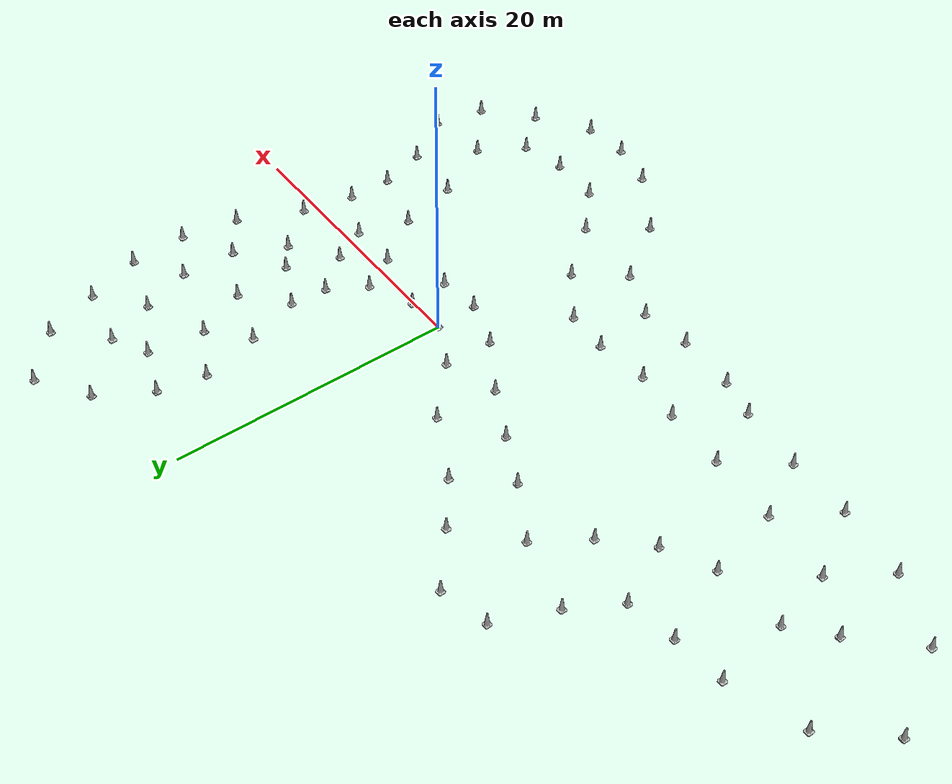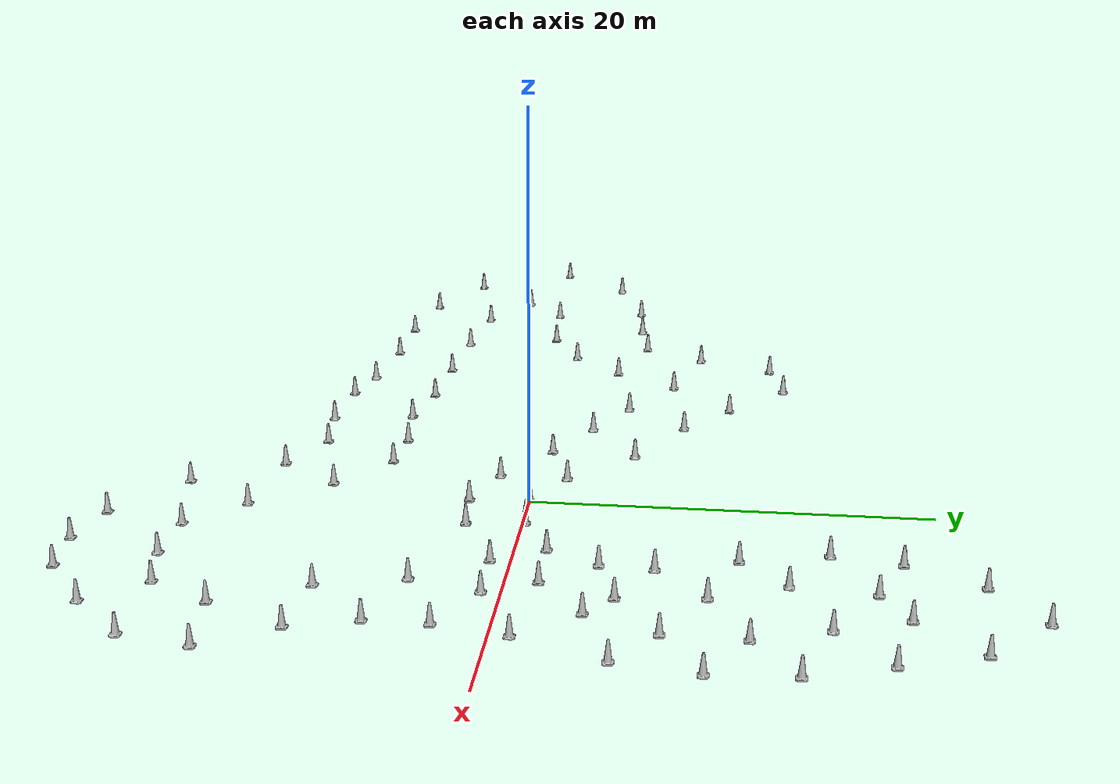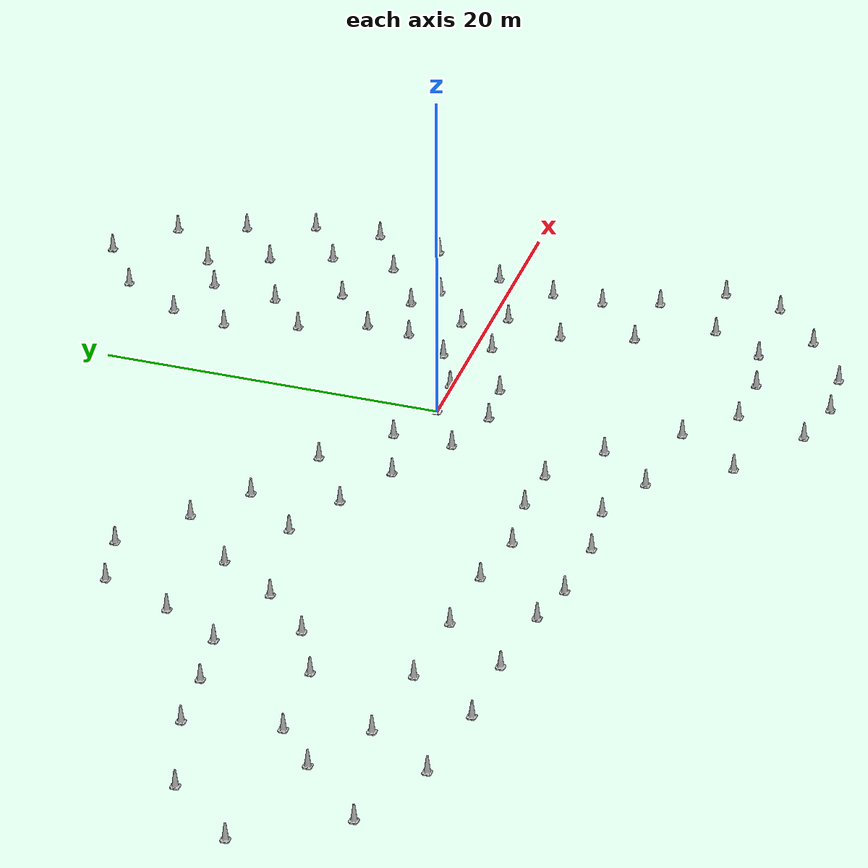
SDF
<?xml version='1.0'?>
<sdf version='1.6'>
  <model name='RaceTrack1'>
    <link name='link'>
      <self_collide>0</self_collide>
      <inertial>
        <inertia>
          <ixx>1</ixx>
          <ixy>0</ixy>
          <ixz>0</ixz>
          <iyy>1</iyy>
          <iyz>0</iyz>
          <izz>1</izz>
        </inertia>
        <mass>1</mass>
        <pose frame=''>0 0 0 0 -0 0</pose>
      </inertial>
      <enable_wind>0</enable_wind>
      <kinematic>0</kinematic>
      <pose frame=''>0 0 0 0 -0 0</pose>
      <gravity>1</gravity>
      <visual name='visual'>
        <geometry>
          <mesh>
            <scale>10 10 10</scale>
            <uri>model://construction_cone/meshes/construction_cone.dae</uri>
          </mesh>
        </geometry>
        <pose frame=''>0 0 0 0 -0 0</pose>
        <transparency>0</transparency>
        <cast_shadows>1</cast_shadows>
        <material>
          <shader type='vertex'>
            <normal_map>__default__</normal_map>
          </shader>
        </material>
      </visual>
      <collision name='collision'>
        <laser_retro>0</laser_retro>
        <max_contacts>10</max_contacts>
        <pose frame=''>0 0 0 0 -0 0</pose>
        <geometry>
          <mesh>
            <uri>model://construction_cone/meshes/construction_cone.dae</uri>
            <scale>10 10 10</scale>
          </mesh>
        </geometry>
        <surface>
          <friction>
            <ode>
              <mu>1</mu>
              <mu2>1</mu2>
              <fdir1>0 0 0</fdir1>
              <slip1>0</slip1>
              <slip2>0</slip2>
            </ode>
            <torsional>
              <coefficient>1</coefficient>
              <patch_radius>0</patch_radius>
              <surface_radius>0</surface_radius>
              <use_patch_radius>1</use_patch_radius>
              <ode>
                <slip>0</slip>
              </ode>
            </torsional>
          </friction>
          <bounce>
            <restitution_coefficient>0</restitution_coefficient>
            <threshold>1e+06</threshold>
          </bounce>
          <contact>
            <collide_without_contact>0</collide_without_contact>
            <collide_without_contact_bitmask>1</collide_without_contact_bitmask>
            <collide_bitmask>1</collide_bitmask>
            <ode>
              <soft_cfm>0</soft_cfm>
              <soft_erp>0.2</soft_erp>
              <kp>1e+13</kp>
              <kd>1</kd>
              <max_vel>0.01</max_vel>
              <min_depth>0</min_depth>
            </ode>
            <bullet>
              <split_impulse>1</split_impulse>
              <split_impulse_penetration_threshold>-0.01</split_impulse_penetration_threshold>
              <soft_cfm>0</soft_cfm>
              <soft_erp>0.2</soft_erp>
              <kp>1e+13</kp>
              <kd>1</kd>
            </bullet>
          </contact>
        </surface>
      </collision>
    </link>
    <link name='link_clone'>
      <self_collide>0</self_collide>
      <inertial>
        <inertia>
          <ixx>1</ixx>
          <ixy>0</ixy>
          <ixz>0</ixz>
          <iyy>1</iyy>
          <iyz>0</iyz>
          <izz>1</izz>
        </inertia>
        <mass>1</mass>
        <pose frame=''>0 0 0 0 -0 0</pose>
      </inertial>
      <enable_wind>0</enable_wind>
      <kinematic>0</kinematic>
      <pose frame=''>0.158084 -3.03002 -1e-06 0 1e-06 0</pose>
      <gravity>1</gravity>
      <visual name='visual'>
        <geometry>
          <mesh>
            <scale>10 10 10</scale>
            <uri>model://construction_cone/meshes/construction_cone.dae</uri>
          </mesh>
        </geometry>
        <pose frame=''>0 0 0 0 -0 0</pose>
        <transparency>0</transparency>
        <cast_shadows>1</cast_shadows>
        <material>
          <shader type='vertex'>
            <normal_map>__default__</normal_map>
          </shader>
        </material>
      </visual>
      <collision name='collision'>
        <laser_retro>0</laser_retro>
        <max_contacts>10</max_contacts>
        <pose frame=''>0 0 0 0 -0 0</pose>
        <geometry>
          <mesh>
            <uri>model://construction_cone/meshes/construction_cone.dae</uri>
            <scale>10 10 10</scale>
          </mesh>
        </geometry>
        <surface>
          <friction>
            <ode>
              <mu>1</mu>
              <mu2>1</mu2>
              <fdir1>0 0 0</fdir1>
              <slip1>0</slip1>
              <slip2>0</slip2>
            </ode>
            <torsional>
              <coefficient>1</coefficient>
              <patch_radius>0</patch_radius>
              <surface_radius>0</surface_radius>
              <use_patch_radius>1</use_patch_radius>
              <ode>
                <slip>0</slip>
              </ode>
            </torsional>
          </friction>
          <bounce>
            <restitution_coefficient>0</restitution_coefficient>
            <threshold>1e+06</threshold>
          </bounce>
          <contact>
            <collide_without_contact>0</collide_without_contact>
            <collide_without_contact_bitmask>1</collide_without_contact_bitmask>
            <collide_bitmask>1</collide_bitmask>
            <ode>
              <soft_cfm>0</soft_cfm>
              <soft_erp>0.2</soft_erp>
              <kp>1e+13</kp>
              <kd>1</kd>
              <max_vel>0.01</max_vel>
              <min_depth>0</min_depth>
            </ode>
            <bullet>
              <split_impulse>1</split_impulse>
              <split_impulse_penetration_threshold>-0.01</split_impulse_penetration_threshold>
              <soft_cfm>0</soft_cfm>
              <soft_erp>0.2</soft_erp>
              <kp>1e+13</kp>
              <kd>1</kd>
            </bullet>
          </contact>
        </surface>
      </collision>
    </link>
    <link name='link_clone_0'>
      <self_collide>0</self_collide>
      <inertial>
        <inertia>
          <ixx>1</ixx>
          <ixy>0</ixy>
          <ixz>0</ixz>
          <iyy>1</iyy>
          <iyz>0</iyz>
          <izz>1</izz>
        </inertia>
        <mass>1</mass>
        <pose frame=''>0 0 0 0 -0 0</pose>
      </inertial>
      <enable_wind>0</enable_wind>
      <kinematic>0</kinematic>
      <pose frame=''>2.81644 0.127499 -2e-06 0 1e-06 0</pose>
      <gravity>1</gravity>
      <visual name='visual'>
        <geometry>
          <mesh>
            <scale>10 10 10</scale>
            <uri>model://construction_cone/meshes/construction_cone.dae</uri>
          </mesh>
        </geometry>
        <pose frame=''>0 0 0 0 -0 0</pose>
        <transparency>0</transparency>
        <cast_shadows>1</cast_shadows>
        <material>
          <shader type='vertex'>
            <normal_map>__default__</normal_map>
          </shader>
        </material>
      </visual>
      <collision name='collision'>
        <laser_retro>0</laser_retro>
        <max_contacts>10</max_contacts>
        <pose frame=''>0 0 0 0 -0 0</pose>
        <geometry>
          <mesh>
            <uri>model://construction_cone/meshes/construction_cone.dae</uri>
            <scale>10 10 10</scale>
          </mesh>
        </geometry>
        <surface>
          <friction>
            <ode>
              <mu>1</mu>
              <mu2>1</mu2>
              <fdir1>0 0 0</fdir1>
              <slip1>0</slip1>
              <slip2>0</slip2>
            </ode>
            <torsional>
              <coefficient>1</coefficient>
              <patch_radius>0</patch_radius>
              <surface_radius>0</surface_radius>
              <use_patch_radius>1</use_patch_radius>
              <ode>
                <slip>0</slip>
              </ode>
            </torsional>
          </friction>
          <bounce>
            <restitution_coefficient>0</restitution_coefficient>
            <threshold>1e+06</threshold>
          </bounce>
          <contact>
            <collide_without_contact>0</collide_without_contact>
            <collide_without_contact_bitmask>1</collide_without_contact_bitmask>
            <collide_bitmask>1</collide_bitmask>
            <ode>
              <soft_cfm>0</soft_cfm>
              <soft_erp>0.2</soft_erp>
              <kp>1e+13</kp>
              <kd>1</kd>
              <max_vel>0.01</max_vel>
              <min_depth>0</min_depth>
            </ode>
            <bullet>
              <split_impulse>1</split_impulse>
              <split_impulse_penetration_threshold>-0.01</split_impulse_penetration_threshold>
              <soft_cfm>0</soft_cfm>
              <soft_erp>0.2</soft_erp>
              <kp>1e+13</kp>
              <kd>1</kd>
            </bullet>
          </contact>
        </surface>
      </collision>
    </link>
    <link name='link_clone_1'>
      <self_collide>0</self_collide>
      <inertial>
        <inertia>
          <ixx>1</ixx>
          <ixy>0</ixy>
          <ixz>0</ixz>
          <iyy>1</iyy>
          <iyz>0</iyz>
          <izz>1</izz>
        </inertia>
        <mass>1</mass>
        <pose frame=''>0 0 0 0 -0 0</pose>
      </inertial>
      <enable_wind>0</enable_wind>
      <kinematic>0</kinematic>
      <pose frame=''>3.1463 -2.74637 -2e-06 0 1e-06 0</pose>
      <gravity>1</gravity>
      <visual name='visual'>
        <geometry>
          <mesh>
            <scale>10 10 10</scale>
            <uri>model://construction_cone/meshes/construction_cone.dae</uri>
          </mesh>
        </geometry>
        <pose frame=''>0 0 0 0 -0 0</pose>
        <transparency>0</transparency>
        <cast_shadows>1</cast_shadows>
        <material>
          <shader type='vertex'>
            <normal_map>__default__</normal_map>
          </shader>
        </material>
      </visual>
      <collision name='collision'>
        <laser_retro>0</laser_retro>
        <max_contacts>10</max_contacts>
        <pose frame=''>0 0 0 0 -0 0</pose>
        <geometry>
          <mesh>
            <uri>model://construction_cone/meshes/construction_cone.dae</uri>
            <scale>10 10 10</scale>
          </mesh>
        </geometry>
        <surface>
          <friction>
            <ode>
              <mu>1</mu>
              <mu2>1</mu2>
              <fdir1>0 0 0</fdir1>
              <slip1>0</slip1>
              <slip2>0</slip2>
            </ode>
            <torsional>
              <coefficient>1</coefficient>
              <patch_radius>0</patch_radius>
              <surface_radius>0</surface_radius>
              <use_patch_radius>1</use_patch_radius>
              <ode>
                <slip>0</slip>
              </ode>
            </torsional>
          </friction>
          <bounce>
            <restitution_coefficient>0</restitution_coefficient>
            <threshold>1e+06</threshold>
          </bounce>
          <contact>
            <collide_without_contact>0</collide_without_contact>
            <collide_without_contact_bitmask>1</collide_without_contact_bitmask>
            <collide_bitmask>1</collide_bitmask>
            <ode>
              <soft_cfm>0</soft_cfm>
              <soft_erp>0.2</soft_erp>
              <kp>1e+13</kp>
              <kd>1</kd>
              <max_vel>0.01</max_vel>
              <min_depth>0</min_depth>
            </ode>
            <bullet>
              <split_impulse>1</split_impulse>
              <split_impulse_penetration_threshold>-0.01</split_impulse_penetration_threshold>
              <soft_cfm>0</soft_cfm>
              <soft_erp>0.2</soft_erp>
              <kp>1e+13</kp>
              <kd>1</kd>
            </bullet>
          </contact>
        </surface>
      </collision>
    </link>
    <link name='link_clone_10'>
      <self_collide>0</self_collide>
      <inertial>
        <inertia>
          <ixx>1</ixx>
          <ixy>0</ixy>
          <ixz>0</ixz>
          <iyy>1</iyy>
          <iyz>0</iyz>
          <izz>1</izz>
        </inertia>
        <mass>1</mass>
        <pose frame=''>0 0 0 0 -0 0</pose>
      </inertial>
      <enable_wind>0</enable_wind>
      <kinematic>0</kinematic>
      <pose frame=''>8.70336 12.8305 -3e-06 0 1e-06 0</pose>
      <gravity>1</gravity>
      <visual name='visual'>
        <geometry>
          <mesh>
            <scale>10 10 10</scale>
            <uri>model://construction_cone/meshes/construction_cone.dae</uri>
          </mesh>
        </geometry>
        <pose frame=''>0 0 0 0 -0 0</pose>
        <transparency>0</transparency>
        <cast_shadows>1</cast_shadows>
        <material>
          <shader type='vertex'>
            <normal_map>__default__</normal_map>
          </shader>
        </material>
      </visual>
      <collision name='collision'>
        <laser_retro>0</laser_retro>
        <max_contacts>10</max_contacts>
        <pose frame=''>0 0 0 0 -0 0</pose>
        <geometry>
          <mesh>
            <uri>model://construction_cone/meshes/construction_cone.dae</uri>
            <scale>10 10 10</scale>
          </mesh>
        </geometry>
        <surface>
          <friction>
            <ode>
              <mu>1</mu>
              <mu2>1</mu2>
              <fdir1>0 0 0</fdir1>
              <slip1>0</slip1>
              <slip2>0</slip2>
            </ode>
            <torsional>
              <coefficient>1</coefficient>
              <patch_radius>0</patch_radius>
              <surface_radius>0</surface_radius>
              <use_patch_radius>1</use_patch_radius>
              <ode>
                <slip>0</slip>
              </ode>
            </torsional>
          </friction>
          <bounce>
            <restitution_coefficient>0</restitution_coefficient>
            <threshold>1e+06</threshold>
          </bounce>
          <contact>
            <collide_without_contact>0</collide_without_contact>
            <collide_without_contact_bitmask>1</collide_without_contact_bitmask>
            <collide_bitmask>1</collide_bitmask>
            <ode>
              <soft_cfm>0</soft_cfm>
              <soft_erp>0.2</soft_erp>
              <kp>1e+13</kp>
              <kd>1</kd>
              <max_vel>0.01</max_vel>
              <min_depth>0</min_depth>
            </ode>
            <bullet>
              <split_impulse>1</split_impulse>
              <split_impulse_penetration_threshold>-0.01</split_impulse_penetration_threshold>
              <soft_cfm>0</soft_cfm>
              <soft_erp>0.2</soft_erp>
              <kp>1e+13</kp>
              <kd>1</kd>
            </bullet>
          </contact>
        </surface>
      </collision>
    </link>
    <link name='link_clone_11'>
      <self_collide>0</self_collide>
      <inertial>
        <inertia>
          <ixx>1</ixx>
          <ixy>0</ixy>
          <ixz>0</ixz>
          <iyy>1</iyy>
          <iyz>0</iyz>
          <izz>1</izz>
        </inertia>
        <mass>1</mass>
        <pose frame=''>0 0 0 0 -0 0</pose>
      </inertial>
      <enable_wind>0</enable_wind>
      <kinematic>0</kinematic>
      <pose frame=''>5.13675 14.7486 -0 0 1e-06 0</pose>
      <gravity>1</gravity>
      <visual name='visual'>
        <geometry>
          <mesh>
            <scale>10 10 10</scale>
            <uri>model://construction_cone/meshes/construction_cone.dae</uri>
          </mesh>
        </geometry>
        <pose frame=''>0 0 0 0 -0 0</pose>
        <transparency>0</transparency>
        <cast_shadows>1</cast_shadows>
        <material>
          <shader type='vertex'>
            <normal_map>__default__</normal_map>
          </shader>
        </material>
      </visual>
      <collision name='collision'>
        <laser_retro>0</laser_retro>
        <max_contacts>10</max_contacts>
        <pose frame=''>0 0 0 0 -0 0</pose>
        <geometry>
          <mesh>
            <uri>model://construction_cone/meshes/construction_cone.dae</uri>
            <scale>10 10 10</scale>
          </mesh>
        </geometry>
        <surface>
          <friction>
            <ode>
              <mu>1</mu>
              <mu2>1</mu2>
              <fdir1>0 0 0</fdir1>
              <slip1>0</slip1>
              <slip2>0</slip2>
            </ode>
            <torsional>
              <coefficient>1</coefficient>
              <patch_radius>0</patch_radius>
              <surface_radius>0</surface_radius>
              <use_patch_radius>1</use_patch_radius>
              <ode>
                <slip>0</slip>
              </ode>
            </torsional>
          </friction>
          <bounce>
            <restitution_coefficient>0</restitution_coefficient>
            <threshold>1e+06</threshold>
          </bounce>
          <contact>
            <collide_without_contact>0</collide_without_contact>
            <collide_without_contact_bitmask>1</collide_without_contact_bitmask>
            <collide_bitmask>1</collide_bitmask>
            <ode>
              <soft_cfm>0</soft_cfm>
              <soft_erp>0.2</soft_erp>
              <kp>1e+13</kp>
              <kd>1</kd>
              <max_vel>0.01</max_vel>
              <min_depth>0</min_depth>
            </ode>
            <bullet>
              <split_impulse>1</split_impulse>
              <split_impulse_penetration_threshold>-0.01</split_impulse_penetration_threshold>
              <soft_cfm>0</soft_cfm>
              <soft_erp>0.2</soft_erp>
              <kp>1e+13</kp>
              <kd>1</kd>
            </bullet>
          </contact>
        </surface>
      </collision>
    </link>
    <link name='link_clone_12'>
      <self_collide>0</self_collide>
      <inertial>
        <inertia>
          <ixx>1</ixx>
          <ixy>0</ixy>
          <ixz>0</ixz>
          <iyy>1</iyy>
          <iyz>0</iyz>
          <izz>1</izz>
        </inertia>
        <mass>1</mass>
        <pose frame=''>0 0 0 0 -0 0</pose>
      </inertial>
      <enable_wind>0</enable_wind>
      <kinematic>0</kinematic>
      <pose frame=''>9.17297 16.8137 -2e-06 0 1e-06 0</pose>
      <gravity>1</gravity>
      <visual name='visual'>
        <geometry>
          <mesh>
            <scale>10 10 10</scale>
            <uri>model://construction_cone/meshes/construction_cone.dae</uri>
          </mesh>
        </geometry>
        <pose frame=''>0 0 0 0 -0 0</pose>
        <transparency>0</transparency>
        <cast_shadows>1</cast_shadows>
        <material>
          <shader type='vertex'>
            <normal_map>__default__</normal_map>
          </shader>
        </material>
      </visual>
      <collision name='collision'>
        <laser_retro>0</laser_retro>
        <max_contacts>10</max_contacts>
        <pose frame=''>0 0 0 0 -0 0</pose>
        <geometry>
          <mesh>
            <uri>model://construction_cone/meshes/construction_cone.dae</uri>
            <scale>10 10 10</scale>
          </mesh>
        </geometry>
        <surface>
          <friction>
            <ode>
              <mu>1</mu>
              <mu2>1</mu2>
              <fdir1>0 0 0</fdir1>
              <slip1>0</slip1>
              <slip2>0</slip2>
            </ode>
            <torsional>
              <coefficient>1</coefficient>
              <patch_radius>0</patch_radius>
              <surface_radius>0</surface_radius>
              <use_patch_radius>1</use_patch_radius>
              <ode>
                <slip>0</slip>
              </ode>
            </torsional>
          </friction>
          <bounce>
            <restitution_coefficient>0</restitution_coefficient>
            <threshold>1e+06</threshold>
          </bounce>
          <contact>
            <collide_without_contact>0</collide_without_contact>
            <collide_without_contact_bitmask>1</collide_without_contact_bitmask>
            <collide_bitmask>1</collide_bitmask>
            <ode>
              <soft_cfm>0</soft_cfm>
              <soft_erp>0.2</soft_erp>
              <kp>1e+13</kp>
              <kd>1</kd>
              <max_vel>0.01</max_vel>
              <min_depth>0</min_depth>
            </ode>
            <bullet>
              <split_impulse>1</split_impulse>
              <split_impulse_penetration_threshold>-0.01</split_impulse_penetration_threshold>
              <soft_cfm>0</soft_cfm>
              <soft_erp>0.2</soft_erp>
              <kp>1e+13</kp>
              <kd>1</kd>
            </bullet>
          </contact>
        </surface>
      </collision>
    </link>
    <link name='link_clone_13'>
      <self_collide>0</self_collide>
      <inertial>
        <inertia>
          <ixx>1</ixx>
          <ixy>0</ixy>
          <ixz>0</ixz>
          <iyy>1</iyy>
          <iyz>0</iyz>
          <izz>1</izz>
        </inertia>
        <mass>1</mass>
        <pose frame=''>0 0 0 0 -0 0</pose>
      </inertial>
      <enable_wind>0</enable_wind>
      <kinematic>0</kinematic>
      <pose frame=''>5.77634 18.1039 0 0 1e-06 0</pose>
      <gravity>1</gravity>
      <visual name='visual'>
        <geometry>
          <mesh>
            <scale>10 10 10</scale>
            <uri>model://construction_cone/meshes/construction_cone.dae</uri>
          </mesh>
        </geometry>
        <pose frame=''>0 0 0 0 -0 0</pose>
        <transparency>0</transparency>
        <cast_shadows>1</cast_shadows>
        <material>
          <shader type='vertex'>
            <normal_map>__default__</normal_map>
          </shader>
        </material>
      </visual>
      <collision name='collision'>
        <laser_retro>0</laser_retro>
        <max_contacts>10</max_contacts>
        <pose frame=''>0 0 0 0 -0 0</pose>
        <geometry>
          <mesh>
            <uri>model://construction_cone/meshes/construction_cone.dae</uri>
            <scale>10 10 10</scale>
          </mesh>
        </geometry>
        <surface>
          <friction>
            <ode>
              <mu>1</mu>
              <mu2>1</mu2>
              <fdir1>0 0 0</fdir1>
              <slip1>0</slip1>
              <slip2>0</slip2>
            </ode>
            <torsional>
              <coefficient>1</coefficient>
              <patch_radius>0</patch_radius>
              <surface_radius>0</surface_radius>
              <use_patch_radius>1</use_patch_radius>
              <ode>
                <slip>0</slip>
              </ode>
            </torsional>
          </friction>
          <bounce>
            <restitution_coefficient>0</restitution_coefficient>
            <threshold>1e+06</threshold>
          </bounce>
          <contact>
            <collide_without_contact>0</collide_without_contact>
            <collide_without_contact_bitmask>1</collide_without_contact_bitmask>
            <collide_bitmask>1</collide_bitmask>
            <ode>
              <soft_cfm>0</soft_cfm>
              <soft_erp>0.2</soft_erp>
              <kp>1e+13</kp>
              <kd>1</kd>
              <max_vel>0.01</max_vel>
              <min_depth>0</min_depth>
            </ode>
            <bullet>
              <split_impulse>1</split_impulse>
              <split_impulse_penetration_threshold>-0.01</split_impulse_penetration_threshold>
              <soft_cfm>0</soft_cfm>
              <soft_erp>0.2</soft_erp>
              <kp>1e+13</kp>
              <kd>1</kd>
            </bullet>
          </contact>
        </surface>
      </collision>
    </link>
    <link name='link_clone_14'>
      <self_collide>0</self_collide>
      <inertial>
        <inertia>
          <ixx>1</ixx>
          <ixy>0</ixy>
          <ixz>0</ixz>
          <iyy>1</iyy>
          <iyz>0</iyz>
          <izz>1</izz>
        </inertia>
        <mass>1</mass>
        <pose frame=''>0 0 0 0 -0 0</pose>
      </inertial>
      <enable_wind>0</enable_wind>
      <kinematic>0</kinematic>
      <pose frame=''>7.8815 21.7006 -1e-06 0 1e-06 0</pose>
      <gravity>1</gravity>
      <visual name='visual'>
        <geometry>
          <mesh>
            <scale>10 10 10</scale>
            <uri>model://construction_cone/meshes/construction_cone.dae</uri>
          </mesh>
        </geometry>
        <pose frame=''>0 0 0 0 -0 0</pose>
        <transparency>0</transparency>
        <cast_shadows>1</cast_shadows>
        <material>
          <shader type='vertex'>
            <normal_map>__default__</normal_map>
          </shader>
        </material>
      </visual>
      <collision name='collision'>
        <laser_retro>0</laser_retro>
        <max_contacts>10</max_contacts>
        <pose frame=''>0 0 0 0 -0 0</pose>
        <geometry>
          <mesh>
            <uri>model://construction_cone/meshes/construction_cone.dae</uri>
            <scale>10 10 10</scale>
          </mesh>
        </geometry>
        <surface>
          <friction>
            <ode>
              <mu>1</mu>
              <mu2>1</mu2>
              <fdir1>0 0 0</fdir1>
              <slip1>0</slip1>
              <slip2>0</slip2>
            </ode>
            <torsional>
              <coefficient>1</coefficient>
              <patch_radius>0</patch_radius>
              <surface_radius>0</surface_radius>
              <use_patch_radius>1</use_patch_radius>
              <ode>
                <slip>0</slip>
              </ode>
            </torsional>
          </friction>
          <bounce>
            <restitution_coefficient>0</restitution_coefficient>
            <threshold>1e+06</threshold>
          </bounce>
          <contact>
            <collide_without_contact>0</collide_without_contact>
            <collide_without_contact_bitmask>1</collide_without_contact_bitmask>
            <collide_bitmask>1</collide_bitmask>
            <ode>
              <soft_cfm>0</soft_cfm>
              <soft_erp>0.2</soft_erp>
              <kp>1e+13</kp>
              <kd>1</kd>
              <max_vel>0.01</max_vel>
              <min_depth>0</min_depth>
            </ode>
            <bullet>
              <split_impulse>1</split_impulse>
              <split_impulse_penetration_threshold>-0.01</split_impulse_penetration_threshold>
              <soft_cfm>0</soft_cfm>
              <soft_erp>0.2</soft_erp>
              <kp>1e+13</kp>
              <kd>1</kd>
            </bullet>
          </contact>
        </surface>
      </collision>
    </link>
    <link name='link_clone_15'>
      <self_collide>0</self_collide>
      <inertial>
        <inertia>
          <ixx>1</ixx>
          <ixy>0</ixy>
          <ixz>0</ixz>
          <iyy>1</iyy>
          <iyz>0</iyz>
          <izz>1</izz>
        </inertia>
        <mass>1</mass>
        <pose frame=''>0 0 0 0 -0 0</pose>
      </inertial>
      <enable_wind>0</enable_wind>
      <kinematic>0</kinematic>
      <pose frame=''>11.2753 24.038 -2e-06 0 1e-06 0</pose>
      <gravity>1</gravity>
      <visual name='visual'>
        <geometry>
          <mesh>
            <scale>10 10 10</scale>
            <uri>model://construction_cone/meshes/construction_cone.dae</uri>
          </mesh>
        </geometry>
        <pose frame=''>0 0 0 0 -0 0</pose>
        <transparency>0</transparency>
        <cast_shadows>1</cast_shadows>
        <material>
          <shader type='vertex'>
            <normal_map>__default__</normal_map>
          </shader>
        </material>
      </visual>
      <collision name='collision'>
        <laser_retro>0</laser_retro>
        <max_contacts>10</max_contacts>
        <pose frame=''>0 0 0 0 -0 0</pose>
        <geometry>
          <mesh>
            <uri>model://construction_cone/meshes/construction_cone.dae</uri>
            <scale>10 10 10</scale>
          </mesh>
        </geometry>
        <surface>
          <friction>
            <ode>
              <mu>1</mu>
              <mu2>1</mu2>
              <fdir1>0 0 0</fdir1>
              <slip1>0</slip1>
              <slip2>0</slip2>
            </ode>
            <torsional>
              <coefficient>1</coefficient>
              <patch_radius>0</patch_radius>
              <surface_radius>0</surface_radius>
              <use_patch_radius>1</use_patch_radius>
              <ode>
                <slip>0</slip>
              </ode>
            </torsional>
          </friction>
          <bounce>
            <restitution_coefficient>0</restitution_coefficient>
            <threshold>1e+06</threshold>
          </bounce>
          <contact>
            <collide_without_contact>0</collide_without_contact>
            <collide_without_contact_bitmask>1</collide_without_contact_bitmask>
            <collide_bitmask>1</collide_bitmask>
            <ode>
              <soft_cfm>0</soft_cfm>
              <soft_erp>0.2</soft_erp>
              <kp>1e+13</kp>
              <kd>1</kd>
              <max_vel>0.01</max_vel>
              <min_depth>0</min_depth>
            </ode>
            <bullet>
              <split_impulse>1</split_impulse>
              <split_impulse_penetration_threshold>-0.01</split_impulse_penetration_threshold>
              <soft_cfm>0</soft_cfm>
              <soft_erp>0.2</soft_erp>
              <kp>1e+13</kp>
              <kd>1</kd>
            </bullet>
          </contact>
        </surface>
      </collision>
    </link>
    <link name='link_clone_16'>
      <self_collide>0</self_collide>
      <inertial>
        <inertia>
          <ixx>1</ixx>
          <ixy>0</ixy>
          <ixz>0</ixz>
          <iyy>1</iyy>
          <iyz>0</iyz>
          <izz>1</izz>
        </inertia>
        <mass>1</mass>
        <pose frame=''>0 0 0 0 -0 0</pose>
      </inertial>
      <enable_wind>0</enable_wind>
      <kinematic>0</kinematic>
      <pose frame=''>11.6129 18.1211 -3e-06 0 1e-06 0</pose>
      <gravity>1</gravity>
      <visual name='visual'>
        <geometry>
          <mesh>
            <scale>10 10 10</scale>
            <uri>model://construction_cone/meshes/construction_cone.dae</uri>
          </mesh>
        </geometry>
        <pose frame=''>0 0 0 0 -0 0</pose>
        <transparency>0</transparency>
        <cast_shadows>1</cast_shadows>
        <material>
          <shader type='vertex'>
            <normal_map>__default__</normal_map>
          </shader>
        </material>
      </visual>
      <collision name='collision'>
        <laser_retro>0</laser_retro>
        <max_contacts>10</max_contacts>
        <pose frame=''>0 0 0 0 -0 0</pose>
        <geometry>
          <mesh>
            <uri>model://construction_cone/meshes/construction_cone.dae</uri>
            <scale>10 10 10</scale>
          </mesh>
        </geometry>
        <surface>
          <friction>
            <ode>
              <mu>1</mu>
              <mu2>1</mu2>
              <fdir1>0 0 0</fdir1>
              <slip1>0</slip1>
              <slip2>0</slip2>
            </ode>
            <torsional>
              <coefficient>1</coefficient>
              <patch_radius>0</patch_radius>
              <surface_radius>0</surface_radius>
              <use_patch_radius>1</use_patch_radius>
              <ode>
                <slip>0</slip>
              </ode>
            </torsional>
          </friction>
          <bounce>
            <restitution_coefficient>0</restitution_coefficient>
            <threshold>1e+06</threshold>
          </bounce>
          <contact>
            <collide_without_contact>0</collide_without_contact>
            <collide_without_contact_bitmask>1</collide_without_contact_bitmask>
            <collide_bitmask>1</collide_bitmask>
            <ode>
              <soft_cfm>0</soft_cfm>
              <soft_erp>0.2</soft_erp>
              <kp>1e+13</kp>
              <kd>1</kd>
              <max_vel>0.01</max_vel>
              <min_depth>0</min_depth>
            </ode>
            <bullet>
              <split_impulse>1</split_impulse>
              <split_impulse_penetration_threshold>-0.01</split_impulse_penetration_threshold>
              <soft_cfm>0</soft_cfm>
              <soft_erp>0.2</soft_erp>
              <kp>1e+13</kp>
              <kd>1</kd>
            </bullet>
          </contact>
        </surface>
      </collision>
    </link>
    <link name='link_clone_17'>
      <self_collide>0</self_collide>
      <inertial>
        <inertia>
          <ixx>1</ixx>
          <ixy>0</ixy>
          <ixz>0</ixz>
          <iyy>1</iyy>
          <iyz>0</iyz>
          <izz>1</izz>
        </inertia>
        <mass>1</mass>
        <pose frame=''>0 0 0 0 -0 0</pose>
      </inertial>
      <enable_wind>0</enable_wind>
      <kinematic>0</kinematic>
      <pose frame=''>14.5734 21.098 -4e-06 0 1e-06 0</pose>
      <gravity>1</gravity>
      <visual name='visual'>
        <geometry>
          <mesh>
            <scale>10 10 10</scale>
            <uri>model://construction_cone/meshes/construction_cone.dae</uri>
          </mesh>
        </geometry>
        <pose frame=''>0 0 0 0 -0 0</pose>
        <transparency>0</transparency>
        <cast_shadows>1</cast_shadows>
        <material>
          <shader type='vertex'>
            <normal_map>__default__</normal_map>
          </shader>
        </material>
      </visual>
      <collision name='collision'>
        <laser_retro>0</laser_retro>
        <max_contacts>10</max_contacts>
        <pose frame=''>0 0 0 0 -0 0</pose>
        <geometry>
          <mesh>
            <uri>model://construction_cone/meshes/construction_cone.dae</uri>
            <scale>10 10 10</scale>
          </mesh>
        </geometry>
        <surface>
          <friction>
            <ode>
              <mu>1</mu>
              <mu2>1</mu2>
              <fdir1>0 0 0</fdir1>
              <slip1>0</slip1>
              <slip2>0</slip2>
            </ode>
            <torsional>
              <coefficient>1</coefficient>
              <patch_radius>0</patch_radius>
              <surface_radius>0</surface_radius>
              <use_patch_radius>1</use_patch_radius>
              <ode>
                <slip>0</slip>
              </ode>
            </torsional>
          </friction>
          <bounce>
            <restitution_coefficient>0</restitution_coefficient>
            <threshold>1e+06</threshold>
          </bounce>
          <contact>
            <collide_without_contact>0</collide_without_contact>
            <collide_without_contact_bitmask>1</collide_without_contact_bitmask>
            <collide_bitmask>1</collide_bitmask>
            <ode>
              <soft_cfm>0</soft_cfm>
              <soft_erp>0.2</soft_erp>
              <kp>1e+13</kp>
              <kd>1</kd>
              <max_vel>0.01</max_vel>
              <min_depth>0</min_depth>
            </ode>
            <bullet>
              <split_impulse>1</split_impulse>
              <split_impulse_penetration_threshold>-0.01</split_impulse_penetration_threshold>
              <soft_cfm>0</soft_cfm>
              <soft_erp>0.2</soft_erp>
              <kp>1e+13</kp>
              <kd>1</kd>
            </bullet>
          </contact>
        </surface>
      </collision>
    </link>
    <link name='link_clone_18'>
      <self_collide>0</self_collide>
      <inertial>
        <inertia>
          <ixx>1</ixx>
          <ixy>0</ixy>
          <ixz>0</ixz>
          <iyy>1</iyy>
          <iyz>0</iyz>
          <izz>1</izz>
        </inertia>
        <mass>1</mass>
        <pose frame=''>0 0 0 0 -0 0</pose>
      </inertial>
      <enable_wind>0</enable_wind>
      <kinematic>0</kinematic>
      <pose frame=''>15.9824 17.1998 -6e-06 0 1e-06 0</pose>
      <gravity>1</gravity>
      <visual name='visual'>
        <geometry>
          <mesh>
            <scale>10 10 10</scale>
            <uri>model://construction_cone/meshes/construction_cone.dae</uri>
          </mesh>
        </geometry>
        <pose frame=''>0 0 0 0 -0 0</pose>
        <transparency>0</transparency>
        <cast_shadows>1</cast_shadows>
        <material>
          <shader type='vertex'>
            <normal_map>__default__</normal_map>
          </shader>
        </material>
      </visual>
      <collision name='collision'>
        <laser_retro>0</laser_retro>
        <max_contacts>10</max_contacts>
        <pose frame=''>0 0 0 0 -0 0</pose>
        <geometry>
          <mesh>
            <uri>model://construction_cone/meshes/construction_cone.dae</uri>
            <scale>10 10 10</scale>
          </mesh>
        </geometry>
        <surface>
          <friction>
            <ode>
              <mu>1</mu>
              <mu2>1</mu2>
              <fdir1>0 0 0</fdir1>
              <slip1>0</slip1>
              <slip2>0</slip2>
            </ode>
            <torsional>
              <coefficient>1</coefficient>
              <patch_radius>0</patch_radius>
              <surface_radius>0</surface_radius>
              <use_patch_radius>1</use_patch_radius>
              <ode>
                <slip>0</slip>
              </ode>
            </torsional>
          </friction>
          <bounce>
            <restitution_coefficient>0</restitution_coefficient>
            <threshold>1e+06</threshold>
          </bounce>
          <contact>
            <collide_without_contact>0</collide_without_contact>
            <collide_without_contact_bitmask>1</collide_without_contact_bitmask>
            <collide_bitmask>1</collide_bitmask>
            <ode>
              <soft_cfm>0</soft_cfm>
              <soft_erp>0.2</soft_erp>
              <kp>1e+13</kp>
              <kd>1</kd>
              <max_vel>0.01</max_vel>
              <min_depth>0</min_depth>
            </ode>
            <bullet>
              <split_impulse>1</split_impulse>
              <split_impulse_penetration_threshold>-0.01</split_impulse_penetration_threshold>
              <soft_cfm>0</soft_cfm>
              <soft_erp>0.2</soft_erp>
              <kp>1e+13</kp>
              <kd>1</kd>
            </bullet>
          </contact>
        </surface>
      </collision>
    </link>
    <link name='link_clone_19'>
      <self_collide>0</self_collide>
      <inertial>
        <inertia>
          <ixx>1</ixx>
          <ixy>0</ixy>
          <ixz>0</ixz>
          <iyy>1</iyy>
          <iyz>0</iyz>
          <izz>1</izz>
        </inertia>
        <mass>1</mass>
        <pose frame=''>0 0 0 0 -0 0</pose>
      </inertial>
      <enable_wind>0</enable_wind>
      <kinematic>0</kinematic>
      <pose frame=''>12.9594 14.6631 -5e-06 0 1e-06 0</pose>
      <gravity>1</gravity>
      <visual name='visual'>
        <geometry>
          <mesh>
            <scale>10 10 10</scale>
            <uri>model://construction_cone/meshes/construction_cone.dae</uri>
          </mesh>
        </geometry>
        <pose frame=''>0 0 0 0 -0 0</pose>
        <transparency>0</transparency>
        <cast_shadows>1</cast_shadows>
        <material>
          <shader type='vertex'>
            <normal_map>__default__</normal_map>
          </shader>
        </material>
      </visual>
      <collision name='collision'>
        <laser_retro>0</laser_retro>
        <max_contacts>10</max_contacts>
        <pose frame=''>0 0 0 0 -0 0</pose>
        <geometry>
          <mesh>
            <uri>model://construction_cone/meshes/construction_cone.dae</uri>
            <scale>10 10 10</scale>
          </mesh>
        </geometry>
        <surface>
          <friction>
            <ode>
              <mu>1</mu>
              <mu2>1</mu2>
              <fdir1>0 0 0</fdir1>
              <slip1>0</slip1>
              <slip2>0</slip2>
            </ode>
            <torsional>
              <coefficient>1</coefficient>
              <patch_radius>0</patch_radius>
              <surface_radius>0</surface_radius>
              <use_patch_radius>1</use_patch_radius>
              <ode>
                <slip>0</slip>
              </ode>
            </torsional>
          </friction>
          <bounce>
            <restitution_coefficient>0</restitution_coefficient>
            <threshold>1e+06</threshold>
          </bounce>
          <contact>
            <collide_without_contact>0</collide_without_contact>
            <collide_without_contact_bitmask>1</collide_without_contact_bitmask>
            <collide_bitmask>1</collide_bitmask>
            <ode>
              <soft_cfm>0</soft_cfm>
              <soft_erp>0.2</soft_erp>
              <kp>1e+13</kp>
              <kd>1</kd>
              <max_vel>0.01</max_vel>
              <min_depth>0</min_depth>
            </ode>
            <bullet>
              <split_impulse>1</split_impulse>
              <split_impulse_penetration_threshold>-0.01</split_impulse_penetration_threshold>
              <soft_cfm>0</soft_cfm>
              <soft_erp>0.2</soft_erp>
              <kp>1e+13</kp>
              <kd>1</kd>
            </bullet>
          </contact>
        </surface>
      </collision>
    </link>
    <link name='link_clone_2'>
      <self_collide>0</self_collide>
      <inertial>
        <inertia>
          <ixx>1</ixx>
          <ixy>0</ixy>
          <ixz>0</ixz>
          <iyy>1</iyy>
          <iyz>0</iyz>
          <izz>1</izz>
        </inertia>
        <mass>1</mass>
        <pose frame=''>0 0 0 0 -0 0</pose>
      </inertial>
      <enable_wind>0</enable_wind>
      <kinematic>0</kinematic>
      <pose frame=''>5.87817 1.52613 -3e-06 0 1e-06 0</pose>
      <gravity>1</gravity>
      <visual name='visual'>
        <geometry>
          <mesh>
            <scale>10 10 10</scale>
            <uri>model://construction_cone/meshes/construction_cone.dae</uri>
          </mesh>
        </geometry>
        <pose frame=''>0 0 0 0 -0 0</pose>
        <transparency>0</transparency>
        <cast_shadows>1</cast_shadows>
        <material>
          <shader type='vertex'>
            <normal_map>__default__</normal_map>
          </shader>
        </material>
      </visual>
      <collision name='collision'>
        <laser_retro>0</laser_retro>
        <max_contacts>10</max_contacts>
        <pose frame=''>0 0 0 0 -0 0</pose>
        <geometry>
          <mesh>
            <uri>model://construction_cone/meshes/construction_cone.dae</uri>
            <scale>10 10 10</scale>
          </mesh>
        </geometry>
        <surface>
          <friction>
            <ode>
              <mu>1</mu>
              <mu2>1</mu2>
              <fdir1>0 0 0</fdir1>
              <slip1>0</slip1>
              <slip2>0</slip2>
            </ode>
            <torsional>
              <coefficient>1</coefficient>
              <patch_radius>0</patch_radius>
              <surface_radius>0</surface_radius>
              <use_patch_radius>1</use_patch_radius>
              <ode>
                <slip>0</slip>
              </ode>
            </torsional>
          </friction>
          <bounce>
            <restitution_coefficient>0</restitution_coefficient>
            <threshold>1e+06</threshold>
          </bounce>
          <contact>
            <collide_without_contact>0</collide_without_contact>
            <collide_without_contact_bitmask>1</collide_without_contact_bitmask>
            <collide_bitmask>1</collide_bitmask>
            <ode>
              <soft_cfm>0</soft_cfm>
              <soft_erp>0.2</soft_erp>
              <kp>1e+13</kp>
              <kd>1</kd>
              <max_vel>0.01</max_vel>
              <min_depth>0</min_depth>
            </ode>
            <bullet>
              <split_impulse>1</split_impulse>
              <split_impulse_penetration_threshold>-0.01</split_impulse_penetration_threshold>
              <soft_cfm>0</soft_cfm>
              <soft_erp>0.2</soft_erp>
              <kp>1e+13</kp>
              <kd>1</kd>
            </bullet>
          </contact>
        </surface>
      </collision>
    </link>
    <link name='link_clone_20'>
      <self_collide>0</self_collide>
      <inertial>
        <inertia>
          <ixx>1</ixx>
          <ixy>0</ixy>
          <ixz>0</ixz>
          <iyy>1</iyy>
          <iyz>0</iyz>
          <izz>1</izz>
        </inertia>
        <mass>1</mass>
        <pose frame=''>0 0 0 0 -0 0</pose>
      </inertial>
      <enable_wind>0</enable_wind>
      <kinematic>0</kinematic>
      <pose frame=''>14.2254 11.1301 -6e-06 0 1e-06 0</pose>
      <gravity>1</gravity>
      <visual name='visual'>
        <geometry>
          <mesh>
            <scale>10 10 10</scale>
            <uri>model://construction_cone/meshes/construction_cone.dae</uri>
          </mesh>
        </geometry>
        <pose frame=''>0 0 0 0 -0 0</pose>
        <transparency>0</transparency>
        <cast_shadows>1</cast_shadows>
        <material>
          <shader type='vertex'>
            <normal_map>__default__</normal_map>
          </shader>
        </material>
      </visual>
      <collision name='collision'>
        <laser_retro>0</laser_retro>
        <max_contacts>10</max_contacts>
        <pose frame=''>0 0 0 0 -0 0</pose>
        <geometry>
          <mesh>
            <uri>model://construction_cone/meshes/construction_cone.dae</uri>
            <scale>10 10 10</scale>
          </mesh>
        </geometry>
        <surface>
          <friction>
            <ode>
              <mu>1</mu>
              <mu2>1</mu2>
              <fdir1>0 0 0</fdir1>
              <slip1>0</slip1>
              <slip2>0</slip2>
            </ode>
            <torsional>
              <coefficient>1</coefficient>
              <patch_radius>0</patch_radius>
              <surface_radius>0</surface_radius>
              <use_patch_radius>1</use_patch_radius>
              <ode>
                <slip>0</slip>
              </ode>
            </torsional>
          </friction>
          <bounce>
            <restitution_coefficient>0</restitution_coefficient>
            <threshold>1e+06</threshold>
          </bounce>
          <contact>
            <collide_without_contact>0</collide_without_contact>
            <collide_without_contact_bitmask>1</collide_without_contact_bitmask>
            <collide_bitmask>1</collide_bitmask>
            <ode>
              <soft_cfm>0</soft_cfm>
              <soft_erp>0.2</soft_erp>
              <kp>1e+13</kp>
              <kd>1</kd>
              <max_vel>0.01</max_vel>
              <min_depth>0</min_depth>
            </ode>
            <bullet>
              <split_impulse>1</split_impulse>
              <split_impulse_penetration_threshold>-0.01</split_impulse_penetration_threshold>
              <soft_cfm>0</soft_cfm>
              <soft_erp>0.2</soft_erp>
              <kp>1e+13</kp>
              <kd>1</kd>
            </bullet>
          </contact>
        </surface>
      </collision>
    </link>
    <link name='link_clone_21'>
      <self_collide>0</self_collide>
      <inertial>
        <inertia>
          <ixx>1</ixx>
          <ixy>0</ixy>
          <ixz>0</ixz>
          <iyy>1</iyy>
          <iyz>0</iyz>
          <izz>1</izz>
        </inertia>
        <mass>1</mass>
        <pose frame=''>0 0 0 0 -0 0</pose>
      </inertial>
      <enable_wind>0</enable_wind>
      <kinematic>0</kinematic>
      <pose frame=''>17.3302 13.273 -7e-06 0 1e-06 0</pose>
      <gravity>1</gravity>
      <visual name='visual'>
        <geometry>
          <mesh>
            <scale>10 10 10</scale>
            <uri>model://construction_cone/meshes/construction_cone.dae</uri>
          </mesh>
        </geometry>
        <pose frame=''>0 0 0 0 -0 0</pose>
        <transparency>0</transparency>
        <cast_shadows>1</cast_shadows>
        <material>
          <shader type='vertex'>
            <normal_map>__default__</normal_map>
          </shader>
        </material>
      </visual>
      <collision name='collision'>
        <laser_retro>0</laser_retro>
        <max_contacts>10</max_contacts>
        <pose frame=''>0 0 0 0 -0 0</pose>
        <geometry>
          <mesh>
            <uri>model://construction_cone/meshes/construction_cone.dae</uri>
            <scale>10 10 10</scale>
          </mesh>
        </geometry>
        <surface>
          <friction>
            <ode>
              <mu>1</mu>
              <mu2>1</mu2>
              <fdir1>0 0 0</fdir1>
              <slip1>0</slip1>
              <slip2>0</slip2>
            </ode>
            <torsional>
              <coefficient>1</coefficient>
              <patch_radius>0</patch_radius>
              <surface_radius>0</surface_radius>
              <use_patch_radius>1</use_patch_radius>
              <ode>
                <slip>0</slip>
              </ode>
            </torsional>
          </friction>
          <bounce>
            <restitution_coefficient>0</restitution_coefficient>
            <threshold>1e+06</threshold>
          </bounce>
          <contact>
            <collide_without_contact>0</collide_without_contact>
            <collide_without_contact_bitmask>1</collide_without_contact_bitmask>
            <collide_bitmask>1</collide_bitmask>
            <ode>
              <soft_cfm>0</soft_cfm>
              <soft_erp>0.2</soft_erp>
              <kp>1e+13</kp>
              <kd>1</kd>
              <max_vel>0.01</max_vel>
              <min_depth>0</min_depth>
            </ode>
            <bullet>
              <split_impulse>1</split_impulse>
              <split_impulse_penetration_threshold>-0.01</split_impulse_penetration_threshold>
              <soft_cfm>0</soft_cfm>
              <soft_erp>0.2</soft_erp>
              <kp>1e+13</kp>
              <kd>1</kd>
            </bullet>
          </contact>
        </surface>
      </collision>
    </link>
    <link name='link_clone_22'>
      <self_collide>0</self_collide>
      <inertial>
        <inertia>
          <ixx>1</ixx>
          <ixy>0</ixy>
          <ixz>0</ixz>
          <iyy>1</iyy>
          <iyz>0</iyz>
          <izz>1</izz>
        </inertia>
        <mass>1</mass>
        <pose frame=''>0 0 0 0 -0 0</pose>
      </inertial>
      <enable_wind>0</enable_wind>
      <kinematic>0</kinematic>
      <pose frame=''>14.1306 7.28756 -7e-06 0 1e-06 0</pose>
      <gravity>1</gravity>
      <visual name='visual'>
        <geometry>
          <mesh>
            <scale>10 10 10</scale>
            <uri>model://construction_cone/meshes/construction_cone.dae</uri>
          </mesh>
        </geometry>
        <pose frame=''>0 0 0 0 -0 0</pose>
        <transparency>0</transparency>
        <cast_shadows>1</cast_shadows>
        <material>
          <shader type='vertex'>
            <normal_map>__default__</normal_map>
          </shader>
        </material>
      </visual>
      <collision name='collision'>
        <laser_retro>0</laser_retro>
        <max_contacts>10</max_contacts>
        <pose frame=''>0 0 0 0 -0 0</pose>
        <geometry>
          <mesh>
            <uri>model://construction_cone/meshes/construction_cone.dae</uri>
            <scale>10 10 10</scale>
          </mesh>
        </geometry>
        <surface>
          <friction>
            <ode>
              <mu>1</mu>
              <mu2>1</mu2>
              <fdir1>0 0 0</fdir1>
              <slip1>0</slip1>
              <slip2>0</slip2>
            </ode>
            <torsional>
              <coefficient>1</coefficient>
              <patch_radius>0</patch_radius>
              <surface_radius>0</surface_radius>
              <use_patch_radius>1</use_patch_radius>
              <ode>
                <slip>0</slip>
              </ode>
            </torsional>
          </friction>
          <bounce>
            <restitution_coefficient>0</restitution_coefficient>
            <threshold>1e+06</threshold>
          </bounce>
          <contact>
            <collide_without_contact>0</collide_without_contact>
            <collide_without_contact_bitmask>1</collide_without_contact_bitmask>
            <collide_bitmask>1</collide_bitmask>
            <ode>
              <soft_cfm>0</soft_cfm>
              <soft_erp>0.2</soft_erp>
              <kp>1e+13</kp>
              <kd>1</kd>
              <max_vel>0.01</max_vel>
              <min_depth>0</min_depth>
            </ode>
            <bullet>
              <split_impulse>1</split_impulse>
              <split_impulse_penetration_threshold>-0.01</split_impulse_penetration_threshold>
              <soft_cfm>0</soft_cfm>
              <soft_erp>0.2</soft_erp>
              <kp>1e+13</kp>
              <kd>1</kd>
            </bullet>
          </contact>
        </surface>
      </collision>
    </link>
    <link name='link_clone_23'>
      <self_collide>0</self_collide>
      <inertial>
        <inertia>
          <ixx>1</ixx>
          <ixy>0</ixy>
          <ixz>0</ixz>
          <iyy>1</iyy>
          <iyz>0</iyz>
          <izz>1</izz>
        </inertia>
        <mass>1</mass>
        <pose frame=''>0 0 0 0 -0 0</pose>
      </inertial>
      <enable_wind>0</enable_wind>
      <kinematic>0</kinematic>
      <pose frame=''>17.5518 9.26991 -8e-06 0 1e-06 0</pose>
      <gravity>1</gravity>
      <visual name='visual'>
        <geometry>
          <mesh>
            <scale>10 10 10</scale>
            <uri>model://construction_cone/meshes/construction_cone.dae</uri>
          </mesh>
        </geometry>
        <pose frame=''>0 0 0 0 -0 0</pose>
        <transparency>0</transparency>
        <cast_shadows>1</cast_shadows>
        <material>
          <shader type='vertex'>
            <normal_map>__default__</normal_map>
          </shader>
        </material>
      </visual>
      <collision name='collision'>
        <laser_retro>0</laser_retro>
        <max_contacts>10</max_contacts>
        <pose frame=''>0 0 0 0 -0 0</pose>
        <geometry>
          <mesh>
            <uri>model://construction_cone/meshes/construction_cone.dae</uri>
            <scale>10 10 10</scale>
          </mesh>
        </geometry>
        <surface>
          <friction>
            <ode>
              <mu>1</mu>
              <mu2>1</mu2>
              <fdir1>0 0 0</fdir1>
              <slip1>0</slip1>
              <slip2>0</slip2>
            </ode>
            <torsional>
              <coefficient>1</coefficient>
              <patch_radius>0</patch_radius>
              <surface_radius>0</surface_radius>
              <use_patch_radius>1</use_patch_radius>
              <ode>
                <slip>0</slip>
              </ode>
            </torsional>
          </friction>
          <bounce>
            <restitution_coefficient>0</restitution_coefficient>
            <threshold>1e+06</threshold>
          </bounce>
          <contact>
            <collide_without_contact>0</collide_without_contact>
            <collide_without_contact_bitmask>1</collide_without_contact_bitmask>
            <collide_bitmask>1</collide_bitmask>
            <ode>
              <soft_cfm>0</soft_cfm>
              <soft_erp>0.2</soft_erp>
              <kp>1e+13</kp>
              <kd>1</kd>
              <max_vel>0.01</max_vel>
              <min_depth>0</min_depth>
            </ode>
            <bullet>
              <split_impulse>1</split_impulse>
              <split_impulse_penetration_threshold>-0.01</split_impulse_penetration_threshold>
              <soft_cfm>0</soft_cfm>
              <soft_erp>0.2</soft_erp>
              <kp>1e+13</kp>
              <kd>1</kd>
            </bullet>
          </contact>
        </surface>
      </collision>
    </link>
    <link name='link_clone_24'>
      <self_collide>0</self_collide>
      <inertial>
        <inertia>
          <ixx>1</ixx>
          <ixy>0</ixy>
          <ixz>0</ixz>
          <iyy>1</iyy>
          <iyz>0</iyz>
          <izz>1</izz>
        </inertia>
        <mass>1</mass>
        <pose frame=''>0 0 0 0 -0 0</pose>
      </inertial>
      <enable_wind>0</enable_wind>
      <kinematic>0</kinematic>
      <pose frame=''>16.854 5.31983 -9e-06 0 1e-06 0</pose>
      <gravity>1</gravity>
      <visual name='visual'>
        <geometry>
          <mesh>
            <scale>10 10 10</scale>
            <uri>model://construction_cone/meshes/construction_cone.dae</uri>
          </mesh>
        </geometry>
        <pose frame=''>0 0 0 0 -0 0</pose>
        <transparency>0</transparency>
        <cast_shadows>1</cast_shadows>
        <material>
          <shader type='vertex'>
            <normal_map>__default__</normal_map>
          </shader>
        </material>
      </visual>
      <collision name='collision'>
        <laser_retro>0</laser_retro>
        <max_contacts>10</max_contacts>
        <pose frame=''>0 0 0 0 -0 0</pose>
        <geometry>
          <mesh>
            <uri>model://construction_cone/meshes/construction_cone.dae</uri>
            <scale>10 10 10</scale>
          </mesh>
        </geometry>
        <surface>
          <friction>
            <ode>
              <mu>1</mu>
              <mu2>1</mu2>
              <fdir1>0 0 0</fdir1>
              <slip1>0</slip1>
              <slip2>0</slip2>
            </ode>
            <torsional>
              <coefficient>1</coefficient>
              <patch_radius>0</patch_radius>
              <surface_radius>0</surface_radius>
              <use_patch_radius>1</use_patch_radius>
              <ode>
                <slip>0</slip>
              </ode>
            </torsional>
          </friction>
          <bounce>
            <restitution_coefficient>0</restitution_coefficient>
            <threshold>1e+06</threshold>
          </bounce>
          <contact>
            <collide_without_contact>0</collide_without_contact>
            <collide_without_contact_bitmask>1</collide_without_contact_bitmask>
            <collide_bitmask>1</collide_bitmask>
            <ode>
              <soft_cfm>0</soft_cfm>
              <soft_erp>0.2</soft_erp>
              <kp>1e+13</kp>
              <kd>1</kd>
              <max_vel>0.01</max_vel>
              <min_depth>0</min_depth>
            </ode>
            <bullet>
              <split_impulse>1</split_impulse>
              <split_impulse_penetration_threshold>-0.01</split_impulse_penetration_threshold>
              <soft_cfm>0</soft_cfm>
              <soft_erp>0.2</soft_erp>
              <kp>1e+13</kp>
              <kd>1</kd>
            </bullet>
          </contact>
        </surface>
      </collision>
    </link>
    <link name='link_clone_25'>
      <self_collide>0</self_collide>
      <inertial>
        <inertia>
          <ixx>1</ixx>
          <ixy>0</ixy>
          <ixz>0</ixz>
          <iyy>1</iyy>
          <iyz>0</iyz>
          <izz>1</izz>
        </inertia>
        <mass>1</mass>
        <pose frame=''>0 0 0 0 -0 0</pose>
      </inertial>
      <enable_wind>0</enable_wind>
      <kinematic>0</kinematic>
      <pose frame=''>12.4862 3.83398 -6e-06 0 1e-06 0</pose>
      <gravity>1</gravity>
      <visual name='visual'>
        <geometry>
          <mesh>
            <scale>10 10 10</scale>
            <uri>model://construction_cone/meshes/construction_cone.dae</uri>
          </mesh>
        </geometry>
        <pose frame=''>0 0 0 0 -0 0</pose>
        <transparency>0</transparency>
        <cast_shadows>1</cast_shadows>
        <material>
          <shader type='vertex'>
            <normal_map>__default__</normal_map>
          </shader>
        </material>
      </visual>
      <collision name='collision'>
        <laser_retro>0</laser_retro>
        <max_contacts>10</max_contacts>
        <pose frame=''>0 0 0 0 -0 0</pose>
        <geometry>
          <mesh>
            <uri>model://construction_cone/meshes/construction_cone.dae</uri>
            <scale>10 10 10</scale>
          </mesh>
        </geometry>
        <surface>
          <friction>
            <ode>
              <mu>1</mu>
              <mu2>1</mu2>
              <fdir1>0 0 0</fdir1>
              <slip1>0</slip1>
              <slip2>0</slip2>
            </ode>
            <torsional>
              <coefficient>1</coefficient>
              <patch_radius>0</patch_radius>
              <surface_radius>0</surface_radius>
              <use_patch_radius>1</use_patch_radius>
              <ode>
                <slip>0</slip>
              </ode>
            </torsional>
          </friction>
          <bounce>
            <restitution_coefficient>0</restitution_coefficient>
            <threshold>1e+06</threshold>
          </bounce>
          <contact>
            <collide_without_contact>0</collide_without_contact>
            <collide_without_contact_bitmask>1</collide_without_contact_bitmask>
            <collide_bitmask>1</collide_bitmask>
            <ode>
              <soft_cfm>0</soft_cfm>
              <soft_erp>0.2</soft_erp>
              <kp>1e+13</kp>
              <kd>1</kd>
              <max_vel>0.01</max_vel>
              <min_depth>0</min_depth>
            </ode>
            <bullet>
              <split_impulse>1</split_impulse>
              <split_impulse_penetration_threshold>-0.01</split_impulse_penetration_threshold>
              <soft_cfm>0</soft_cfm>
              <soft_erp>0.2</soft_erp>
              <kp>1e+13</kp>
              <kd>1</kd>
            </bullet>
          </contact>
        </surface>
      </collision>
    </link>
    <link name='link_clone_26'>
      <self_collide>0</self_collide>
      <inertial>
        <inertia>
          <ixx>1</ixx>
          <ixy>0</ixy>
          <ixz>0</ixz>
          <iyy>1</iyy>
          <iyz>0</iyz>
          <izz>1</izz>
        </inertia>
        <mass>1</mass>
        <pose frame=''>0 0 0 0 -0 0</pose>
      </inertial>
      <enable_wind>0</enable_wind>
      <kinematic>0</kinematic>
      <pose frame=''>14.9628 0.951329 -8e-06 0 1e-06 0</pose>
      <gravity>1</gravity>
      <visual name='visual'>
        <geometry>
          <mesh>
            <scale>10 10 10</scale>
            <uri>model://construction_cone/meshes/construction_cone.dae</uri>
          </mesh>
        </geometry>
        <pose frame=''>0 0 0 0 -0 0</pose>
        <transparency>0</transparency>
        <cast_shadows>1</cast_shadows>
        <material>
          <shader type='vertex'>
            <normal_map>__default__</normal_map>
          </shader>
        </material>
      </visual>
      <collision name='collision'>
        <laser_retro>0</laser_retro>
        <max_contacts>10</max_contacts>
        <pose frame=''>0 0 0 0 -0 0</pose>
        <geometry>
          <mesh>
            <uri>model://construction_cone/meshes/construction_cone.dae</uri>
            <scale>10 10 10</scale>
          </mesh>
        </geometry>
        <surface>
          <friction>
            <ode>
              <mu>1</mu>
              <mu2>1</mu2>
              <fdir1>0 0 0</fdir1>
              <slip1>0</slip1>
              <slip2>0</slip2>
            </ode>
            <torsional>
              <coefficient>1</coefficient>
              <patch_radius>0</patch_radius>
              <surface_radius>0</surface_radius>
              <use_patch_radius>1</use_patch_radius>
              <ode>
                <slip>0</slip>
              </ode>
            </torsional>
          </friction>
          <bounce>
            <restitution_coefficient>0</restitution_coefficient>
            <threshold>1e+06</threshold>
          </bounce>
          <contact>
            <collide_without_contact>0</collide_without_contact>
            <collide_without_contact_bitmask>1</collide_without_contact_bitmask>
            <collide_bitmask>1</collide_bitmask>
            <ode>
              <soft_cfm>0</soft_cfm>
              <soft_erp>0.2</soft_erp>
              <kp>1e+13</kp>
              <kd>1</kd>
              <max_vel>0.01</max_vel>
              <min_depth>0</min_depth>
            </ode>
            <bullet>
              <split_impulse>1</split_impulse>
              <split_impulse_penetration_threshold>-0.01</split_impulse_penetration_threshold>
              <soft_cfm>0</soft_cfm>
              <soft_erp>0.2</soft_erp>
              <kp>1e+13</kp>
              <kd>1</kd>
            </bullet>
          </contact>
        </surface>
      </collision>
    </link>
    <link name='link_clone_27'>
      <self_collide>0</self_collide>
      <inertial>
        <inertia>
          <ixx>1</ixx>
          <ixy>0</ixy>
          <ixz>0</ixz>
          <iyy>1</iyy>
          <iyz>0</iyz>
          <izz>1</izz>
        </inertia>
        <mass>1</mass>
        <pose frame=''>0 0 0 0 -0 0</pose>
      </inertial>
      <enable_wind>0</enable_wind>
      <kinematic>0</kinematic>
      <pose frame=''>10.7596 -0.897168 -6e-06 0 1e-06 0</pose>
      <gravity>1</gravity>
      <visual name='visual'>
        <geometry>
          <mesh>
            <scale>10 10 10</scale>
            <uri>model://construction_cone/meshes/construction_cone.dae</uri>
          </mesh>
        </geometry>
        <pose frame=''>0 0 0 0 -0 0</pose>
        <transparency>0</transparency>
        <cast_shadows>1</cast_shadows>
        <material>
          <shader type='vertex'>
            <normal_map>__default__</normal_map>
          </shader>
        </material>
      </visual>
      <collision name='collision'>
        <laser_retro>0</laser_retro>
        <max_contacts>10</max_contacts>
        <pose frame=''>0 0 0 0 -0 0</pose>
        <geometry>
          <mesh>
            <uri>model://construction_cone/meshes/construction_cone.dae</uri>
            <scale>10 10 10</scale>
          </mesh>
        </geometry>
        <surface>
          <friction>
            <ode>
              <mu>1</mu>
              <mu2>1</mu2>
              <fdir1>0 0 0</fdir1>
              <slip1>0</slip1>
              <slip2>0</slip2>
            </ode>
            <torsional>
              <coefficient>1</coefficient>
              <patch_radius>0</patch_radius>
              <surface_radius>0</surface_radius>
              <use_patch_radius>1</use_patch_radius>
              <ode>
                <slip>0</slip>
              </ode>
            </torsional>
          </friction>
          <bounce>
            <restitution_coefficient>0</restitution_coefficient>
            <threshold>1e+06</threshold>
          </bounce>
          <contact>
            <collide_without_contact>0</collide_without_contact>
            <collide_without_contact_bitmask>1</collide_without_contact_bitmask>
            <collide_bitmask>1</collide_bitmask>
            <ode>
              <soft_cfm>0</soft_cfm>
              <soft_erp>0.2</soft_erp>
              <kp>1e+13</kp>
              <kd>1</kd>
              <max_vel>0.01</max_vel>
              <min_depth>0</min_depth>
            </ode>
            <bullet>
              <split_impulse>1</split_impulse>
              <split_impulse_penetration_threshold>-0.01</split_impulse_penetration_threshold>
              <soft_cfm>0</soft_cfm>
              <soft_erp>0.2</soft_erp>
              <kp>1e+13</kp>
              <kd>1</kd>
            </bullet>
          </contact>
        </surface>
      </collision>
    </link>
    <link name='link_clone_28'>
      <self_collide>0</self_collide>
      <inertial>
        <inertia>
          <ixx>1</ixx>
          <ixy>0</ixy>
          <ixz>0</ixz>
          <iyy>1</iyy>
          <iyz>0</iyz>
          <izz>1</izz>
        </inertia>
        <mass>1</mass>
        <pose frame=''>0 0 0 0 -0 0</pose>
      </inertial>
      <enable_wind>0</enable_wind>
      <kinematic>0</kinematic>
      <pose frame=''>14.2085 -2.59897 -8e-06 0 1e-06 0</pose>
      <gravity>1</gravity>
      <visual name='visual'>
        <geometry>
          <mesh>
            <scale>10 10 10</scale>
            <uri>model://construction_cone/meshes/construction_cone.dae</uri>
          </mesh>
        </geometry>
        <pose frame=''>0 0 0 0 -0 0</pose>
        <transparency>0</transparency>
        <cast_shadows>1</cast_shadows>
        <material>
          <shader type='vertex'>
            <normal_map>__default__</normal_map>
          </shader>
        </material>
      </visual>
      <collision name='collision'>
        <laser_retro>0</laser_retro>
        <max_contacts>10</max_contacts>
        <pose frame=''>0 0 0 0 -0 0</pose>
        <geometry>
          <mesh>
            <uri>model://construction_cone/meshes/construction_cone.dae</uri>
            <scale>10 10 10</scale>
          </mesh>
        </geometry>
        <surface>
          <friction>
            <ode>
              <mu>1</mu>
              <mu2>1</mu2>
              <fdir1>0 0 0</fdir1>
              <slip1>0</slip1>
              <slip2>0</slip2>
            </ode>
            <torsional>
              <coefficient>1</coefficient>
              <patch_radius>0</patch_radius>
              <surface_radius>0</surface_radius>
              <use_patch_radius>1</use_patch_radius>
              <ode>
                <slip>0</slip>
              </ode>
            </torsional>
          </friction>
          <bounce>
            <restitution_coefficient>0</restitution_coefficient>
            <threshold>1e+06</threshold>
          </bounce>
          <contact>
            <collide_without_contact>0</collide_without_contact>
            <collide_without_contact_bitmask>1</collide_without_contact_bitmask>
            <collide_bitmask>1</collide_bitmask>
            <ode>
              <soft_cfm>0</soft_cfm>
              <soft_erp>0.2</soft_erp>
              <kp>1e+13</kp>
              <kd>1</kd>
              <max_vel>0.01</max_vel>
              <min_depth>0</min_depth>
            </ode>
            <bullet>
              <split_impulse>1</split_impulse>
              <split_impulse_penetration_threshold>-0.01</split_impulse_penetration_threshold>
              <soft_cfm>0</soft_cfm>
              <soft_erp>0.2</soft_erp>
              <kp>1e+13</kp>
              <kd>1</kd>
            </bullet>
          </contact>
        </surface>
      </collision>
    </link>
    <link name='link_clone_29'>
      <self_collide>0</self_collide>
      <inertial>
        <inertia>
          <ixx>1</ixx>
          <ixy>0</ixy>
          <ixz>0</ixz>
          <iyy>1</iyy>
          <iyz>0</iyz>
          <izz>1</izz>
        </inertia>
        <mass>1</mass>
        <pose frame=''>0 0 0 0 -0 0</pose>
      </inertial>
      <enable_wind>0</enable_wind>
      <kinematic>0</kinematic>
      <pose frame=''>9.76696 -4.37154 -6e-06 0 1e-06 0</pose>
      <gravity>1</gravity>
      <visual name='visual'>
        <geometry>
          <mesh>
            <scale>10 10 10</scale>
            <uri>model://construction_cone/meshes/construction_cone.dae</uri>
          </mesh>
        </geometry>
        <pose frame=''>0 0 0 0 -0 0</pose>
        <transparency>0</transparency>
        <cast_shadows>1</cast_shadows>
        <material>
          <shader type='vertex'>
            <normal_map>__default__</normal_map>
          </shader>
        </material>
      </visual>
      <collision name='collision'>
        <laser_retro>0</laser_retro>
        <max_contacts>10</max_contacts>
        <pose frame=''>0 0 0 0 -0 0</pose>
        <geometry>
          <mesh>
            <uri>model://construction_cone/meshes/construction_cone.dae</uri>
            <scale>10 10 10</scale>
          </mesh>
        </geometry>
        <surface>
          <friction>
            <ode>
              <mu>1</mu>
              <mu2>1</mu2>
              <fdir1>0 0 0</fdir1>
              <slip1>0</slip1>
              <slip2>0</slip2>
            </ode>
            <torsional>
              <coefficient>1</coefficient>
              <patch_radius>0</patch_radius>
              <surface_radius>0</surface_radius>
              <use_patch_radius>1</use_patch_radius>
              <ode>
                <slip>0</slip>
              </ode>
            </torsional>
          </friction>
          <bounce>
            <restitution_coefficient>0</restitution_coefficient>
            <threshold>1e+06</threshold>
          </bounce>
          <contact>
            <collide_without_contact>0</collide_without_contact>
            <collide_without_contact_bitmask>1</collide_without_contact_bitmask>
            <collide_bitmask>1</collide_bitmask>
            <ode>
              <soft_cfm>0</soft_cfm>
              <soft_erp>0.2</soft_erp>
              <kp>1e+13</kp>
              <kd>1</kd>
              <max_vel>0.01</max_vel>
              <min_depth>0</min_depth>
            </ode>
            <bullet>
              <split_impulse>1</split_impulse>
              <split_impulse_penetration_threshold>-0.01</split_impulse_penetration_threshold>
              <soft_cfm>0</soft_cfm>
              <soft_erp>0.2</soft_erp>
              <kp>1e+13</kp>
              <kd>1</kd>
            </bullet>
          </contact>
        </surface>
      </collision>
    </link>
    <link name='link_clone_3'>
      <self_collide>0</self_collide>
      <inertial>
        <inertia>
          <ixx>1</ixx>
          <ixy>0</ixy>
          <ixz>0</ixz>
          <iyy>1</iyy>
          <iyz>0</iyz>
          <izz>1</izz>
        </inertia>
        <mass>1</mass>
        <pose frame=''>0 0 0 0 -0 0</pose>
      </inertial>
      <enable_wind>0</enable_wind>
      <kinematic>0</kinematic>
      <pose frame=''>7.35257 -0.960422 -4e-06 0 1e-06 0</pose>
      <gravity>1</gravity>
      <visual name='visual'>
        <geometry>
          <mesh>
            <scale>10 10 10</scale>
            <uri>model://construction_cone/meshes/construction_cone.dae</uri>
          </mesh>
        </geometry>
        <pose frame=''>0 0 0 0 -0 0</pose>
        <transparency>0</transparency>
        <cast_shadows>1</cast_shadows>
        <material>
          <shader type='vertex'>
            <normal_map>__default__</normal_map>
          </shader>
        </material>
      </visual>
      <collision name='collision'>
        <laser_retro>0</laser_retro>
        <max_contacts>10</max_contacts>
        <pose frame=''>0 0 0 0 -0 0</pose>
        <geometry>
          <mesh>
            <uri>model://construction_cone/meshes/construction_cone.dae</uri>
            <scale>10 10 10</scale>
          </mesh>
        </geometry>
        <surface>
          <friction>
            <ode>
              <mu>1</mu>
              <mu2>1</mu2>
              <fdir1>0 0 0</fdir1>
              <slip1>0</slip1>
              <slip2>0</slip2>
            </ode>
            <torsional>
              <coefficient>1</coefficient>
              <patch_radius>0</patch_radius>
              <surface_radius>0</surface_radius>
              <use_patch_radius>1</use_patch_radius>
              <ode>
                <slip>0</slip>
              </ode>
            </torsional>
          </friction>
          <bounce>
            <restitution_coefficient>0</restitution_coefficient>
            <threshold>1e+06</threshold>
          </bounce>
          <contact>
            <collide_without_contact>0</collide_without_contact>
            <collide_without_contact_bitmask>1</collide_without_contact_bitmask>
            <collide_bitmask>1</collide_bitmask>
            <ode>
              <soft_cfm>0</soft_cfm>
              <soft_erp>0.2</soft_erp>
              <kp>1e+13</kp>
              <kd>1</kd>
              <max_vel>0.01</max_vel>
              <min_depth>0</min_depth>
            </ode>
            <bullet>
              <split_impulse>1</split_impulse>
              <split_impulse_penetration_threshold>-0.01</split_impulse_penetration_threshold>
              <soft_cfm>0</soft_cfm>
              <soft_erp>0.2</soft_erp>
              <kp>1e+13</kp>
              <kd>1</kd>
            </bullet>
          </contact>
        </surface>
      </collision>
    </link>
    <link name='link_clone_30'>
      <self_collide>0</self_collide>
      <inertial>
        <inertia>
          <ixx>1</ixx>
          <ixy>0</ixy>
          <ixz>0</ixz>
          <iyy>1</iyy>
          <iyz>0</iyz>
          <izz>1</izz>
        </inertia>
        <mass>1</mass>
        <pose frame=''>0 0 0 0 -0 0</pose>
      </inertial>
      <enable_wind>0</enable_wind>
      <kinematic>0</kinematic>
      <pose frame=''>14.1692 -5.63018 -9e-06 0 1e-06 0</pose>
      <gravity>1</gravity>
      <visual name='visual'>
        <geometry>
          <mesh>
            <scale>10 10 10</scale>
            <uri>model://construction_cone/meshes/construction_cone.dae</uri>
          </mesh>
        </geometry>
        <pose frame=''>0 0 0 0 -0 0</pose>
        <transparency>0</transparency>
        <cast_shadows>1</cast_shadows>
        <material>
          <shader type='vertex'>
            <normal_map>__default__</normal_map>
          </shader>
        </material>
      </visual>
      <collision name='collision'>
        <laser_retro>0</laser_retro>
        <max_contacts>10</max_contacts>
        <pose frame=''>0 0 0 0 -0 0</pose>
        <geometry>
          <mesh>
            <uri>model://construction_cone/meshes/construction_cone.dae</uri>
            <scale>10 10 10</scale>
          </mesh>
        </geometry>
        <surface>
          <friction>
            <ode>
              <mu>1</mu>
              <mu2>1</mu2>
              <fdir1>0 0 0</fdir1>
              <slip1>0</slip1>
              <slip2>0</slip2>
            </ode>
            <torsional>
              <coefficient>1</coefficient>
              <patch_radius>0</patch_radius>
              <surface_radius>0</surface_radius>
              <use_patch_radius>1</use_patch_radius>
              <ode>
                <slip>0</slip>
              </ode>
            </torsional>
          </friction>
          <bounce>
            <restitution_coefficient>0</restitution_coefficient>
            <threshold>1e+06</threshold>
          </bounce>
          <contact>
            <collide_without_contact>0</collide_without_contact>
            <collide_without_contact_bitmask>1</collide_without_contact_bitmask>
            <collide_bitmask>1</collide_bitmask>
            <ode>
              <soft_cfm>0</soft_cfm>
              <soft_erp>0.2</soft_erp>
              <kp>1e+13</kp>
              <kd>1</kd>
              <max_vel>0.01</max_vel>
              <min_depth>0</min_depth>
            </ode>
            <bullet>
              <split_impulse>1</split_impulse>
              <split_impulse_penetration_threshold>-0.01</split_impulse_penetration_threshold>
              <soft_cfm>0</soft_cfm>
              <soft_erp>0.2</soft_erp>
              <kp>1e+13</kp>
              <kd>1</kd>
            </bullet>
          </contact>
        </surface>
      </collision>
    </link>
    <link name='link_clone_31'>
      <self_collide>0</self_collide>
      <inertial>
        <inertia>
          <ixx>1</ixx>
          <ixy>0</ixy>
          <ixz>0</ixz>
          <iyy>1</iyy>
          <iyz>0</iyz>
          <izz>1</izz>
        </inertia>
        <mass>1</mass>
        <pose frame=''>0 0 0 0 -0 0</pose>
      </inertial>
      <enable_wind>0</enable_wind>
      <kinematic>0</kinematic>
      <pose frame=''>10.8747 -8.55268 -8e-06 0 1e-06 0</pose>
      <gravity>1</gravity>
      <visual name='visual'>
        <geometry>
          <mesh>
            <scale>10 10 10</scale>
            <uri>model://construction_cone/meshes/construction_cone.dae</uri>
          </mesh>
        </geometry>
        <pose frame=''>0 0 0 0 -0 0</pose>
        <transparency>0</transparency>
        <cast_shadows>1</cast_shadows>
        <material>
          <shader type='vertex'>
            <normal_map>__default__</normal_map>
          </shader>
        </material>
      </visual>
      <collision name='collision'>
        <laser_retro>0</laser_retro>
        <max_contacts>10</max_contacts>
        <pose frame=''>0 0 0 0 -0 0</pose>
        <geometry>
          <mesh>
            <uri>model://construction_cone/meshes/construction_cone.dae</uri>
            <scale>10 10 10</scale>
          </mesh>
        </geometry>
        <surface>
          <friction>
            <ode>
              <mu>1</mu>
              <mu2>1</mu2>
              <fdir1>0 0 0</fdir1>
              <slip1>0</slip1>
              <slip2>0</slip2>
            </ode>
            <torsional>
              <coefficient>1</coefficient>
              <patch_radius>0</patch_radius>
              <surface_radius>0</surface_radius>
              <use_patch_radius>1</use_patch_radius>
              <ode>
                <slip>0</slip>
              </ode>
            </torsional>
          </friction>
          <bounce>
            <restitution_coefficient>0</restitution_coefficient>
            <threshold>1e+06</threshold>
          </bounce>
          <contact>
            <collide_without_contact>0</collide_without_contact>
            <collide_without_contact_bitmask>1</collide_without_contact_bitmask>
            <collide_bitmask>1</collide_bitmask>
            <ode>
              <soft_cfm>0</soft_cfm>
              <soft_erp>0.2</soft_erp>
              <kp>1e+13</kp>
              <kd>1</kd>
              <max_vel>0.01</max_vel>
              <min_depth>0</min_depth>
            </ode>
            <bullet>
              <split_impulse>1</split_impulse>
              <split_impulse_penetration_threshold>-0.01</split_impulse_penetration_threshold>
              <soft_cfm>0</soft_cfm>
              <soft_erp>0.2</soft_erp>
              <kp>1e+13</kp>
              <kd>1</kd>
            </bullet>
          </contact>
        </surface>
      </collision>
    </link>
    <link name='link_clone_32'>
      <self_collide>0</self_collide>
      <inertial>
        <inertia>
          <ixx>1</ixx>
          <ixy>0</ixy>
          <ixz>0</ixz>
          <iyy>1</iyy>
          <iyz>0</iyz>
          <izz>1</izz>
        </inertia>
        <mass>1</mass>
        <pose frame=''>0 0 0 0 -0 0</pose>
      </inertial>
      <enable_wind>0</enable_wind>
      <kinematic>0</kinematic>
      <pose frame=''>15.1541 -8.89098 -1e-05 0 1e-06 0</pose>
      <gravity>1</gravity>
      <visual name='visual'>
        <geometry>
          <mesh>
            <scale>10 10 10</scale>
            <uri>model://construction_cone/meshes/construction_cone.dae</uri>
          </mesh>
        </geometry>
        <pose frame=''>0 0 0 0 -0 0</pose>
        <transparency>0</transparency>
        <cast_shadows>1</cast_shadows>
        <material>
          <shader type='vertex'>
            <normal_map>__default__</normal_map>
          </shader>
        </material>
      </visual>
      <collision name='collision'>
        <laser_retro>0</laser_retro>
        <max_contacts>10</max_contacts>
        <pose frame=''>0 0 0 0 -0 0</pose>
        <geometry>
          <mesh>
            <uri>model://construction_cone/meshes/construction_cone.dae</uri>
            <scale>10 10 10</scale>
          </mesh>
        </geometry>
        <surface>
          <friction>
            <ode>
              <mu>1</mu>
              <mu2>1</mu2>
              <fdir1>0 0 0</fdir1>
              <slip1>0</slip1>
              <slip2>0</slip2>
            </ode>
            <torsional>
              <coefficient>1</coefficient>
              <patch_radius>0</patch_radius>
              <surface_radius>0</surface_radius>
              <use_patch_radius>1</use_patch_radius>
              <ode>
                <slip>0</slip>
              </ode>
            </torsional>
          </friction>
          <bounce>
            <restitution_coefficient>0</restitution_coefficient>
            <threshold>1e+06</threshold>
          </bounce>
          <contact>
            <collide_without_contact>0</collide_without_contact>
            <collide_without_contact_bitmask>1</collide_without_contact_bitmask>
            <collide_bitmask>1</collide_bitmask>
            <ode>
              <soft_cfm>0</soft_cfm>
              <soft_erp>0.2</soft_erp>
              <kp>1e+13</kp>
              <kd>1</kd>
              <max_vel>0.01</max_vel>
              <min_depth>0</min_depth>
            </ode>
            <bullet>
              <split_impulse>1</split_impulse>
              <split_impulse_penetration_threshold>-0.01</split_impulse_penetration_threshold>
              <soft_cfm>0</soft_cfm>
              <soft_erp>0.2</soft_erp>
              <kp>1e+13</kp>
              <kd>1</kd>
            </bullet>
          </contact>
        </surface>
      </collision>
    </link>
    <link name='link_clone_33'>
      <self_collide>0</self_collide>
      <inertial>
        <inertia>
          <ixx>1</ixx>
          <ixy>0</ixy>
          <ixz>0</ixz>
          <iyy>1</iyy>
          <iyz>0</iyz>
          <izz>1</izz>
        </inertia>
        <mass>1</mass>
        <pose frame=''>0 0 0 0 -0 0</pose>
      </inertial>
      <enable_wind>0</enable_wind>
      <kinematic>0</kinematic>
      <pose frame=''>13.1268 -12.8289 -1e-05 0 1e-06 0</pose>
      <gravity>1</gravity>
      <visual name='visual'>
        <geometry>
          <mesh>
            <scale>10 10 10</scale>
            <uri>model://construction_cone/meshes/construction_cone.dae</uri>
          </mesh>
        </geometry>
        <pose frame=''>0 0 0 0 -0 0</pose>
        <transparency>0</transparency>
        <cast_shadows>1</cast_shadows>
        <material>
          <shader type='vertex'>
            <normal_map>__default__</normal_map>
          </shader>
        </material>
      </visual>
      <collision name='collision'>
        <laser_retro>0</laser_retro>
        <max_contacts>10</max_contacts>
        <pose frame=''>0 0 0 0 -0 0</pose>
        <geometry>
          <mesh>
            <uri>model://construction_cone/meshes/construction_cone.dae</uri>
            <scale>10 10 10</scale>
          </mesh>
        </geometry>
        <surface>
          <friction>
            <ode>
              <mu>1</mu>
              <mu2>1</mu2>
              <fdir1>0 0 0</fdir1>
              <slip1>0</slip1>
              <slip2>0</slip2>
            </ode>
            <torsional>
              <coefficient>1</coefficient>
              <patch_radius>0</patch_radius>
              <surface_radius>0</surface_radius>
              <use_patch_radius>1</use_patch_radius>
              <ode>
                <slip>0</slip>
              </ode>
            </torsional>
          </friction>
          <bounce>
            <restitution_coefficient>0</restitution_coefficient>
            <threshold>1e+06</threshold>
          </bounce>
          <contact>
            <collide_without_contact>0</collide_without_contact>
            <collide_without_contact_bitmask>1</collide_without_contact_bitmask>
            <collide_bitmask>1</collide_bitmask>
            <ode>
              <soft_cfm>0</soft_cfm>
              <soft_erp>0.2</soft_erp>
              <kp>1e+13</kp>
              <kd>1</kd>
              <max_vel>0.01</max_vel>
              <min_depth>0</min_depth>
            </ode>
            <bullet>
              <split_impulse>1</split_impulse>
              <split_impulse_penetration_threshold>-0.01</split_impulse_penetration_threshold>
              <soft_cfm>0</soft_cfm>
              <soft_erp>0.2</soft_erp>
              <kp>1e+13</kp>
              <kd>1</kd>
            </bullet>
          </contact>
        </surface>
      </collision>
    </link>
    <link name='link_clone_34'>
      <self_collide>0</self_collide>
      <inertial>
        <inertia>
          <ixx>1</ixx>
          <ixy>0</ixy>
          <ixz>0</ixz>
          <iyy>1</iyy>
          <iyz>0</iyz>
          <izz>1</izz>
        </inertia>
        <mass>1</mass>
        <pose frame=''>0 0 0 0 -0 0</pose>
      </inertial>
      <enable_wind>0</enable_wind>
      <kinematic>0</kinematic>
      <pose frame=''>17.3684 -12.3012 -1.2e-05 0 1e-06 0</pose>
      <gravity>1</gravity>
      <visual name='visual'>
        <geometry>
          <mesh>
            <scale>10 10 10</scale>
            <uri>model://construction_cone/meshes/construction_cone.dae</uri>
          </mesh>
        </geometry>
        <pose frame=''>0 0 0 0 -0 0</pose>
        <transparency>0</transparency>
        <cast_shadows>1</cast_shadows>
        <material>
          <shader type='vertex'>
            <normal_map>__default__</normal_map>
          </shader>
        </material>
      </visual>
      <collision name='collision'>
        <laser_retro>0</laser_retro>
        <max_contacts>10</max_contacts>
        <pose frame=''>0 0 0 0 -0 0</pose>
        <geometry>
          <mesh>
            <uri>model://construction_cone/meshes/construction_cone.dae</uri>
            <scale>10 10 10</scale>
          </mesh>
        </geometry>
        <surface>
          <friction>
            <ode>
              <mu>1</mu>
              <mu2>1</mu2>
              <fdir1>0 0 0</fdir1>
              <slip1>0</slip1>
              <slip2>0</slip2>
            </ode>
            <torsional>
              <coefficient>1</coefficient>
              <patch_radius>0</patch_radius>
              <surface_radius>0</surface_radius>
              <use_patch_radius>1</use_patch_radius>
              <ode>
                <slip>0</slip>
              </ode>
            </torsional>
          </friction>
          <bounce>
            <restitution_coefficient>0</restitution_coefficient>
            <threshold>1e+06</threshold>
          </bounce>
          <contact>
            <collide_without_contact>0</collide_without_contact>
            <collide_without_contact_bitmask>1</collide_without_contact_bitmask>
            <collide_bitmask>1</collide_bitmask>
            <ode>
              <soft_cfm>0</soft_cfm>
              <soft_erp>0.2</soft_erp>
              <kp>1e+13</kp>
              <kd>1</kd>
              <max_vel>0.01</max_vel>
              <min_depth>0</min_depth>
            </ode>
            <bullet>
              <split_impulse>1</split_impulse>
              <split_impulse_penetration_threshold>-0.01</split_impulse_penetration_threshold>
              <soft_cfm>0</soft_cfm>
              <soft_erp>0.2</soft_erp>
              <kp>1e+13</kp>
              <kd>1</kd>
            </bullet>
          </contact>
        </surface>
      </collision>
    </link>
    <link name='link_clone_35'>
      <self_collide>0</self_collide>
      <inertial>
        <inertia>
          <ixx>1</ixx>
          <ixy>0</ixy>
          <ixz>0</ixz>
          <iyy>1</iyy>
          <iyz>0</iyz>
          <izz>1</izz>
        </inertia>
        <mass>1</mass>
        <pose frame=''>0 0 0 0 -0 0</pose>
      </inertial>
      <enable_wind>0</enable_wind>
      <kinematic>0</kinematic>
      <pose frame=''>11.2997 -15.8896 -9e-06 0 1e-06 0</pose>
      <gravity>1</gravity>
      <visual name='visual'>
        <geometry>
          <mesh>
            <scale>10 10 10</scale>
            <uri>model://construction_cone/meshes/construction_cone.dae</uri>
          </mesh>
        </geometry>
        <pose frame=''>0 0 0 0 -0 0</pose>
        <transparency>0</transparency>
        <cast_shadows>1</cast_shadows>
        <material>
          <shader type='vertex'>
            <normal_map>__default__</normal_map>
          </shader>
        </material>
      </visual>
      <collision name='collision'>
        <laser_retro>0</laser_retro>
        <max_contacts>10</max_contacts>
        <pose frame=''>0 0 0 0 -0 0</pose>
        <geometry>
          <mesh>
            <uri>model://construction_cone/meshes/construction_cone.dae</uri>
            <scale>10 10 10</scale>
          </mesh>
        </geometry>
        <surface>
          <friction>
            <ode>
              <mu>1</mu>
              <mu2>1</mu2>
              <fdir1>0 0 0</fdir1>
              <slip1>0</slip1>
              <slip2>0</slip2>
            </ode>
            <torsional>
              <coefficient>1</coefficient>
              <patch_radius>0</patch_radius>
              <surface_radius>0</surface_radius>
              <use_patch_radius>1</use_patch_radius>
              <ode>
                <slip>0</slip>
              </ode>
            </torsional>
          </friction>
          <bounce>
            <restitution_coefficient>0</restitution_coefficient>
            <threshold>1e+06</threshold>
          </bounce>
          <contact>
            <collide_without_contact>0</collide_without_contact>
            <collide_without_contact_bitmask>1</collide_without_contact_bitmask>
            <collide_bitmask>1</collide_bitmask>
            <ode>
              <soft_cfm>0</soft_cfm>
              <soft_erp>0.2</soft_erp>
              <kp>1e+13</kp>
              <kd>1</kd>
              <max_vel>0.01</max_vel>
              <min_depth>0</min_depth>
            </ode>
            <bullet>
              <split_impulse>1</split_impulse>
              <split_impulse_penetration_threshold>-0.01</split_impulse_penetration_threshold>
              <soft_cfm>0</soft_cfm>
              <soft_erp>0.2</soft_erp>
              <kp>1e+13</kp>
              <kd>1</kd>
            </bullet>
          </contact>
        </surface>
      </collision>
    </link>
    <link name='link_clone_36'>
      <self_collide>0</self_collide>
      <inertial>
        <inertia>
          <ixx>1</ixx>
          <ixy>0</ixy>
          <ixz>0</ixz>
          <iyy>1</iyy>
          <iyz>0</iyz>
          <izz>1</izz>
        </inertia>
        <mass>1</mass>
        <pose frame=''>0 0 0 0 -0 0</pose>
      </inertial>
      <enable_wind>0</enable_wind>
      <kinematic>0</kinematic>
      <pose frame=''>16.6676 -15.7728 -1.2e-05 0 1e-06 0</pose>
      <gravity>1</gravity>
      <visual name='visual'>
        <geometry>
          <mesh>
            <scale>10 10 10</scale>
            <uri>model://construction_cone/meshes/construction_cone.dae</uri>
          </mesh>
        </geometry>
        <pose frame=''>0 0 0 0 -0 0</pose>
        <transparency>0</transparency>
        <cast_shadows>1</cast_shadows>
        <material>
          <shader type='vertex'>
            <normal_map>__default__</normal_map>
          </shader>
        </material>
      </visual>
      <collision name='collision'>
        <laser_retro>0</laser_retro>
        <max_contacts>10</max_contacts>
        <pose frame=''>0 0 0 0 -0 0</pose>
        <geometry>
          <mesh>
            <uri>model://construction_cone/meshes/construction_cone.dae</uri>
            <scale>10 10 10</scale>
          </mesh>
        </geometry>
        <surface>
          <friction>
            <ode>
              <mu>1</mu>
              <mu2>1</mu2>
              <fdir1>0 0 0</fdir1>
              <slip1>0</slip1>
              <slip2>0</slip2>
            </ode>
            <torsional>
              <coefficient>1</coefficient>
              <patch_radius>0</patch_radius>
              <surface_radius>0</surface_radius>
              <use_patch_radius>1</use_patch_radius>
              <ode>
                <slip>0</slip>
              </ode>
            </torsional>
          </friction>
          <bounce>
            <restitution_coefficient>0</restitution_coefficient>
            <threshold>1e+06</threshold>
          </bounce>
          <contact>
            <collide_without_contact>0</collide_without_contact>
            <collide_without_contact_bitmask>1</collide_without_contact_bitmask>
            <collide_bitmask>1</collide_bitmask>
            <ode>
              <soft_cfm>0</soft_cfm>
              <soft_erp>0.2</soft_erp>
              <kp>1e+13</kp>
              <kd>1</kd>
              <max_vel>0.01</max_vel>
              <min_depth>0</min_depth>
            </ode>
            <bullet>
              <split_impulse>1</split_impulse>
              <split_impulse_penetration_threshold>-0.01</split_impulse_penetration_threshold>
              <soft_cfm>0</soft_cfm>
              <soft_erp>0.2</soft_erp>
              <kp>1e+13</kp>
              <kd>1</kd>
            </bullet>
          </contact>
        </surface>
      </collision>
    </link>
    <link name='link_clone_37'>
      <self_collide>0</self_collide>
      <inertial>
        <inertia>
          <ixx>1</ixx>
          <ixy>0</ixy>
          <ixz>0</ixz>
          <iyy>1</iyy>
          <iyz>0</iyz>
          <izz>1</izz>
        </inertia>
        <mass>1</mass>
        <pose frame=''>0 0 0 0 -0 0</pose>
      </inertial>
      <enable_wind>0</enable_wind>
      <kinematic>0</kinematic>
      <pose frame=''>13.6622 -18.5478 -1.1e-05 0 1e-06 0</pose>
      <gravity>1</gravity>
      <visual name='visual'>
        <geometry>
          <mesh>
            <scale>10 10 10</scale>
            <uri>model://construction_cone/meshes/construction_cone.dae</uri>
          </mesh>
        </geometry>
        <pose frame=''>0 0 0 0 -0 0</pose>
        <transparency>0</transparency>
        <cast_shadows>1</cast_shadows>
        <material>
          <shader type='vertex'>
            <normal_map>__default__</normal_map>
          </shader>
        </material>
      </visual>
      <collision name='collision'>
        <laser_retro>0</laser_retro>
        <max_contacts>10</max_contacts>
        <pose frame=''>0 0 0 0 -0 0</pose>
        <geometry>
          <mesh>
            <uri>model://construction_cone/meshes/construction_cone.dae</uri>
            <scale>10 10 10</scale>
          </mesh>
        </geometry>
        <surface>
          <friction>
            <ode>
              <mu>1</mu>
              <mu2>1</mu2>
              <fdir1>0 0 0</fdir1>
              <slip1>0</slip1>
              <slip2>0</slip2>
            </ode>
            <torsional>
              <coefficient>1</coefficient>
              <patch_radius>0</patch_radius>
              <surface_radius>0</surface_radius>
              <use_patch_radius>1</use_patch_radius>
              <ode>
                <slip>0</slip>
              </ode>
            </torsional>
          </friction>
          <bounce>
            <restitution_coefficient>0</restitution_coefficient>
            <threshold>1e+06</threshold>
          </bounce>
          <contact>
            <collide_without_contact>0</collide_without_contact>
            <collide_without_contact_bitmask>1</collide_without_contact_bitmask>
            <collide_bitmask>1</collide_bitmask>
            <ode>
              <soft_cfm>0</soft_cfm>
              <soft_erp>0.2</soft_erp>
              <kp>1e+13</kp>
              <kd>1</kd>
              <max_vel>0.01</max_vel>
              <min_depth>0</min_depth>
            </ode>
            <bullet>
              <split_impulse>1</split_impulse>
              <split_impulse_penetration_threshold>-0.01</split_impulse_penetration_threshold>
              <soft_cfm>0</soft_cfm>
              <soft_erp>0.2</soft_erp>
              <kp>1e+13</kp>
              <kd>1</kd>
            </bullet>
          </contact>
        </surface>
      </collision>
    </link>
    <link name='link_clone_38'>
      <self_collide>0</self_collide>
      <inertial>
        <inertia>
          <ixx>1</ixx>
          <ixy>0</ixy>
          <ixz>0</ixz>
          <iyy>1</iyy>
          <iyz>0</iyz>
          <izz>1</izz>
        </inertia>
        <mass>1</mass>
        <pose frame=''>0 0 0 0 -0 0</pose>
      </inertial>
      <enable_wind>0</enable_wind>
      <kinematic>0</kinematic>
      <pose frame=''>10.1416 -20.9479 -9e-06 0 1e-06 0</pose>
      <gravity>1</gravity>
      <visual name='visual'>
        <geometry>
          <mesh>
            <scale>10 10 10</scale>
            <uri>model://construction_cone/meshes/construction_cone.dae</uri>
          </mesh>
        </geometry>
        <pose frame=''>0 0 0 0 -0 0</pose>
        <transparency>0</transparency>
        <cast_shadows>1</cast_shadows>
        <material>
          <shader type='vertex'>
            <normal_map>__default__</normal_map>
          </shader>
        </material>
      </visual>
      <collision name='collision'>
        <laser_retro>0</laser_retro>
        <max_contacts>10</max_contacts>
        <pose frame=''>0 0 0 0 -0 0</pose>
        <geometry>
          <mesh>
            <uri>model://construction_cone/meshes/construction_cone.dae</uri>
            <scale>10 10 10</scale>
          </mesh>
        </geometry>
        <surface>
          <friction>
            <ode>
              <mu>1</mu>
              <mu2>1</mu2>
              <fdir1>0 0 0</fdir1>
              <slip1>0</slip1>
              <slip2>0</slip2>
            </ode>
            <torsional>
              <coefficient>1</coefficient>
              <patch_radius>0</patch_radius>
              <surface_radius>0</surface_radius>
              <use_patch_radius>1</use_patch_radius>
              <ode>
                <slip>0</slip>
              </ode>
            </torsional>
          </friction>
          <bounce>
            <restitution_coefficient>0</restitution_coefficient>
            <threshold>1e+06</threshold>
          </bounce>
          <contact>
            <collide_without_contact>0</collide_without_contact>
            <collide_without_contact_bitmask>1</collide_without_contact_bitmask>
            <collide_bitmask>1</collide_bitmask>
            <ode>
              <soft_cfm>0</soft_cfm>
              <soft_erp>0.2</soft_erp>
              <kp>1e+13</kp>
              <kd>1</kd>
              <max_vel>0.01</max_vel>
              <min_depth>0</min_depth>
            </ode>
            <bullet>
              <split_impulse>1</split_impulse>
              <split_impulse_penetration_threshold>-0.01</split_impulse_penetration_threshold>
              <soft_cfm>0</soft_cfm>
              <soft_erp>0.2</soft_erp>
              <kp>1e+13</kp>
              <kd>1</kd>
            </bullet>
          </contact>
        </surface>
      </collision>
    </link>
    <link name='link_clone_39'>
      <self_collide>0</self_collide>
      <inertial>
        <inertia>
          <ixx>1</ixx>
          <ixy>0</ixy>
          <ixz>0</ixz>
          <iyy>1</iyy>
          <iyz>0</iyz>
          <izz>1</izz>
        </inertia>
        <mass>1</mass>
        <pose frame=''>0 0 0 0 -0 0</pose>
      </inertial>
      <enable_wind>0</enable_wind>
      <kinematic>0</kinematic>
      <pose frame=''>8.20252 -16.5716 -8e-06 0 1e-06 0</pose>
      <gravity>1</gravity>
      <visual name='visual'>
        <geometry>
          <mesh>
            <scale>10 10 10</scale>
            <uri>model://construction_cone/meshes/construction_cone.dae</uri>
          </mesh>
        </geometry>
        <pose frame=''>0 0 0 0 -0 0</pose>
        <transparency>0</transparency>
        <cast_shadows>1</cast_shadows>
        <material>
          <shader type='vertex'>
            <normal_map>__default__</normal_map>
          </shader>
        </material>
      </visual>
      <collision name='collision'>
        <laser_retro>0</laser_retro>
        <max_contacts>10</max_contacts>
        <pose frame=''>0 0 0 0 -0 0</pose>
        <geometry>
          <mesh>
            <uri>model://construction_cone/meshes/construction_cone.dae</uri>
            <scale>10 10 10</scale>
          </mesh>
        </geometry>
        <surface>
          <friction>
            <ode>
              <mu>1</mu>
              <mu2>1</mu2>
              <fdir1>0 0 0</fdir1>
              <slip1>0</slip1>
              <slip2>0</slip2>
            </ode>
            <torsional>
              <coefficient>1</coefficient>
              <patch_radius>0</patch_radius>
              <surface_radius>0</surface_radius>
              <use_patch_radius>1</use_patch_radius>
              <ode>
                <slip>0</slip>
              </ode>
            </torsional>
          </friction>
          <bounce>
            <restitution_coefficient>0</restitution_coefficient>
            <threshold>1e+06</threshold>
          </bounce>
          <contact>
            <collide_without_contact>0</collide_without_contact>
            <collide_without_contact_bitmask>1</collide_without_contact_bitmask>
            <collide_bitmask>1</collide_bitmask>
            <ode>
              <soft_cfm>0</soft_cfm>
              <soft_erp>0.2</soft_erp>
              <kp>1e+13</kp>
              <kd>1</kd>
              <max_vel>0.01</max_vel>
              <min_depth>0</min_depth>
            </ode>
            <bullet>
              <split_impulse>1</split_impulse>
              <split_impulse_penetration_threshold>-0.01</split_impulse_penetration_threshold>
              <soft_cfm>0</soft_cfm>
              <soft_erp>0.2</soft_erp>
              <kp>1e+13</kp>
              <kd>1</kd>
            </bullet>
          </contact>
        </surface>
      </collision>
    </link>
    <link name='link_clone_4'>
      <self_collide>0</self_collide>
      <inertial>
        <inertia>
          <ixx>1</ixx>
          <ixy>0</ixy>
          <ixz>0</ixz>
          <iyy>1</iyy>
          <iyz>0</iyz>
          <izz>1</izz>
        </inertia>
        <mass>1</mass>
        <pose frame=''>0 0 0 0 -0 0</pose>
      </inertial>
      <enable_wind>0</enable_wind>
      <kinematic>0</kinematic>
      <pose frame=''>7.36264 4.10538 -3e-06 0 1e-06 0</pose>
      <gravity>1</gravity>
      <visual name='visual'>
        <geometry>
          <mesh>
            <scale>10 10 10</scale>
            <uri>model://construction_cone/meshes/construction_cone.dae</uri>
          </mesh>
        </geometry>
        <pose frame=''>0 0 0 0 -0 0</pose>
        <transparency>0</transparency>
        <cast_shadows>1</cast_shadows>
        <material>
          <shader type='vertex'>
            <normal_map>__default__</normal_map>
          </shader>
        </material>
      </visual>
      <collision name='collision'>
        <laser_retro>0</laser_retro>
        <max_contacts>10</max_contacts>
        <pose frame=''>0 0 0 0 -0 0</pose>
        <geometry>
          <mesh>
            <uri>model://construction_cone/meshes/construction_cone.dae</uri>
            <scale>10 10 10</scale>
          </mesh>
        </geometry>
        <surface>
          <friction>
            <ode>
              <mu>1</mu>
              <mu2>1</mu2>
              <fdir1>0 0 0</fdir1>
              <slip1>0</slip1>
              <slip2>0</slip2>
            </ode>
            <torsional>
              <coefficient>1</coefficient>
              <patch_radius>0</patch_radius>
              <surface_radius>0</surface_radius>
              <use_patch_radius>1</use_patch_radius>
              <ode>
                <slip>0</slip>
              </ode>
            </torsional>
          </friction>
          <bounce>
            <restitution_coefficient>0</restitution_coefficient>
            <threshold>1e+06</threshold>
          </bounce>
          <contact>
            <collide_without_contact>0</collide_without_contact>
            <collide_without_contact_bitmask>1</collide_without_contact_bitmask>
            <collide_bitmask>1</collide_bitmask>
            <ode>
              <soft_cfm>0</soft_cfm>
              <soft_erp>0.2</soft_erp>
              <kp>1e+13</kp>
              <kd>1</kd>
              <max_vel>0.01</max_vel>
              <min_depth>0</min_depth>
            </ode>
            <bullet>
              <split_impulse>1</split_impulse>
              <split_impulse_penetration_threshold>-0.01</split_impulse_penetration_threshold>
              <soft_cfm>0</soft_cfm>
              <soft_erp>0.2</soft_erp>
              <kp>1e+13</kp>
              <kd>1</kd>
            </bullet>
          </contact>
        </surface>
      </collision>
    </link>
    <link name='link_clone_40'>
      <self_collide>0</self_collide>
      <inertial>
        <inertia>
          <ixx>1</ixx>
          <ixy>0</ixy>
          <ixz>0</ixz>
          <iyy>1</iyy>
          <iyz>0</iyz>
          <izz>1</izz>
        </inertia>
        <mass>1</mass>
        <pose frame=''>0 0 0 0 -0 0</pose>
      </inertial>
      <enable_wind>0</enable_wind>
      <kinematic>0</kinematic>
      <pose frame=''>4.66751 -16.4719 -6e-06 0 1e-06 0</pose>
      <gravity>1</gravity>
      <visual name='visual'>
        <geometry>
          <mesh>
            <scale>10 10 10</scale>
            <uri>model://construction_cone/meshes/construction_cone.dae</uri>
          </mesh>
        </geometry>
        <pose frame=''>0 0 0 0 -0 0</pose>
        <transparency>0</transparency>
        <cast_shadows>1</cast_shadows>
        <material>
          <shader type='vertex'>
            <normal_map>__default__</normal_map>
          </shader>
        </material>
      </visual>
      <collision name='collision'>
        <laser_retro>0</laser_retro>
        <max_contacts>10</max_contacts>
        <pose frame=''>0 0 0 0 -0 0</pose>
        <geometry>
          <mesh>
            <uri>model://construction_cone/meshes/construction_cone.dae</uri>
            <scale>10 10 10</scale>
          </mesh>
        </geometry>
        <surface>
          <friction>
            <ode>
              <mu>1</mu>
              <mu2>1</mu2>
              <fdir1>0 0 0</fdir1>
              <slip1>0</slip1>
              <slip2>0</slip2>
            </ode>
            <torsional>
              <coefficient>1</coefficient>
              <patch_radius>0</patch_radius>
              <surface_radius>0</surface_radius>
              <use_patch_radius>1</use_patch_radius>
              <ode>
                <slip>0</slip>
              </ode>
            </torsional>
          </friction>
          <bounce>
            <restitution_coefficient>0</restitution_coefficient>
            <threshold>1e+06</threshold>
          </bounce>
          <contact>
            <collide_without_contact>0</collide_without_contact>
            <collide_without_contact_bitmask>1</collide_without_contact_bitmask>
            <collide_bitmask>1</collide_bitmask>
            <ode>
              <soft_cfm>0</soft_cfm>
              <soft_erp>0.2</soft_erp>
              <kp>1e+13</kp>
              <kd>1</kd>
              <max_vel>0.01</max_vel>
              <min_depth>0</min_depth>
            </ode>
            <bullet>
              <split_impulse>1</split_impulse>
              <split_impulse_penetration_threshold>-0.01</split_impulse_penetration_threshold>
              <soft_cfm>0</soft_cfm>
              <soft_erp>0.2</soft_erp>
              <kp>1e+13</kp>
              <kd>1</kd>
            </bullet>
          </contact>
        </surface>
      </collision>
    </link>
    <link name='link_clone_41'>
      <self_collide>0</self_collide>
      <inertial>
        <inertia>
          <ixx>1</ixx>
          <ixy>0</ixy>
          <ixz>0</ixz>
          <iyy>1</iyy>
          <iyz>0</iyz>
          <izz>1</izz>
        </inertia>
        <mass>1</mass>
        <pose frame=''>0 0 0 0 -0 0</pose>
      </inertial>
      <enable_wind>0</enable_wind>
      <kinematic>0</kinematic>
      <pose frame=''>6.96335 -21.2544 -8e-06 0 1e-06 0</pose>
      <gravity>1</gravity>
      <visual name='visual'>
        <geometry>
          <mesh>
            <scale>10 10 10</scale>
            <uri>model://construction_cone/meshes/construction_cone.dae</uri>
          </mesh>
        </geometry>
        <pose frame=''>0 0 0 0 -0 0</pose>
        <transparency>0</transparency>
        <cast_shadows>1</cast_shadows>
        <material>
          <shader type='vertex'>
            <normal_map>__default__</normal_map>
          </shader>
        </material>
      </visual>
      <collision name='collision'>
        <laser_retro>0</laser_retro>
        <max_contacts>10</max_contacts>
        <pose frame=''>0 0 0 0 -0 0</pose>
        <geometry>
          <mesh>
            <uri>model://construction_cone/meshes/construction_cone.dae</uri>
            <scale>10 10 10</scale>
          </mesh>
        </geometry>
        <surface>
          <friction>
            <ode>
              <mu>1</mu>
              <mu2>1</mu2>
              <fdir1>0 0 0</fdir1>
              <slip1>0</slip1>
              <slip2>0</slip2>
            </ode>
            <torsional>
              <coefficient>1</coefficient>
              <patch_radius>0</patch_radius>
              <surface_radius>0</surface_radius>
              <use_patch_radius>1</use_patch_radius>
              <ode>
                <slip>0</slip>
              </ode>
            </torsional>
          </friction>
          <bounce>
            <restitution_coefficient>0</restitution_coefficient>
            <threshold>1e+06</threshold>
          </bounce>
          <contact>
            <collide_without_contact>0</collide_without_contact>
            <collide_without_contact_bitmask>1</collide_without_contact_bitmask>
            <collide_bitmask>1</collide_bitmask>
            <ode>
              <soft_cfm>0</soft_cfm>
              <soft_erp>0.2</soft_erp>
              <kp>1e+13</kp>
              <kd>1</kd>
              <max_vel>0.01</max_vel>
              <min_depth>0</min_depth>
            </ode>
            <bullet>
              <split_impulse>1</split_impulse>
              <split_impulse_penetration_threshold>-0.01</split_impulse_penetration_threshold>
              <soft_cfm>0</soft_cfm>
              <soft_erp>0.2</soft_erp>
              <kp>1e+13</kp>
              <kd>1</kd>
            </bullet>
          </contact>
        </surface>
      </collision>
    </link>
    <link name='link_clone_42'>
      <self_collide>0</self_collide>
      <inertial>
        <inertia>
          <ixx>1</ixx>
          <ixy>0</ixy>
          <ixz>0</ixz>
          <iyy>1</iyy>
          <iyz>0</iyz>
          <izz>1</izz>
        </inertia>
        <mass>1</mass>
        <pose frame=''>0 0 0 0 -0 0</pose>
      </inertial>
      <enable_wind>0</enable_wind>
      <kinematic>0</kinematic>
      <pose frame=''>3.69384 -20.5344 -6e-06 0 1e-06 0</pose>
      <gravity>1</gravity>
      <visual name='visual'>
        <geometry>
          <mesh>
            <scale>10 10 10</scale>
            <uri>model://construction_cone/meshes/construction_cone.dae</uri>
          </mesh>
        </geometry>
        <pose frame=''>0 0 0 0 -0 0</pose>
        <transparency>0</transparency>
        <cast_shadows>1</cast_shadows>
        <material>
          <shader type='vertex'>
            <normal_map>__default__</normal_map>
          </shader>
        </material>
      </visual>
      <collision name='collision'>
        <laser_retro>0</laser_retro>
        <max_contacts>10</max_contacts>
        <pose frame=''>0 0 0 0 -0 0</pose>
        <geometry>
          <mesh>
            <uri>model://construction_cone/meshes/construction_cone.dae</uri>
            <scale>10 10 10</scale>
          </mesh>
        </geometry>
        <surface>
          <friction>
            <ode>
              <mu>1</mu>
              <mu2>1</mu2>
              <fdir1>0 0 0</fdir1>
              <slip1>0</slip1>
              <slip2>0</slip2>
            </ode>
            <torsional>
              <coefficient>1</coefficient>
              <patch_radius>0</patch_radius>
              <surface_radius>0</surface_radius>
              <use_patch_radius>1</use_patch_radius>
              <ode>
                <slip>0</slip>
              </ode>
            </torsional>
          </friction>
          <bounce>
            <restitution_coefficient>0</restitution_coefficient>
            <threshold>1e+06</threshold>
          </bounce>
          <contact>
            <collide_without_contact>0</collide_without_contact>
            <collide_without_contact_bitmask>1</collide_without_contact_bitmask>
            <collide_bitmask>1</collide_bitmask>
            <ode>
              <soft_cfm>0</soft_cfm>
              <soft_erp>0.2</soft_erp>
              <kp>1e+13</kp>
              <kd>1</kd>
              <max_vel>0.01</max_vel>
              <min_depth>0</min_depth>
            </ode>
            <bullet>
              <split_impulse>1</split_impulse>
              <split_impulse_penetration_threshold>-0.01</split_impulse_penetration_threshold>
              <soft_cfm>0</soft_cfm>
              <soft_erp>0.2</soft_erp>
              <kp>1e+13</kp>
              <kd>1</kd>
            </bullet>
          </contact>
        </surface>
      </collision>
    </link>
    <link name='link_clone_43'>
      <self_collide>0</self_collide>
      <inertial>
        <inertia>
          <ixx>1</ixx>
          <ixy>0</ixy>
          <ixz>0</ixz>
          <iyy>1</iyy>
          <iyz>0</iyz>
          <izz>1</izz>
        </inertia>
        <mass>1</mass>
        <pose frame=''>0 0 0 0 -0 0</pose>
      </inertial>
      <enable_wind>0</enable_wind>
      <kinematic>0</kinematic>
      <pose frame=''>-0.705732 -17.618 -3e-06 0 1e-06 0</pose>
      <gravity>1</gravity>
      <visual name='visual'>
        <geometry>
          <mesh>
            <scale>10 10 10</scale>
            <uri>model://construction_cone/meshes/construction_cone.dae</uri>
          </mesh>
        </geometry>
        <pose frame=''>0 0 0 0 -0 0</pose>
        <transparency>0</transparency>
        <cast_shadows>1</cast_shadows>
        <material>
          <shader type='vertex'>
            <normal_map>__default__</normal_map>
          </shader>
        </material>
      </visual>
      <collision name='collision'>
        <laser_retro>0</laser_retro>
        <max_contacts>10</max_contacts>
        <pose frame=''>0 0 0 0 -0 0</pose>
        <geometry>
          <mesh>
            <uri>model://construction_cone/meshes/construction_cone.dae</uri>
            <scale>10 10 10</scale>
          </mesh>
        </geometry>
        <surface>
          <friction>
            <ode>
              <mu>1</mu>
              <mu2>1</mu2>
              <fdir1>0 0 0</fdir1>
              <slip1>0</slip1>
              <slip2>0</slip2>
            </ode>
            <torsional>
              <coefficient>1</coefficient>
              <patch_radius>0</patch_radius>
              <surface_radius>0</surface_radius>
              <use_patch_radius>1</use_patch_radius>
              <ode>
                <slip>0</slip>
              </ode>
            </torsional>
          </friction>
          <bounce>
            <restitution_coefficient>0</restitution_coefficient>
            <threshold>1e+06</threshold>
          </bounce>
          <contact>
            <collide_without_contact>0</collide_without_contact>
            <collide_without_contact_bitmask>1</collide_without_contact_bitmask>
            <collide_bitmask>1</collide_bitmask>
            <ode>
              <soft_cfm>0</soft_cfm>
              <soft_erp>0.2</soft_erp>
              <kp>1e+13</kp>
              <kd>1</kd>
              <max_vel>0.01</max_vel>
              <min_depth>0</min_depth>
            </ode>
            <bullet>
              <split_impulse>1</split_impulse>
              <split_impulse_penetration_threshold>-0.01</split_impulse_penetration_threshold>
              <soft_cfm>0</soft_cfm>
              <soft_erp>0.2</soft_erp>
              <kp>1e+13</kp>
              <kd>1</kd>
            </bullet>
          </contact>
        </surface>
      </collision>
    </link>
    <link name='link_clone_44'>
      <self_collide>0</self_collide>
      <inertial>
        <inertia>
          <ixx>1</ixx>
          <ixy>0</ixy>
          <ixz>0</ixz>
          <iyy>1</iyy>
          <iyz>0</iyz>
          <izz>1</izz>
        </inertia>
        <mass>1</mass>
        <pose frame=''>0 0 0 0 -0 0</pose>
      </inertial>
      <enable_wind>0</enable_wind>
      <kinematic>0</kinematic>
      <pose frame=''>1.85144 -13.9322 -4e-06 0 1e-06 0</pose>
      <gravity>1</gravity>
      <visual name='visual'>
        <geometry>
          <mesh>
            <scale>10 10 10</scale>
            <uri>model://construction_cone/meshes/construction_cone.dae</uri>
          </mesh>
        </geometry>
        <pose frame=''>0 0 0 0 -0 0</pose>
        <transparency>0</transparency>
        <cast_shadows>1</cast_shadows>
        <material>
          <shader type='vertex'>
            <normal_map>__default__</normal_map>
          </shader>
        </material>
      </visual>
      <collision name='collision'>
        <laser_retro>0</laser_retro>
        <max_contacts>10</max_contacts>
        <pose frame=''>0 0 0 0 -0 0</pose>
        <geometry>
          <mesh>
            <uri>model://construction_cone/meshes/construction_cone.dae</uri>
            <scale>10 10 10</scale>
          </mesh>
        </geometry>
        <surface>
          <friction>
            <ode>
              <mu>1</mu>
              <mu2>1</mu2>
              <fdir1>0 0 0</fdir1>
              <slip1>0</slip1>
              <slip2>0</slip2>
            </ode>
            <torsional>
              <coefficient>1</coefficient>
              <patch_radius>0</patch_radius>
              <surface_radius>0</surface_radius>
              <use_patch_radius>1</use_patch_radius>
              <ode>
                <slip>0</slip>
              </ode>
            </torsional>
          </friction>
          <bounce>
            <restitution_coefficient>0</restitution_coefficient>
            <threshold>1e+06</threshold>
          </bounce>
          <contact>
            <collide_without_contact>0</collide_without_contact>
            <collide_without_contact_bitmask>1</collide_without_contact_bitmask>
            <collide_bitmask>1</collide_bitmask>
            <ode>
              <soft_cfm>0</soft_cfm>
              <soft_erp>0.2</soft_erp>
              <kp>1e+13</kp>
              <kd>1</kd>
              <max_vel>0.01</max_vel>
              <min_depth>0</min_depth>
            </ode>
            <bullet>
              <split_impulse>1</split_impulse>
              <split_impulse_penetration_threshold>-0.01</split_impulse_penetration_threshold>
              <soft_cfm>0</soft_cfm>
              <soft_erp>0.2</soft_erp>
              <kp>1e+13</kp>
              <kd>1</kd>
            </bullet>
          </contact>
        </surface>
      </collision>
    </link>
    <link name='link_clone_45'>
      <self_collide>0</self_collide>
      <inertial>
        <inertia>
          <ixx>1</ixx>
          <ixy>0</ixy>
          <ixz>0</ixz>
          <iyy>1</iyy>
          <iyz>0</iyz>
          <izz>1</izz>
        </inertia>
        <mass>1</mass>
        <pose frame=''>0 0 0 0 -0 0</pose>
      </inertial>
      <enable_wind>0</enable_wind>
      <kinematic>0</kinematic>
      <pose frame=''>-3.68552 -13.3656 -0 0 1e-06 0</pose>
      <gravity>1</gravity>
      <visual name='visual'>
        <geometry>
          <mesh>
            <scale>10 10 10</scale>
            <uri>model://construction_cone/meshes/construction_cone.dae</uri>
          </mesh>
        </geometry>
        <pose frame=''>0 0 0 0 -0 0</pose>
        <transparency>0</transparency>
        <cast_shadows>1</cast_shadows>
        <material>
          <shader type='vertex'>
            <normal_map>__default__</normal_map>
          </shader>
        </material>
      </visual>
      <collision name='collision'>
        <laser_retro>0</laser_retro>
        <max_contacts>10</max_contacts>
        <pose frame=''>0 0 0 0 -0 0</pose>
        <geometry>
          <mesh>
            <uri>model://construction_cone/meshes/construction_cone.dae</uri>
            <scale>10 10 10</scale>
          </mesh>
        </geometry>
        <surface>
          <friction>
            <ode>
              <mu>1</mu>
              <mu2>1</mu2>
              <fdir1>0 0 0</fdir1>
              <slip1>0</slip1>
              <slip2>0</slip2>
            </ode>
            <torsional>
              <coefficient>1</coefficient>
              <patch_radius>0</patch_radius>
              <surface_radius>0</surface_radius>
              <use_patch_radius>1</use_patch_radius>
              <ode>
                <slip>0</slip>
              </ode>
            </torsional>
          </friction>
          <bounce>
            <restitution_coefficient>0</restitution_coefficient>
            <threshold>1e+06</threshold>
          </bounce>
          <contact>
            <collide_without_contact>0</collide_without_contact>
            <collide_without_contact_bitmask>1</collide_without_contact_bitmask>
            <collide_bitmask>1</collide_bitmask>
            <ode>
              <soft_cfm>0</soft_cfm>
              <soft_erp>0.2</soft_erp>
              <kp>1e+13</kp>
              <kd>1</kd>
              <max_vel>0.01</max_vel>
              <min_depth>0</min_depth>
            </ode>
            <bullet>
              <split_impulse>1</split_impulse>
              <split_impulse_penetration_threshold>-0.01</split_impulse_penetration_threshold>
              <soft_cfm>0</soft_cfm>
              <soft_erp>0.2</soft_erp>
              <kp>1e+13</kp>
              <kd>1</kd>
            </bullet>
          </contact>
        </surface>
      </collision>
    </link>
    <link name='link_clone_46'>
      <self_collide>0</self_collide>
      <inertial>
        <inertia>
          <ixx>1</ixx>
          <ixy>0</ixy>
          <ixz>0</ixz>
          <iyy>1</iyy>
          <iyz>0</iyz>
          <izz>1</izz>
        </inertia>
        <mass>1</mass>
        <pose frame=''>0 0 0 0 -0 0</pose>
      </inertial>
      <enable_wind>0</enable_wind>
      <kinematic>0</kinematic>
      <pose frame=''>-1.21599 -10.2533 -1e-06 0 1e-06 0</pose>
      <gravity>1</gravity>
      <visual name='visual'>
        <geometry>
          <mesh>
            <scale>10 10 10</scale>
            <uri>model://construction_cone/meshes/construction_cone.dae</uri>
          </mesh>
        </geometry>
        <pose frame=''>0 0 0 0 -0 0</pose>
        <transparency>0</transparency>
        <cast_shadows>1</cast_shadows>
        <material>
          <shader type='vertex'>
            <normal_map>__default__</normal_map>
          </shader>
        </material>
      </visual>
      <collision name='collision'>
        <laser_retro>0</laser_retro>
        <max_contacts>10</max_contacts>
        <pose frame=''>0 0 0 0 -0 0</pose>
        <geometry>
          <mesh>
            <uri>model://construction_cone/meshes/construction_cone.dae</uri>
            <scale>10 10 10</scale>
          </mesh>
        </geometry>
        <surface>
          <friction>
            <ode>
              <mu>1</mu>
              <mu2>1</mu2>
              <fdir1>0 0 0</fdir1>
              <slip1>0</slip1>
              <slip2>0</slip2>
            </ode>
            <torsional>
              <coefficient>1</coefficient>
              <patch_radius>0</patch_radius>
              <surface_radius>0</surface_radius>
              <use_patch_radius>1</use_patch_radius>
              <ode>
                <slip>0</slip>
              </ode>
            </torsional>
          </friction>
          <bounce>
            <restitution_coefficient>0</restitution_coefficient>
            <threshold>1e+06</threshold>
          </bounce>
          <contact>
            <collide_without_contact>0</collide_without_contact>
            <collide_without_contact_bitmask>1</collide_without_contact_bitmask>
            <collide_bitmask>1</collide_bitmask>
            <ode>
              <soft_cfm>0</soft_cfm>
              <soft_erp>0.2</soft_erp>
              <kp>1e+13</kp>
              <kd>1</kd>
              <max_vel>0.01</max_vel>
              <min_depth>0</min_depth>
            </ode>
            <bullet>
              <split_impulse>1</split_impulse>
              <split_impulse_penetration_threshold>-0.01</split_impulse_penetration_threshold>
              <soft_cfm>0</soft_cfm>
              <soft_erp>0.2</soft_erp>
              <kp>1e+13</kp>
              <kd>1</kd>
            </bullet>
          </contact>
        </surface>
      </collision>
    </link>
    <link name='link_clone_47'>
      <self_collide>0</self_collide>
      <inertial>
        <inertia>
          <ixx>1</ixx>
          <ixy>0</ixy>
          <ixz>0</ixz>
          <iyy>1</iyy>
          <iyz>0</iyz>
          <izz>1</izz>
        </inertia>
        <mass>1</mass>
        <pose frame=''>0 0 0 0 -0 0</pose>
      </inertial>
      <enable_wind>0</enable_wind>
      <kinematic>0</kinematic>
      <pose frame=''>-4.58852 -7.79573 1e-06 0 1e-06 0</pose>
      <gravity>1</gravity>
      <visual name='visual'>
        <geometry>
          <mesh>
            <scale>10 10 10</scale>
            <uri>model://construction_cone/meshes/construction_cone.dae</uri>
          </mesh>
        </geometry>
        <pose frame=''>0 0 0 0 -0 0</pose>
        <transparency>0</transparency>
        <cast_shadows>1</cast_shadows>
        <material>
          <shader type='vertex'>
            <normal_map>__default__</normal_map>
          </shader>
        </material>
      </visual>
      <collision name='collision'>
        <laser_retro>0</laser_retro>
        <max_contacts>10</max_contacts>
        <pose frame=''>0 0 0 0 -0 0</pose>
        <geometry>
          <mesh>
            <uri>model://construction_cone/meshes/construction_cone.dae</uri>
            <scale>10 10 10</scale>
          </mesh>
        </geometry>
        <surface>
          <friction>
            <ode>
              <mu>1</mu>
              <mu2>1</mu2>
              <fdir1>0 0 0</fdir1>
              <slip1>0</slip1>
              <slip2>0</slip2>
            </ode>
            <torsional>
              <coefficient>1</coefficient>
              <patch_radius>0</patch_radius>
              <surface_radius>0</surface_radius>
              <use_patch_radius>1</use_patch_radius>
              <ode>
                <slip>0</slip>
              </ode>
            </torsional>
          </friction>
          <bounce>
            <restitution_coefficient>0</restitution_coefficient>
            <threshold>1e+06</threshold>
          </bounce>
          <contact>
            <collide_without_contact>0</collide_without_contact>
            <collide_without_contact_bitmask>1</collide_without_contact_bitmask>
            <collide_bitmask>1</collide_bitmask>
            <ode>
              <soft_cfm>0</soft_cfm>
              <soft_erp>0.2</soft_erp>
              <kp>1e+13</kp>
              <kd>1</kd>
              <max_vel>0.01</max_vel>
              <min_depth>0</min_depth>
            </ode>
            <bullet>
              <split_impulse>1</split_impulse>
              <split_impulse_penetration_threshold>-0.01</split_impulse_penetration_threshold>
              <soft_cfm>0</soft_cfm>
              <soft_erp>0.2</soft_erp>
              <kp>1e+13</kp>
              <kd>1</kd>
            </bullet>
          </contact>
        </surface>
      </collision>
    </link>
    <link name='link_clone_48'>
      <self_collide>0</self_collide>
      <inertial>
        <inertia>
          <ixx>1</ixx>
          <ixy>0</ixy>
          <ixz>0</ixz>
          <iyy>1</iyy>
          <iyz>0</iyz>
          <izz>1</izz>
        </inertia>
        <mass>1</mass>
        <pose frame=''>0 0 0 0 -0 0</pose>
      </inertial>
      <enable_wind>0</enable_wind>
      <kinematic>0</kinematic>
      <pose frame=''>-7.15547 -11.8619 2e-06 0 1e-06 0</pose>
      <gravity>1</gravity>
      <visual name='visual'>
        <geometry>
          <mesh>
            <scale>10 10 10</scale>
            <uri>model://construction_cone/meshes/construction_cone.dae</uri>
          </mesh>
        </geometry>
        <pose frame=''>0 0 0 0 -0 0</pose>
        <transparency>0</transparency>
        <cast_shadows>1</cast_shadows>
        <material>
          <shader type='vertex'>
            <normal_map>__default__</normal_map>
          </shader>
        </material>
      </visual>
      <collision name='collision'>
        <laser_retro>0</laser_retro>
        <max_contacts>10</max_contacts>
        <pose frame=''>0 0 0 0 -0 0</pose>
        <geometry>
          <mesh>
            <uri>model://construction_cone/meshes/construction_cone.dae</uri>
            <scale>10 10 10</scale>
          </mesh>
        </geometry>
        <surface>
          <friction>
            <ode>
              <mu>1</mu>
              <mu2>1</mu2>
              <fdir1>0 0 0</fdir1>
              <slip1>0</slip1>
              <slip2>0</slip2>
            </ode>
            <torsional>
              <coefficient>1</coefficient>
              <patch_radius>0</patch_radius>
              <surface_radius>0</surface_radius>
              <use_patch_radius>1</use_patch_radius>
              <ode>
                <slip>0</slip>
              </ode>
            </torsional>
          </friction>
          <bounce>
            <restitution_coefficient>0</restitution_coefficient>
            <threshold>1e+06</threshold>
          </bounce>
          <contact>
            <collide_without_contact>0</collide_without_contact>
            <collide_without_contact_bitmask>1</collide_without_contact_bitmask>
            <collide_bitmask>1</collide_bitmask>
            <ode>
              <soft_cfm>0</soft_cfm>
              <soft_erp>0.2</soft_erp>
              <kp>1e+13</kp>
              <kd>1</kd>
              <max_vel>0.01</max_vel>
              <min_depth>0</min_depth>
            </ode>
            <bullet>
              <split_impulse>1</split_impulse>
              <split_impulse_penetration_threshold>-0.01</split_impulse_penetration_threshold>
              <soft_cfm>0</soft_cfm>
              <soft_erp>0.2</soft_erp>
              <kp>1e+13</kp>
              <kd>1</kd>
            </bullet>
          </contact>
        </surface>
      </collision>
    </link>
    <link name='link_clone_49'>
      <self_collide>0</self_collide>
      <inertial>
        <inertia>
          <ixx>1</ixx>
          <ixy>0</ixy>
          <ixz>0</ixz>
          <iyy>1</iyy>
          <iyz>0</iyz>
          <izz>1</izz>
        </inertia>
        <mass>1</mass>
        <pose frame=''>0 0 0 0 -0 0</pose>
      </inertial>
      <enable_wind>0</enable_wind>
      <kinematic>0</kinematic>
      <pose frame=''>-7.73449 -7.57602 3e-06 0 1e-06 0</pose>
      <gravity>1</gravity>
      <visual name='visual'>
        <geometry>
          <mesh>
            <scale>10 10 10</scale>
            <uri>model://construction_cone/meshes/construction_cone.dae</uri>
          </mesh>
        </geometry>
        <pose frame=''>0 0 0 0 -0 0</pose>
        <transparency>0</transparency>
        <cast_shadows>1</cast_shadows>
        <material>
          <shader type='vertex'>
            <normal_map>__default__</normal_map>
          </shader>
        </material>
      </visual>
      <collision name='collision'>
        <laser_retro>0</laser_retro>
        <max_contacts>10</max_contacts>
        <pose frame=''>0 0 0 0 -0 0</pose>
        <geometry>
          <mesh>
            <uri>model://construction_cone/meshes/construction_cone.dae</uri>
            <scale>10 10 10</scale>
          </mesh>
        </geometry>
        <surface>
          <friction>
            <ode>
              <mu>1</mu>
              <mu2>1</mu2>
              <fdir1>0 0 0</fdir1>
              <slip1>0</slip1>
              <slip2>0</slip2>
            </ode>
            <torsional>
              <coefficient>1</coefficient>
              <patch_radius>0</patch_radius>
              <surface_radius>0</surface_radius>
              <use_patch_radius>1</use_patch_radius>
              <ode>
                <slip>0</slip>
              </ode>
            </torsional>
          </friction>
          <bounce>
            <restitution_coefficient>0</restitution_coefficient>
            <threshold>1e+06</threshold>
          </bounce>
          <contact>
            <collide_without_contact>0</collide_without_contact>
            <collide_without_contact_bitmask>1</collide_without_contact_bitmask>
            <collide_bitmask>1</collide_bitmask>
            <ode>
              <soft_cfm>0</soft_cfm>
              <soft_erp>0.2</soft_erp>
              <kp>1e+13</kp>
              <kd>1</kd>
              <max_vel>0.01</max_vel>
              <min_depth>0</min_depth>
            </ode>
            <bullet>
              <split_impulse>1</split_impulse>
              <split_impulse_penetration_threshold>-0.01</split_impulse_penetration_threshold>
              <soft_cfm>0</soft_cfm>
              <soft_erp>0.2</soft_erp>
              <kp>1e+13</kp>
              <kd>1</kd>
            </bullet>
          </contact>
        </surface>
      </collision>
    </link>
    <link name='link_clone_5'>
      <self_collide>0</self_collide>
      <inertial>
        <inertia>
          <ixx>1</ixx>
          <ixy>0</ixy>
          <ixz>0</ixz>
          <iyy>1</iyy>
          <iyz>0</iyz>
          <izz>1</izz>
        </inertia>
        <mass>1</mass>
        <pose frame=''>0 0 0 0 -0 0</pose>
      </inertial>
      <enable_wind>0</enable_wind>
      <kinematic>0</kinematic>
      <pose frame=''>9.46389 1.55757 -5e-06 0 1e-06 0</pose>
      <gravity>1</gravity>
      <visual name='visual'>
        <geometry>
          <mesh>
            <scale>10 10 10</scale>
            <uri>model://construction_cone/meshes/construction_cone.dae</uri>
          </mesh>
        </geometry>
        <pose frame=''>0 0 0 0 -0 0</pose>
        <transparency>0</transparency>
        <cast_shadows>1</cast_shadows>
        <material>
          <shader type='vertex'>
            <normal_map>__default__</normal_map>
          </shader>
        </material>
      </visual>
      <collision name='collision'>
        <laser_retro>0</laser_retro>
        <max_contacts>10</max_contacts>
        <pose frame=''>0 0 0 0 -0 0</pose>
        <geometry>
          <mesh>
            <uri>model://construction_cone/meshes/construction_cone.dae</uri>
            <scale>10 10 10</scale>
          </mesh>
        </geometry>
        <surface>
          <friction>
            <ode>
              <mu>1</mu>
              <mu2>1</mu2>
              <fdir1>0 0 0</fdir1>
              <slip1>0</slip1>
              <slip2>0</slip2>
            </ode>
            <torsional>
              <coefficient>1</coefficient>
              <patch_radius>0</patch_radius>
              <surface_radius>0</surface_radius>
              <use_patch_radius>1</use_patch_radius>
              <ode>
                <slip>0</slip>
              </ode>
            </torsional>
          </friction>
          <bounce>
            <restitution_coefficient>0</restitution_coefficient>
            <threshold>1e+06</threshold>
          </bounce>
          <contact>
            <collide_without_contact>0</collide_without_contact>
            <collide_without_contact_bitmask>1</collide_without_contact_bitmask>
            <collide_bitmask>1</collide_bitmask>
            <ode>
              <soft_cfm>0</soft_cfm>
              <soft_erp>0.2</soft_erp>
              <kp>1e+13</kp>
              <kd>1</kd>
              <max_vel>0.01</max_vel>
              <min_depth>0</min_depth>
            </ode>
            <bullet>
              <split_impulse>1</split_impulse>
              <split_impulse_penetration_threshold>-0.01</split_impulse_penetration_threshold>
              <soft_cfm>0</soft_cfm>
              <soft_erp>0.2</soft_erp>
              <kp>1e+13</kp>
              <kd>1</kd>
            </bullet>
          </contact>
        </surface>
      </collision>
    </link>
    <link name='link_clone_50'>
      <self_collide>0</self_collide>
      <inertial>
        <inertia>
          <ixx>1</ixx>
          <ixy>0</ixy>
          <ixz>0</ixz>
          <iyy>1</iyy>
          <iyz>0</iyz>
          <izz>1</izz>
        </inertia>
        <mass>1</mass>
        <pose frame=''>0 0 0 0 -0 0</pose>
      </inertial>
      <enable_wind>0</enable_wind>
      <kinematic>0</kinematic>
      <pose frame=''>-11.5354 -8.03563 5e-06 0 1e-06 0</pose>
      <gravity>1</gravity>
      <visual name='visual'>
        <geometry>
          <mesh>
            <scale>10 10 10</scale>
            <uri>model://construction_cone/meshes/construction_cone.dae</uri>
          </mesh>
        </geometry>
        <pose frame=''>0 0 0 0 -0 0</pose>
        <transparency>0</transparency>
        <cast_shadows>1</cast_shadows>
        <material>
          <shader type='vertex'>
            <normal_map>__default__</normal_map>
          </shader>
        </material>
      </visual>
      <collision name='collision'>
        <laser_retro>0</laser_retro>
        <max_contacts>10</max_contacts>
        <pose frame=''>0 0 0 0 -0 0</pose>
        <geometry>
          <mesh>
            <uri>model://construction_cone/meshes/construction_cone.dae</uri>
            <scale>10 10 10</scale>
          </mesh>
        </geometry>
        <surface>
          <friction>
            <ode>
              <mu>1</mu>
              <mu2>1</mu2>
              <fdir1>0 0 0</fdir1>
              <slip1>0</slip1>
              <slip2>0</slip2>
            </ode>
            <torsional>
              <coefficient>1</coefficient>
              <patch_radius>0</patch_radius>
              <surface_radius>0</surface_radius>
              <use_patch_radius>1</use_patch_radius>
              <ode>
                <slip>0</slip>
              </ode>
            </torsional>
          </friction>
          <bounce>
            <restitution_coefficient>0</restitution_coefficient>
            <threshold>1e+06</threshold>
          </bounce>
          <contact>
            <collide_without_contact>0</collide_without_contact>
            <collide_without_contact_bitmask>1</collide_without_contact_bitmask>
            <collide_bitmask>1</collide_bitmask>
            <ode>
              <soft_cfm>0</soft_cfm>
              <soft_erp>0.2</soft_erp>
              <kp>1e+13</kp>
              <kd>1</kd>
              <max_vel>0.01</max_vel>
              <min_depth>0</min_depth>
            </ode>
            <bullet>
              <split_impulse>1</split_impulse>
              <split_impulse_penetration_threshold>-0.01</split_impulse_penetration_threshold>
              <soft_cfm>0</soft_cfm>
              <soft_erp>0.2</soft_erp>
              <kp>1e+13</kp>
              <kd>1</kd>
            </bullet>
          </contact>
        </surface>
      </collision>
    </link>
    <link name='link_clone_51'>
      <self_collide>0</self_collide>
      <inertial>
        <inertia>
          <ixx>1</ixx>
          <ixy>0</ixy>
          <ixz>0</ixz>
          <iyy>1</iyy>
          <iyz>0</iyz>
          <izz>1</izz>
        </inertia>
        <mass>1</mass>
        <pose frame=''>0 0 0 0 -0 0</pose>
      </inertial>
      <enable_wind>0</enable_wind>
      <kinematic>0</kinematic>
      <pose frame=''>-10.766 -12.318 4e-06 0 1e-06 0</pose>
      <gravity>1</gravity>
      <visual name='visual'>
        <geometry>
          <mesh>
            <scale>10 10 10</scale>
            <uri>model://construction_cone/meshes/construction_cone.dae</uri>
          </mesh>
        </geometry>
        <pose frame=''>0 0 0 0 -0 0</pose>
        <transparency>0</transparency>
        <cast_shadows>1</cast_shadows>
        <material>
          <shader type='vertex'>
            <normal_map>__default__</normal_map>
          </shader>
        </material>
      </visual>
      <collision name='collision'>
        <laser_retro>0</laser_retro>
        <max_contacts>10</max_contacts>
        <pose frame=''>0 0 0 0 -0 0</pose>
        <geometry>
          <mesh>
            <uri>model://construction_cone/meshes/construction_cone.dae</uri>
            <scale>10 10 10</scale>
          </mesh>
        </geometry>
        <surface>
          <friction>
            <ode>
              <mu>1</mu>
              <mu2>1</mu2>
              <fdir1>0 0 0</fdir1>
              <slip1>0</slip1>
              <slip2>0</slip2>
            </ode>
            <torsional>
              <coefficient>1</coefficient>
              <patch_radius>0</patch_radius>
              <surface_radius>0</surface_radius>
              <use_patch_radius>1</use_patch_radius>
              <ode>
                <slip>0</slip>
              </ode>
            </torsional>
          </friction>
          <bounce>
            <restitution_coefficient>0</restitution_coefficient>
            <threshold>1e+06</threshold>
          </bounce>
          <contact>
            <collide_without_contact>0</collide_without_contact>
            <collide_without_contact_bitmask>1</collide_without_contact_bitmask>
            <collide_bitmask>1</collide_bitmask>
            <ode>
              <soft_cfm>0</soft_cfm>
              <soft_erp>0.2</soft_erp>
              <kp>1e+13</kp>
              <kd>1</kd>
              <max_vel>0.01</max_vel>
              <min_depth>0</min_depth>
            </ode>
            <bullet>
              <split_impulse>1</split_impulse>
              <split_impulse_penetration_threshold>-0.01</split_impulse_penetration_threshold>
              <soft_cfm>0</soft_cfm>
              <soft_erp>0.2</soft_erp>
              <kp>1e+13</kp>
              <kd>1</kd>
            </bullet>
          </contact>
        </surface>
      </collision>
    </link>
    <link name='link_clone_52'>
      <self_collide>0</self_collide>
      <inertial>
        <inertia>
          <ixx>1</ixx>
          <ixy>0</ixy>
          <ixz>0</ixz>
          <iyy>1</iyy>
          <iyz>0</iyz>
          <izz>1</izz>
        </inertia>
        <mass>1</mass>
        <pose frame=''>0 0 0 0 -0 0</pose>
      </inertial>
      <enable_wind>0</enable_wind>
      <kinematic>0</kinematic>
      <pose frame=''>-15.0901 -12.0831 6e-06 0 1e-06 0</pose>
      <gravity>1</gravity>
      <visual name='visual'>
        <geometry>
          <mesh>
            <scale>10 10 10</scale>
            <uri>model://construction_cone/meshes/construction_cone.dae</uri>
          </mesh>
        </geometry>
        <pose frame=''>0 0 0 0 -0 0</pose>
        <transparency>0</transparency>
        <cast_shadows>1</cast_shadows>
        <material>
          <shader type='vertex'>
            <normal_map>__default__</normal_map>
          </shader>
        </material>
      </visual>
      <collision name='collision'>
        <laser_retro>0</laser_retro>
        <max_contacts>10</max_contacts>
        <pose frame=''>0 0 0 0 -0 0</pose>
        <geometry>
          <mesh>
            <uri>model://construction_cone/meshes/construction_cone.dae</uri>
            <scale>10 10 10</scale>
          </mesh>
        </geometry>
        <surface>
          <friction>
            <ode>
              <mu>1</mu>
              <mu2>1</mu2>
              <fdir1>0 0 0</fdir1>
              <slip1>0</slip1>
              <slip2>0</slip2>
            </ode>
            <torsional>
              <coefficient>1</coefficient>
              <patch_radius>0</patch_radius>
              <surface_radius>0</surface_radius>
              <use_patch_radius>1</use_patch_radius>
              <ode>
                <slip>0</slip>
              </ode>
            </torsional>
          </friction>
          <bounce>
            <restitution_coefficient>0</restitution_coefficient>
            <threshold>1e+06</threshold>
          </bounce>
          <contact>
            <collide_without_contact>0</collide_without_contact>
            <collide_without_contact_bitmask>1</collide_without_contact_bitmask>
            <collide_bitmask>1</collide_bitmask>
            <ode>
              <soft_cfm>0</soft_cfm>
              <soft_erp>0.2</soft_erp>
              <kp>1e+13</kp>
              <kd>1</kd>
              <max_vel>0.01</max_vel>
              <min_depth>0</min_depth>
            </ode>
            <bullet>
              <split_impulse>1</split_impulse>
              <split_impulse_penetration_threshold>-0.01</split_impulse_penetration_threshold>
              <soft_cfm>0</soft_cfm>
              <soft_erp>0.2</soft_erp>
              <kp>1e+13</kp>
              <kd>1</kd>
            </bullet>
          </contact>
        </surface>
      </collision>
    </link>
    <link name='link_clone_53'>
      <self_collide>0</self_collide>
      <inertial>
        <inertia>
          <ixx>1</ixx>
          <ixy>0</ixy>
          <ixz>0</ixz>
          <iyy>1</iyy>
          <iyz>0</iyz>
          <izz>1</izz>
        </inertia>
        <mass>1</mass>
        <pose frame=''>0 0 0 0 -0 0</pose>
      </inertial>
      <enable_wind>0</enable_wind>
      <kinematic>0</kinematic>
      <pose frame=''>-15.2341 -7.37423 7e-06 0 1e-06 0</pose>
      <gravity>1</gravity>
      <visual name='visual'>
        <geometry>
          <mesh>
            <scale>10 10 10</scale>
            <uri>model://construction_cone/meshes/construction_cone.dae</uri>
          </mesh>
        </geometry>
        <pose frame=''>0 0 0 0 -0 0</pose>
        <transparency>0</transparency>
        <cast_shadows>1</cast_shadows>
        <material>
          <shader type='vertex'>
            <normal_map>__default__</normal_map>
          </shader>
        </material>
      </visual>
      <collision name='collision'>
        <laser_retro>0</laser_retro>
        <max_contacts>10</max_contacts>
        <pose frame=''>0 0 0 0 -0 0</pose>
        <geometry>
          <mesh>
            <uri>model://construction_cone/meshes/construction_cone.dae</uri>
            <scale>10 10 10</scale>
          </mesh>
        </geometry>
        <surface>
          <friction>
            <ode>
              <mu>1</mu>
              <mu2>1</mu2>
              <fdir1>0 0 0</fdir1>
              <slip1>0</slip1>
              <slip2>0</slip2>
            </ode>
            <torsional>
              <coefficient>1</coefficient>
              <patch_radius>0</patch_radius>
              <surface_radius>0</surface_radius>
              <use_patch_radius>1</use_patch_radius>
              <ode>
                <slip>0</slip>
              </ode>
            </torsional>
          </friction>
          <bounce>
            <restitution_coefficient>0</restitution_coefficient>
            <threshold>1e+06</threshold>
          </bounce>
          <contact>
            <collide_without_contact>0</collide_without_contact>
            <collide_without_contact_bitmask>1</collide_without_contact_bitmask>
            <collide_bitmask>1</collide_bitmask>
            <ode>
              <soft_cfm>0</soft_cfm>
              <soft_erp>0.2</soft_erp>
              <kp>1e+13</kp>
              <kd>1</kd>
              <max_vel>0.01</max_vel>
              <min_depth>0</min_depth>
            </ode>
            <bullet>
              <split_impulse>1</split_impulse>
              <split_impulse_penetration_threshold>-0.01</split_impulse_penetration_threshold>
              <soft_cfm>0</soft_cfm>
              <soft_erp>0.2</soft_erp>
              <kp>1e+13</kp>
              <kd>1</kd>
            </bullet>
          </contact>
        </surface>
      </collision>
    </link>
    <link name='link_clone_54'>
      <self_collide>0</self_collide>
      <inertial>
        <inertia>
          <ixx>1</ixx>
          <ixy>0</ixy>
          <ixz>0</ixz>
          <iyy>1</iyy>
          <iyz>0</iyz>
          <izz>1</izz>
        </inertia>
        <mass>1</mass>
        <pose frame=''>0 0 0 0 -0 0</pose>
      </inertial>
      <enable_wind>0</enable_wind>
      <kinematic>0</kinematic>
      <pose frame=''>-17.9513 -11.4046 8e-06 0 1e-06 0</pose>
      <gravity>1</gravity>
      <visual name='visual'>
        <geometry>
          <mesh>
            <scale>10 10 10</scale>
            <uri>model://construction_cone/meshes/construction_cone.dae</uri>
          </mesh>
        </geometry>
        <pose frame=''>0 0 0 0 -0 0</pose>
        <transparency>0</transparency>
        <cast_shadows>1</cast_shadows>
        <material>
          <shader type='vertex'>
            <normal_map>__default__</normal_map>
          </shader>
        </material>
      </visual>
      <collision name='collision'>
        <laser_retro>0</laser_retro>
        <max_contacts>10</max_contacts>
        <pose frame=''>0 0 0 0 -0 0</pose>
        <geometry>
          <mesh>
            <uri>model://construction_cone/meshes/construction_cone.dae</uri>
            <scale>10 10 10</scale>
          </mesh>
        </geometry>
        <surface>
          <friction>
            <ode>
              <mu>1</mu>
              <mu2>1</mu2>
              <fdir1>0 0 0</fdir1>
              <slip1>0</slip1>
              <slip2>0</slip2>
            </ode>
            <torsional>
              <coefficient>1</coefficient>
              <patch_radius>0</patch_radius>
              <surface_radius>0</surface_radius>
              <use_patch_radius>1</use_patch_radius>
              <ode>
                <slip>0</slip>
              </ode>
            </torsional>
          </friction>
          <bounce>
            <restitution_coefficient>0</restitution_coefficient>
            <threshold>1e+06</threshold>
          </bounce>
          <contact>
            <collide_without_contact>0</collide_without_contact>
            <collide_without_contact_bitmask>1</collide_without_contact_bitmask>
            <collide_bitmask>1</collide_bitmask>
            <ode>
              <soft_cfm>0</soft_cfm>
              <soft_erp>0.2</soft_erp>
              <kp>1e+13</kp>
              <kd>1</kd>
              <max_vel>0.01</max_vel>
              <min_depth>0</min_depth>
            </ode>
            <bullet>
              <split_impulse>1</split_impulse>
              <split_impulse_penetration_threshold>-0.01</split_impulse_penetration_threshold>
              <soft_cfm>0</soft_cfm>
              <soft_erp>0.2</soft_erp>
              <kp>1e+13</kp>
              <kd>1</kd>
            </bullet>
          </contact>
        </surface>
      </collision>
    </link>
    <link name='link_clone_55'>
      <self_collide>0</self_collide>
      <inertial>
        <inertia>
          <ixx>1</ixx>
          <ixy>0</ixy>
          <ixz>0</ixz>
          <iyy>1</iyy>
          <iyz>0</iyz>
          <izz>1</izz>
        </inertia>
        <mass>1</mass>
        <pose frame=''>0 0 0 0 -0 0</pose>
      </inertial>
      <enable_wind>0</enable_wind>
      <kinematic>0</kinematic>
      <pose frame=''>-22.7901 -10.8741 1.1e-05 0 1e-06 0</pose>
      <gravity>1</gravity>
      <visual name='visual'>
        <geometry>
          <mesh>
            <scale>10 10 10</scale>
            <uri>model://construction_cone/meshes/construction_cone.dae</uri>
          </mesh>
        </geometry>
        <pose frame=''>0 0 0 0 -0 0</pose>
        <transparency>0</transparency>
        <cast_shadows>1</cast_shadows>
        <material>
          <shader type='vertex'>
            <normal_map>__default__</normal_map>
          </shader>
        </material>
      </visual>
      <collision name='collision'>
        <laser_retro>0</laser_retro>
        <max_contacts>10</max_contacts>
        <pose frame=''>0 0 0 0 -0 0</pose>
        <geometry>
          <mesh>
            <uri>model://construction_cone/meshes/construction_cone.dae</uri>
            <scale>10 10 10</scale>
          </mesh>
        </geometry>
        <surface>
          <friction>
            <ode>
              <mu>1</mu>
              <mu2>1</mu2>
              <fdir1>0 0 0</fdir1>
              <slip1>0</slip1>
              <slip2>0</slip2>
            </ode>
            <torsional>
              <coefficient>1</coefficient>
              <patch_radius>0</patch_radius>
              <surface_radius>0</surface_radius>
              <use_patch_radius>1</use_patch_radius>
              <ode>
                <slip>0</slip>
              </ode>
            </torsional>
          </friction>
          <bounce>
            <restitution_coefficient>0</restitution_coefficient>
            <threshold>1e+06</threshold>
          </bounce>
          <contact>
            <collide_without_contact>0</collide_without_contact>
            <collide_without_contact_bitmask>1</collide_without_contact_bitmask>
            <collide_bitmask>1</collide_bitmask>
            <ode>
              <soft_cfm>0</soft_cfm>
              <soft_erp>0.2</soft_erp>
              <kp>1e+13</kp>
              <kd>1</kd>
              <max_vel>0.01</max_vel>
              <min_depth>0</min_depth>
            </ode>
            <bullet>
              <split_impulse>1</split_impulse>
              <split_impulse_penetration_threshold>-0.01</split_impulse_penetration_threshold>
              <soft_cfm>0</soft_cfm>
              <soft_erp>0.2</soft_erp>
              <kp>1e+13</kp>
              <kd>1</kd>
            </bullet>
          </contact>
        </surface>
      </collision>
    </link>
    <link name='link_clone_56'>
      <self_collide>0</self_collide>
      <inertial>
        <inertia>
          <ixx>1</ixx>
          <ixy>0</ixy>
          <ixz>0</ixz>
          <iyy>1</iyy>
          <iyz>0</iyz>
          <izz>1</izz>
        </inertia>
        <mass>1</mass>
        <pose frame=''>0 0 0 0 -0 0</pose>
      </inertial>
      <enable_wind>0</enable_wind>
      <kinematic>0</kinematic>
      <pose frame=''>-19.8394 -7.12181 1e-05 0 1e-06 0</pose>
      <gravity>1</gravity>
      <visual name='visual'>
        <geometry>
          <mesh>
            <scale>10 10 10</scale>
            <uri>model://construction_cone/meshes/construction_cone.dae</uri>
          </mesh>
        </geometry>
        <pose frame=''>0 0 0 0 -0 0</pose>
        <transparency>0</transparency>
        <cast_shadows>1</cast_shadows>
        <material>
          <shader type='vertex'>
            <normal_map>__default__</normal_map>
          </shader>
        </material>
      </visual>
      <collision name='collision'>
        <laser_retro>0</laser_retro>
        <max_contacts>10</max_contacts>
        <pose frame=''>0 0 0 0 -0 0</pose>
        <geometry>
          <mesh>
            <uri>model://construction_cone/meshes/construction_cone.dae</uri>
            <scale>10 10 10</scale>
          </mesh>
        </geometry>
        <surface>
          <friction>
            <ode>
              <mu>1</mu>
              <mu2>1</mu2>
              <fdir1>0 0 0</fdir1>
              <slip1>0</slip1>
              <slip2>0</slip2>
            </ode>
            <torsional>
              <coefficient>1</coefficient>
              <patch_radius>0</patch_radius>
              <surface_radius>0</surface_radius>
              <use_patch_radius>1</use_patch_radius>
              <ode>
                <slip>0</slip>
              </ode>
            </torsional>
          </friction>
          <bounce>
            <restitution_coefficient>0</restitution_coefficient>
            <threshold>1e+06</threshold>
          </bounce>
          <contact>
            <collide_without_contact>0</collide_without_contact>
            <collide_without_contact_bitmask>1</collide_without_contact_bitmask>
            <collide_bitmask>1</collide_bitmask>
            <ode>
              <soft_cfm>0</soft_cfm>
              <soft_erp>0.2</soft_erp>
              <kp>1e+13</kp>
              <kd>1</kd>
              <max_vel>0.01</max_vel>
              <min_depth>0</min_depth>
            </ode>
            <bullet>
              <split_impulse>1</split_impulse>
              <split_impulse_penetration_threshold>-0.01</split_impulse_penetration_threshold>
              <soft_cfm>0</soft_cfm>
              <soft_erp>0.2</soft_erp>
              <kp>1e+13</kp>
              <kd>1</kd>
            </bullet>
          </contact>
        </surface>
      </collision>
    </link>
    <link name='link_clone_57'>
      <self_collide>0</self_collide>
      <inertial>
        <inertia>
          <ixx>1</ixx>
          <ixy>0</ixy>
          <ixz>0</ixz>
          <iyy>1</iyy>
          <iyz>0</iyz>
          <izz>1</izz>
        </inertia>
        <mass>1</mass>
        <pose frame=''>0 0 0 0 -0 0</pose>
      </inertial>
      <enable_wind>0</enable_wind>
      <kinematic>0</kinematic>
      <pose frame=''>-27.4993 -10.7757 1.3e-05 0 1e-06 0</pose>
      <gravity>1</gravity>
      <visual name='visual'>
        <geometry>
          <mesh>
            <scale>10 10 10</scale>
            <uri>model://construction_cone/meshes/construction_cone.dae</uri>
          </mesh>
        </geometry>
        <pose frame=''>0 0 0 0 -0 0</pose>
        <transparency>0</transparency>
        <cast_shadows>1</cast_shadows>
        <material>
          <shader type='vertex'>
            <normal_map>__default__</normal_map>
          </shader>
        </material>
      </visual>
      <collision name='collision'>
        <laser_retro>0</laser_retro>
        <max_contacts>10</max_contacts>
        <pose frame=''>0 0 0 0 -0 0</pose>
        <geometry>
          <mesh>
            <uri>model://construction_cone/meshes/construction_cone.dae</uri>
            <scale>10 10 10</scale>
          </mesh>
        </geometry>
        <surface>
          <friction>
            <ode>
              <mu>1</mu>
              <mu2>1</mu2>
              <fdir1>0 0 0</fdir1>
              <slip1>0</slip1>
              <slip2>0</slip2>
            </ode>
            <torsional>
              <coefficient>1</coefficient>
              <patch_radius>0</patch_radius>
              <surface_radius>0</surface_radius>
              <use_patch_radius>1</use_patch_radius>
              <ode>
                <slip>0</slip>
              </ode>
            </torsional>
          </friction>
          <bounce>
            <restitution_coefficient>0</restitution_coefficient>
            <threshold>1e+06</threshold>
          </bounce>
          <contact>
            <collide_without_contact>0</collide_without_contact>
            <collide_without_contact_bitmask>1</collide_without_contact_bitmask>
            <collide_bitmask>1</collide_bitmask>
            <ode>
              <soft_cfm>0</soft_cfm>
              <soft_erp>0.2</soft_erp>
              <kp>1e+13</kp>
              <kd>1</kd>
              <max_vel>0.01</max_vel>
              <min_depth>0</min_depth>
            </ode>
            <bullet>
              <split_impulse>1</split_impulse>
              <split_impulse_penetration_threshold>-0.01</split_impulse_penetration_threshold>
              <soft_cfm>0</soft_cfm>
              <soft_erp>0.2</soft_erp>
              <kp>1e+13</kp>
              <kd>1</kd>
            </bullet>
          </contact>
        </surface>
      </collision>
    </link>
    <link name='link_clone_58'>
      <self_collide>0</self_collide>
      <inertial>
        <inertia>
          <ixx>1</ixx>
          <ixy>0</ixy>
          <ixz>0</ixz>
          <iyy>1</iyy>
          <iyz>0</iyz>
          <izz>1</izz>
        </inertia>
        <mass>1</mass>
        <pose frame=''>0 0 0 0 -0 0</pose>
      </inertial>
      <enable_wind>0</enable_wind>
      <kinematic>0</kinematic>
      <pose frame=''>-25.0369 -6.79305 1.3e-05 0 1e-06 0</pose>
      <gravity>1</gravity>
      <visual name='visual'>
        <geometry>
          <mesh>
            <scale>10 10 10</scale>
            <uri>model://construction_cone/meshes/construction_cone.dae</uri>
          </mesh>
        </geometry>
        <pose frame=''>0 0 0 0 -0 0</pose>
        <transparency>0</transparency>
        <cast_shadows>1</cast_shadows>
        <material>
          <shader type='vertex'>
            <normal_map>__default__</normal_map>
          </shader>
        </material>
      </visual>
      <collision name='collision'>
        <laser_retro>0</laser_retro>
        <max_contacts>10</max_contacts>
        <pose frame=''>0 0 0 0 -0 0</pose>
        <geometry>
          <mesh>
            <uri>model://construction_cone/meshes/construction_cone.dae</uri>
            <scale>10 10 10</scale>
          </mesh>
        </geometry>
        <surface>
          <friction>
            <ode>
              <mu>1</mu>
              <mu2>1</mu2>
              <fdir1>0 0 0</fdir1>
              <slip1>0</slip1>
              <slip2>0</slip2>
            </ode>
            <torsional>
              <coefficient>1</coefficient>
              <patch_radius>0</patch_radius>
              <surface_radius>0</surface_radius>
              <use_patch_radius>1</use_patch_radius>
              <ode>
                <slip>0</slip>
              </ode>
            </torsional>
          </friction>
          <bounce>
            <restitution_coefficient>0</restitution_coefficient>
            <threshold>1e+06</threshold>
          </bounce>
          <contact>
            <collide_without_contact>0</collide_without_contact>
            <collide_without_contact_bitmask>1</collide_without_contact_bitmask>
            <collide_bitmask>1</collide_bitmask>
            <ode>
              <soft_cfm>0</soft_cfm>
              <soft_erp>0.2</soft_erp>
              <kp>1e+13</kp>
              <kd>1</kd>
              <max_vel>0.01</max_vel>
              <min_depth>0</min_depth>
            </ode>
            <bullet>
              <split_impulse>1</split_impulse>
              <split_impulse_penetration_threshold>-0.01</split_impulse_penetration_threshold>
              <soft_cfm>0</soft_cfm>
              <soft_erp>0.2</soft_erp>
              <kp>1e+13</kp>
              <kd>1</kd>
            </bullet>
          </contact>
        </surface>
      </collision>
    </link>
    <link name='link_clone_59'>
      <self_collide>0</self_collide>
      <inertial>
        <inertia>
          <ixx>1</ixx>
          <ixy>0</ixy>
          <ixz>0</ixz>
          <iyy>1</iyy>
          <iyz>0</iyz>
          <izz>1</izz>
        </inertia>
        <mass>1</mass>
        <pose frame=''>0 0 0 0 -0 0</pose>
      </inertial>
      <enable_wind>0</enable_wind>
      <kinematic>0</kinematic>
      <pose frame=''>-30.3494 -6.25587 1.6e-05 0 1e-06 0</pose>
      <gravity>1</gravity>
      <visual name='visual'>
        <geometry>
          <mesh>
            <scale>10 10 10</scale>
            <uri>model://construction_cone/meshes/construction_cone.dae</uri>
          </mesh>
        </geometry>
        <pose frame=''>0 0 0 0 -0 0</pose>
        <transparency>0</transparency>
        <cast_shadows>1</cast_shadows>
        <material>
          <shader type='vertex'>
            <normal_map>__default__</normal_map>
          </shader>
        </material>
      </visual>
      <collision name='collision'>
        <laser_retro>0</laser_retro>
        <max_contacts>10</max_contacts>
        <pose frame=''>0 0 0 0 -0 0</pose>
        <geometry>
          <mesh>
            <uri>model://construction_cone/meshes/construction_cone.dae</uri>
            <scale>10 10 10</scale>
          </mesh>
        </geometry>
        <surface>
          <friction>
            <ode>
              <mu>1</mu>
              <mu2>1</mu2>
              <fdir1>0 0 0</fdir1>
              <slip1>0</slip1>
              <slip2>0</slip2>
            </ode>
            <torsional>
              <coefficient>1</coefficient>
              <patch_radius>0</patch_radius>
              <surface_radius>0</surface_radius>
              <use_patch_radius>1</use_patch_radius>
              <ode>
                <slip>0</slip>
              </ode>
            </torsional>
          </friction>
          <bounce>
            <restitution_coefficient>0</restitution_coefficient>
            <threshold>1e+06</threshold>
          </bounce>
          <contact>
            <collide_without_contact>0</collide_without_contact>
            <collide_without_contact_bitmask>1</collide_without_contact_bitmask>
            <collide_bitmask>1</collide_bitmask>
            <ode>
              <soft_cfm>0</soft_cfm>
              <soft_erp>0.2</soft_erp>
              <kp>1e+13</kp>
              <kd>1</kd>
              <max_vel>0.01</max_vel>
              <min_depth>0</min_depth>
            </ode>
            <bullet>
              <split_impulse>1</split_impulse>
              <split_impulse_penetration_threshold>-0.01</split_impulse_penetration_threshold>
              <soft_cfm>0</soft_cfm>
              <soft_erp>0.2</soft_erp>
              <kp>1e+13</kp>
              <kd>1</kd>
            </bullet>
          </contact>
        </surface>
      </collision>
    </link>
    <link name='link_clone_6'>
      <self_collide>0</self_collide>
      <inertial>
        <inertia>
          <ixx>1</ixx>
          <ixy>0</ixy>
          <ixz>0</ixz>
          <iyy>1</iyy>
          <iyz>0</iyz>
          <izz>1</izz>
        </inertia>
        <mass>1</mass>
        <pose frame=''>0 0 0 0 -0 0</pose>
      </inertial>
      <enable_wind>0</enable_wind>
      <kinematic>0</kinematic>
      <pose frame=''>10.7679 5.09697 -5e-06 0 1e-06 0</pose>
      <gravity>1</gravity>
      <visual name='visual'>
        <geometry>
          <mesh>
            <scale>10 10 10</scale>
            <uri>model://construction_cone/meshes/construction_cone.dae</uri>
          </mesh>
        </geometry>
        <pose frame=''>0 0 0 0 -0 0</pose>
        <transparency>0</transparency>
        <cast_shadows>1</cast_shadows>
        <material>
          <shader type='vertex'>
            <normal_map>__default__</normal_map>
          </shader>
        </material>
      </visual>
      <collision name='collision'>
        <laser_retro>0</laser_retro>
        <max_contacts>10</max_contacts>
        <pose frame=''>0 0 0 0 -0 0</pose>
        <geometry>
          <mesh>
            <uri>model://construction_cone/meshes/construction_cone.dae</uri>
            <scale>10 10 10</scale>
          </mesh>
        </geometry>
        <surface>
          <friction>
            <ode>
              <mu>1</mu>
              <mu2>1</mu2>
              <fdir1>0 0 0</fdir1>
              <slip1>0</slip1>
              <slip2>0</slip2>
            </ode>
            <torsional>
              <coefficient>1</coefficient>
              <patch_radius>0</patch_radius>
              <surface_radius>0</surface_radius>
              <use_patch_radius>1</use_patch_radius>
              <ode>
                <slip>0</slip>
              </ode>
            </torsional>
          </friction>
          <bounce>
            <restitution_coefficient>0</restitution_coefficient>
            <threshold>1e+06</threshold>
          </bounce>
          <contact>
            <collide_without_contact>0</collide_without_contact>
            <collide_without_contact_bitmask>1</collide_without_contact_bitmask>
            <collide_bitmask>1</collide_bitmask>
            <ode>
              <soft_cfm>0</soft_cfm>
              <soft_erp>0.2</soft_erp>
              <kp>1e+13</kp>
              <kd>1</kd>
              <max_vel>0.01</max_vel>
              <min_depth>0</min_depth>
            </ode>
            <bullet>
              <split_impulse>1</split_impulse>
              <split_impulse_penetration_threshold>-0.01</split_impulse_penetration_threshold>
              <soft_cfm>0</soft_cfm>
              <soft_erp>0.2</soft_erp>
              <kp>1e+13</kp>
              <kd>1</kd>
            </bullet>
          </contact>
        </surface>
      </collision>
    </link>
    <link name='link_clone_60'>
      <self_collide>0</self_collide>
      <inertial>
        <inertia>
          <ixx>1</ixx>
          <ixy>0</ixy>
          <ixz>0</ixz>
          <iyy>1</iyy>
          <iyz>0</iyz>
          <izz>1</izz>
        </inertia>
        <mass>1</mass>
        <pose frame=''>0 0 0 0 -0 0</pose>
      </inertial>
      <enable_wind>0</enable_wind>
      <kinematic>0</kinematic>
      <pose frame=''>-32.8116 -10.0673 1.7e-05 0 1e-06 0</pose>
      <gravity>1</gravity>
      <visual name='visual'>
        <geometry>
          <mesh>
            <scale>10 10 10</scale>
            <uri>model://construction_cone/meshes/construction_cone.dae</uri>
          </mesh>
        </geometry>
        <pose frame=''>0 0 0 0 -0 0</pose>
        <transparency>0</transparency>
        <cast_shadows>1</cast_shadows>
        <material>
          <shader type='vertex'>
            <normal_map>__default__</normal_map>
          </shader>
        </material>
      </visual>
      <collision name='collision'>
        <laser_retro>0</laser_retro>
        <max_contacts>10</max_contacts>
        <pose frame=''>0 0 0 0 -0 0</pose>
        <geometry>
          <mesh>
            <uri>model://construction_cone/meshes/construction_cone.dae</uri>
            <scale>10 10 10</scale>
          </mesh>
        </geometry>
        <surface>
          <friction>
            <ode>
              <mu>1</mu>
              <mu2>1</mu2>
              <fdir1>0 0 0</fdir1>
              <slip1>0</slip1>
              <slip2>0</slip2>
            </ode>
            <torsional>
              <coefficient>1</coefficient>
              <patch_radius>0</patch_radius>
              <surface_radius>0</surface_radius>
              <use_patch_radius>1</use_patch_radius>
              <ode>
                <slip>0</slip>
              </ode>
            </torsional>
          </friction>
          <bounce>
            <restitution_coefficient>0</restitution_coefficient>
            <threshold>1e+06</threshold>
          </bounce>
          <contact>
            <collide_without_contact>0</collide_without_contact>
            <collide_without_contact_bitmask>1</collide_without_contact_bitmask>
            <collide_bitmask>1</collide_bitmask>
            <ode>
              <soft_cfm>0</soft_cfm>
              <soft_erp>0.2</soft_erp>
              <kp>1e+13</kp>
              <kd>1</kd>
              <max_vel>0.01</max_vel>
              <min_depth>0</min_depth>
            </ode>
            <bullet>
              <split_impulse>1</split_impulse>
              <split_impulse_penetration_threshold>-0.01</split_impulse_penetration_threshold>
              <soft_cfm>0</soft_cfm>
              <soft_erp>0.2</soft_erp>
              <kp>1e+13</kp>
              <kd>1</kd>
            </bullet>
          </contact>
        </surface>
      </collision>
    </link>
    <link name='link_clone_61'>
      <self_collide>0</self_collide>
      <inertial>
        <inertia>
          <ixx>1</ixx>
          <ixy>0</ixy>
          <ixz>0</ixz>
          <iyy>1</iyy>
          <iyz>0</iyz>
          <izz>1</izz>
        </inertia>
        <mass>1</mass>
        <pose frame=''>0 0 0 0 -0 0</pose>
      </inertial>
      <enable_wind>0</enable_wind>
      <kinematic>0</kinematic>
      <pose frame=''>-37.8241 -7.80837 2e-05 0 1e-06 0</pose>
      <gravity>1</gravity>
      <visual name='visual'>
        <geometry>
          <mesh>
            <scale>10 10 10</scale>
            <uri>model://construction_cone/meshes/construction_cone.dae</uri>
          </mesh>
        </geometry>
        <pose frame=''>0 0 0 0 -0 0</pose>
        <transparency>0</transparency>
        <cast_shadows>1</cast_shadows>
        <material>
          <shader type='vertex'>
            <normal_map>__default__</normal_map>
          </shader>
        </material>
      </visual>
      <collision name='collision'>
        <laser_retro>0</laser_retro>
        <max_contacts>10</max_contacts>
        <pose frame=''>0 0 0 0 -0 0</pose>
        <geometry>
          <mesh>
            <uri>model://construction_cone/meshes/construction_cone.dae</uri>
            <scale>10 10 10</scale>
          </mesh>
        </geometry>
        <surface>
          <friction>
            <ode>
              <mu>1</mu>
              <mu2>1</mu2>
              <fdir1>0 0 0</fdir1>
              <slip1>0</slip1>
              <slip2>0</slip2>
            </ode>
            <torsional>
              <coefficient>1</coefficient>
              <patch_radius>0</patch_radius>
              <surface_radius>0</surface_radius>
              <use_patch_radius>1</use_patch_radius>
              <ode>
                <slip>0</slip>
              </ode>
            </torsional>
          </friction>
          <bounce>
            <restitution_coefficient>0</restitution_coefficient>
            <threshold>1e+06</threshold>
          </bounce>
          <contact>
            <collide_without_contact>0</collide_without_contact>
            <collide_without_contact_bitmask>1</collide_without_contact_bitmask>
            <collide_bitmask>1</collide_bitmask>
            <ode>
              <soft_cfm>0</soft_cfm>
              <soft_erp>0.2</soft_erp>
              <kp>1e+13</kp>
              <kd>1</kd>
              <max_vel>0.01</max_vel>
              <min_depth>0</min_depth>
            </ode>
            <bullet>
              <split_impulse>1</split_impulse>
              <split_impulse_penetration_threshold>-0.01</split_impulse_penetration_threshold>
              <soft_cfm>0</soft_cfm>
              <soft_erp>0.2</soft_erp>
              <kp>1e+13</kp>
              <kd>1</kd>
            </bullet>
          </contact>
        </surface>
      </collision>
    </link>
    <link name='link_clone_62'>
      <self_collide>0</self_collide>
      <inertial>
        <inertia>
          <ixx>1</ixx>
          <ixy>0</ixy>
          <ixz>0</ixz>
          <iyy>1</iyy>
          <iyz>0</iyz>
          <izz>1</izz>
        </inertia>
        <mass>1</mass>
        <pose frame=''>0 0 0 0 -0 0</pose>
      </inertial>
      <enable_wind>0</enable_wind>
      <kinematic>0</kinematic>
      <pose frame=''>-34.1739 -4.07078 1.8e-05 0 1e-06 0</pose>
      <gravity>1</gravity>
      <visual name='visual'>
        <geometry>
          <mesh>
            <scale>10 10 10</scale>
            <uri>model://construction_cone/meshes/construction_cone.dae</uri>
          </mesh>
        </geometry>
        <pose frame=''>0 0 0 0 -0 0</pose>
        <transparency>0</transparency>
        <cast_shadows>1</cast_shadows>
        <material>
          <shader type='vertex'>
            <normal_map>__default__</normal_map>
          </shader>
        </material>
      </visual>
      <collision name='collision'>
        <laser_retro>0</laser_retro>
        <max_contacts>10</max_contacts>
        <pose frame=''>0 0 0 0 -0 0</pose>
        <geometry>
          <mesh>
            <uri>model://construction_cone/meshes/construction_cone.dae</uri>
            <scale>10 10 10</scale>
          </mesh>
        </geometry>
        <surface>
          <friction>
            <ode>
              <mu>1</mu>
              <mu2>1</mu2>
              <fdir1>0 0 0</fdir1>
              <slip1>0</slip1>
              <slip2>0</slip2>
            </ode>
            <torsional>
              <coefficient>1</coefficient>
              <patch_radius>0</patch_radius>
              <surface_radius>0</surface_radius>
              <use_patch_radius>1</use_patch_radius>
              <ode>
                <slip>0</slip>
              </ode>
            </torsional>
          </friction>
          <bounce>
            <restitution_coefficient>0</restitution_coefficient>
            <threshold>1e+06</threshold>
          </bounce>
          <contact>
            <collide_without_contact>0</collide_without_contact>
            <collide_without_contact_bitmask>1</collide_without_contact_bitmask>
            <collide_bitmask>1</collide_bitmask>
            <ode>
              <soft_cfm>0</soft_cfm>
              <soft_erp>0.2</soft_erp>
              <kp>1e+13</kp>
              <kd>1</kd>
              <max_vel>0.01</max_vel>
              <min_depth>0</min_depth>
            </ode>
            <bullet>
              <split_impulse>1</split_impulse>
              <split_impulse_penetration_threshold>-0.01</split_impulse_penetration_threshold>
              <soft_cfm>0</soft_cfm>
              <soft_erp>0.2</soft_erp>
              <kp>1e+13</kp>
              <kd>1</kd>
            </bullet>
          </contact>
        </surface>
      </collision>
    </link>
    <link name='link_clone_63'>
      <self_collide>0</self_collide>
      <inertial>
        <inertia>
          <ixx>1</ixx>
          <ixy>0</ixy>
          <ixz>0</ixz>
          <iyy>1</iyy>
          <iyz>0</iyz>
          <izz>1</izz>
        </inertia>
        <mass>1</mass>
        <pose frame=''>0 0 0 0 -0 0</pose>
      </inertial>
      <enable_wind>0</enable_wind>
      <kinematic>0</kinematic>
      <pose frame=''>-41.2881 -2.16565 2.3e-05 0 1e-06 0</pose>
      <gravity>1</gravity>
      <visual name='visual'>
        <geometry>
          <mesh>
            <scale>10 10 10</scale>
            <uri>model://construction_cone/meshes/construction_cone.dae</uri>
          </mesh>
        </geometry>
        <pose frame=''>0 0 0 0 -0 0</pose>
        <transparency>0</transparency>
        <cast_shadows>1</cast_shadows>
        <material>
          <shader type='vertex'>
            <normal_map>__default__</normal_map>
          </shader>
        </material>
      </visual>
      <collision name='collision'>
        <laser_retro>0</laser_retro>
        <max_contacts>10</max_contacts>
        <pose frame=''>0 0 0 0 -0 0</pose>
        <geometry>
          <mesh>
            <uri>model://construction_cone/meshes/construction_cone.dae</uri>
            <scale>10 10 10</scale>
          </mesh>
        </geometry>
        <surface>
          <friction>
            <ode>
              <mu>1</mu>
              <mu2>1</mu2>
              <fdir1>0 0 0</fdir1>
              <slip1>0</slip1>
              <slip2>0</slip2>
            </ode>
            <torsional>
              <coefficient>1</coefficient>
              <patch_radius>0</patch_radius>
              <surface_radius>0</surface_radius>
              <use_patch_radius>1</use_patch_radius>
              <ode>
                <slip>0</slip>
              </ode>
            </torsional>
          </friction>
          <bounce>
            <restitution_coefficient>0</restitution_coefficient>
            <threshold>1e+06</threshold>
          </bounce>
          <contact>
            <collide_without_contact>0</collide_without_contact>
            <collide_without_contact_bitmask>1</collide_without_contact_bitmask>
            <collide_bitmask>1</collide_bitmask>
            <ode>
              <soft_cfm>0</soft_cfm>
              <soft_erp>0.2</soft_erp>
              <kp>1e+13</kp>
              <kd>1</kd>
              <max_vel>0.01</max_vel>
              <min_depth>0</min_depth>
            </ode>
            <bullet>
              <split_impulse>1</split_impulse>
              <split_impulse_penetration_threshold>-0.01</split_impulse_penetration_threshold>
              <soft_cfm>0</soft_cfm>
              <soft_erp>0.2</soft_erp>
              <kp>1e+13</kp>
              <kd>1</kd>
            </bullet>
          </contact>
        </surface>
      </collision>
    </link>
    <link name='link_clone_64'>
      <self_collide>0</self_collide>
      <inertial>
        <inertia>
          <ixx>1</ixx>
          <ixy>0</ixy>
          <ixz>0</ixz>
          <iyy>1</iyy>
          <iyz>0</iyz>
          <izz>1</izz>
        </inertia>
        <mass>1</mass>
        <pose frame=''>0 0 0 0 -0 0</pose>
      </inertial>
      <enable_wind>0</enable_wind>
      <kinematic>0</kinematic>
      <pose frame=''>-31.5975 -1.83597 1.7e-05 0 1e-06 0</pose>
      <gravity>1</gravity>
      <visual name='visual'>
        <geometry>
          <mesh>
            <scale>10 10 10</scale>
            <uri>model://construction_cone/meshes/construction_cone.dae</uri>
          </mesh>
        </geometry>
        <pose frame=''>0 0 0 0 -0 0</pose>
        <transparency>0</transparency>
        <cast_shadows>1</cast_shadows>
        <material>
          <shader type='vertex'>
            <normal_map>__default__</normal_map>
          </shader>
        </material>
      </visual>
      <collision name='collision'>
        <laser_retro>0</laser_retro>
        <max_contacts>10</max_contacts>
        <pose frame=''>0 0 0 0 -0 0</pose>
        <geometry>
          <mesh>
            <uri>model://construction_cone/meshes/construction_cone.dae</uri>
            <scale>10 10 10</scale>
          </mesh>
        </geometry>
        <surface>
          <friction>
            <ode>
              <mu>1</mu>
              <mu2>1</mu2>
              <fdir1>0 0 0</fdir1>
              <slip1>0</slip1>
              <slip2>0</slip2>
            </ode>
            <torsional>
              <coefficient>1</coefficient>
              <patch_radius>0</patch_radius>
              <surface_radius>0</surface_radius>
              <use_patch_radius>1</use_patch_radius>
              <ode>
                <slip>0</slip>
              </ode>
            </torsional>
          </friction>
          <bounce>
            <restitution_coefficient>0</restitution_coefficient>
            <threshold>1e+06</threshold>
          </bounce>
          <contact>
            <collide_without_contact>0</collide_without_contact>
            <collide_without_contact_bitmask>1</collide_without_contact_bitmask>
            <collide_bitmask>1</collide_bitmask>
            <ode>
              <soft_cfm>0</soft_cfm>
              <soft_erp>0.2</soft_erp>
              <kp>1e+13</kp>
              <kd>1</kd>
              <max_vel>0.01</max_vel>
              <min_depth>0</min_depth>
            </ode>
            <bullet>
              <split_impulse>1</split_impulse>
              <split_impulse_penetration_threshold>-0.01</split_impulse_penetration_threshold>
              <soft_cfm>0</soft_cfm>
              <soft_erp>0.2</soft_erp>
              <kp>1e+13</kp>
              <kd>1</kd>
            </bullet>
          </contact>
        </surface>
      </collision>
    </link>
    <link name='link_clone_65'>
      <self_collide>0</self_collide>
      <inertial>
        <inertia>
          <ixx>1</ixx>
          <ixy>0</ixy>
          <ixz>0</ixz>
          <iyy>1</iyy>
          <iyz>0</iyz>
          <izz>1</izz>
        </inertia>
        <mass>1</mass>
        <pose frame=''>0 0 0 0 -0 0</pose>
      </inertial>
      <enable_wind>0</enable_wind>
      <kinematic>0</kinematic>
      <pose frame=''>-37.8771 1.78416 2.2e-05 0 1e-06 0</pose>
      <gravity>1</gravity>
      <visual name='visual'>
        <geometry>
          <mesh>
            <scale>10 10 10</scale>
            <uri>model://construction_cone/meshes/construction_cone.dae</uri>
          </mesh>
        </geometry>
        <pose frame=''>0 0 0 0 -0 0</pose>
        <transparency>0</transparency>
        <cast_shadows>1</cast_shadows>
        <material>
          <shader type='vertex'>
            <normal_map>__default__</normal_map>
          </shader>
        </material>
      </visual>
      <collision name='collision'>
        <laser_retro>0</laser_retro>
        <max_contacts>10</max_contacts>
        <pose frame=''>0 0 0 0 -0 0</pose>
        <geometry>
          <mesh>
            <uri>model://construction_cone/meshes/construction_cone.dae</uri>
            <scale>10 10 10</scale>
          </mesh>
        </geometry>
        <surface>
          <friction>
            <ode>
              <mu>1</mu>
              <mu2>1</mu2>
              <fdir1>0 0 0</fdir1>
              <slip1>0</slip1>
              <slip2>0</slip2>
            </ode>
            <torsional>
              <coefficient>1</coefficient>
              <patch_radius>0</patch_radius>
              <surface_radius>0</surface_radius>
              <use_patch_radius>1</use_patch_radius>
              <ode>
                <slip>0</slip>
              </ode>
            </torsional>
          </friction>
          <bounce>
            <restitution_coefficient>0</restitution_coefficient>
            <threshold>1e+06</threshold>
          </bounce>
          <contact>
            <collide_without_contact>0</collide_without_contact>
            <collide_without_contact_bitmask>1</collide_without_contact_bitmask>
            <collide_bitmask>1</collide_bitmask>
            <ode>
              <soft_cfm>0</soft_cfm>
              <soft_erp>0.2</soft_erp>
              <kp>1e+13</kp>
              <kd>1</kd>
              <max_vel>0.01</max_vel>
              <min_depth>0</min_depth>
            </ode>
            <bullet>
              <split_impulse>1</split_impulse>
              <split_impulse_penetration_threshold>-0.01</split_impulse_penetration_threshold>
              <soft_cfm>0</soft_cfm>
              <soft_erp>0.2</soft_erp>
              <kp>1e+13</kp>
              <kd>1</kd>
            </bullet>
          </contact>
        </surface>
      </collision>
    </link>
    <link name='link_clone_66'>
      <self_collide>0</self_collide>
      <inertial>
        <inertia>
          <ixx>1</ixx>
          <ixy>0</ixy>
          <ixz>0</ixz>
          <iyy>1</iyy>
          <iyz>0</iyz>
          <izz>1</izz>
        </inertia>
        <mass>1</mass>
        <pose frame=''>0 0 0 0 -0 0</pose>
      </inertial>
      <enable_wind>0</enable_wind>
      <kinematic>0</kinematic>
      <pose frame=''>-32.5365 3.4494 1.9e-05 0 1e-06 0</pose>
      <gravity>1</gravity>
      <visual name='visual'>
        <geometry>
          <mesh>
            <scale>10 10 10</scale>
            <uri>model://construction_cone/meshes/construction_cone.dae</uri>
          </mesh>
        </geometry>
        <pose frame=''>0 0 0 0 -0 0</pose>
        <transparency>0</transparency>
        <cast_shadows>1</cast_shadows>
        <material>
          <shader type='vertex'>
            <normal_map>__default__</normal_map>
          </shader>
        </material>
      </visual>
      <collision name='collision'>
        <laser_retro>0</laser_retro>
        <max_contacts>10</max_contacts>
        <pose frame=''>0 0 0 0 -0 0</pose>
        <geometry>
          <mesh>
            <uri>model://construction_cone/meshes/construction_cone.dae</uri>
            <scale>10 10 10</scale>
          </mesh>
        </geometry>
        <surface>
          <friction>
            <ode>
              <mu>1</mu>
              <mu2>1</mu2>
              <fdir1>0 0 0</fdir1>
              <slip1>0</slip1>
              <slip2>0</slip2>
            </ode>
            <torsional>
              <coefficient>1</coefficient>
              <patch_radius>0</patch_radius>
              <surface_radius>0</surface_radius>
              <use_patch_radius>1</use_patch_radius>
              <ode>
                <slip>0</slip>
              </ode>
            </torsional>
          </friction>
          <bounce>
            <restitution_coefficient>0</restitution_coefficient>
            <threshold>1e+06</threshold>
          </bounce>
          <contact>
            <collide_without_contact>0</collide_without_contact>
            <collide_without_contact_bitmask>1</collide_without_contact_bitmask>
            <collide_bitmask>1</collide_bitmask>
            <ode>
              <soft_cfm>0</soft_cfm>
              <soft_erp>0.2</soft_erp>
              <kp>1e+13</kp>
              <kd>1</kd>
              <max_vel>0.01</max_vel>
              <min_depth>0</min_depth>
            </ode>
            <bullet>
              <split_impulse>1</split_impulse>
              <split_impulse_penetration_threshold>-0.01</split_impulse_penetration_threshold>
              <soft_cfm>0</soft_cfm>
              <soft_erp>0.2</soft_erp>
              <kp>1e+13</kp>
              <kd>1</kd>
            </bullet>
          </contact>
        </surface>
      </collision>
    </link>
    <link name='link_clone_67'>
      <self_collide>0</self_collide>
      <inertial>
        <inertia>
          <ixx>1</ixx>
          <ixy>0</ixy>
          <ixz>0</ixz>
          <iyy>1</iyy>
          <iyz>0</iyz>
          <izz>1</izz>
        </inertia>
        <mass>1</mass>
        <pose frame=''>0 0 0 0 -0 0</pose>
      </inertial>
      <enable_wind>0</enable_wind>
      <kinematic>0</kinematic>
      <pose frame=''>-26.4003 -1.50332 1.5e-05 0 1e-06 0</pose>
      <gravity>1</gravity>
      <visual name='visual'>
        <geometry>
          <mesh>
            <scale>10 10 10</scale>
            <uri>model://construction_cone/meshes/construction_cone.dae</uri>
          </mesh>
        </geometry>
        <pose frame=''>0 0 0 0 -0 0</pose>
        <transparency>0</transparency>
        <cast_shadows>1</cast_shadows>
        <material>
          <shader type='vertex'>
            <normal_map>__default__</normal_map>
          </shader>
        </material>
      </visual>
      <collision name='collision'>
        <laser_retro>0</laser_retro>
        <max_contacts>10</max_contacts>
        <pose frame=''>0 0 0 0 -0 0</pose>
        <geometry>
          <mesh>
            <uri>model://construction_cone/meshes/construction_cone.dae</uri>
            <scale>10 10 10</scale>
          </mesh>
        </geometry>
        <surface>
          <friction>
            <ode>
              <mu>1</mu>
              <mu2>1</mu2>
              <fdir1>0 0 0</fdir1>
              <slip1>0</slip1>
              <slip2>0</slip2>
            </ode>
            <torsional>
              <coefficient>1</coefficient>
              <patch_radius>0</patch_radius>
              <surface_radius>0</surface_radius>
              <use_patch_radius>1</use_patch_radius>
              <ode>
                <slip>0</slip>
              </ode>
            </torsional>
          </friction>
          <bounce>
            <restitution_coefficient>0</restitution_coefficient>
            <threshold>1e+06</threshold>
          </bounce>
          <contact>
            <collide_without_contact>0</collide_without_contact>
            <collide_without_contact_bitmask>1</collide_without_contact_bitmask>
            <collide_bitmask>1</collide_bitmask>
            <ode>
              <soft_cfm>0</soft_cfm>
              <soft_erp>0.2</soft_erp>
              <kp>1e+13</kp>
              <kd>1</kd>
              <max_vel>0.01</max_vel>
              <min_depth>0</min_depth>
            </ode>
            <bullet>
              <split_impulse>1</split_impulse>
              <split_impulse_penetration_threshold>-0.01</split_impulse_penetration_threshold>
              <soft_cfm>0</soft_cfm>
              <soft_erp>0.2</soft_erp>
              <kp>1e+13</kp>
              <kd>1</kd>
            </bullet>
          </contact>
        </surface>
      </collision>
    </link>
    <link name='link_clone_68'>
      <self_collide>0</self_collide>
      <inertial>
        <inertia>
          <ixx>1</ixx>
          <ixy>0</ixy>
          <ixz>0</ixz>
          <iyy>1</iyy>
          <iyz>0</iyz>
          <izz>1</izz>
        </inertia>
        <mass>1</mass>
        <pose frame=''>0 0 0 0 -0 0</pose>
      </inertial>
      <enable_wind>0</enable_wind>
      <kinematic>0</kinematic>
      <pose frame=''>-28.7389 3.78055 1.7e-05 0 1e-06 0</pose>
      <gravity>1</gravity>
      <visual name='visual'>
        <geometry>
          <mesh>
            <scale>10 10 10</scale>
            <uri>model://construction_cone/meshes/construction_cone.dae</uri>
          </mesh>
        </geometry>
        <pose frame=''>0 0 0 0 -0 0</pose>
        <transparency>0</transparency>
        <cast_shadows>1</cast_shadows>
        <material>
          <shader type='vertex'>
            <normal_map>__default__</normal_map>
          </shader>
        </material>
      </visual>
      <collision name='collision'>
        <laser_retro>0</laser_retro>
        <max_contacts>10</max_contacts>
        <pose frame=''>0 0 0 0 -0 0</pose>
        <geometry>
          <mesh>
            <uri>model://construction_cone/meshes/construction_cone.dae</uri>
            <scale>10 10 10</scale>
          </mesh>
        </geometry>
        <surface>
          <friction>
            <ode>
              <mu>1</mu>
              <mu2>1</mu2>
              <fdir1>0 0 0</fdir1>
              <slip1>0</slip1>
              <slip2>0</slip2>
            </ode>
            <torsional>
              <coefficient>1</coefficient>
              <patch_radius>0</patch_radius>
              <surface_radius>0</surface_radius>
              <use_patch_radius>1</use_patch_radius>
              <ode>
                <slip>0</slip>
              </ode>
            </torsional>
          </friction>
          <bounce>
            <restitution_coefficient>0</restitution_coefficient>
            <threshold>1e+06</threshold>
          </bounce>
          <contact>
            <collide_without_contact>0</collide_without_contact>
            <collide_without_contact_bitmask>1</collide_without_contact_bitmask>
            <collide_bitmask>1</collide_bitmask>
            <ode>
              <soft_cfm>0</soft_cfm>
              <soft_erp>0.2</soft_erp>
              <kp>1e+13</kp>
              <kd>1</kd>
              <max_vel>0.01</max_vel>
              <min_depth>0</min_depth>
            </ode>
            <bullet>
              <split_impulse>1</split_impulse>
              <split_impulse_penetration_threshold>-0.01</split_impulse_penetration_threshold>
              <soft_cfm>0</soft_cfm>
              <soft_erp>0.2</soft_erp>
              <kp>1e+13</kp>
              <kd>1</kd>
            </bullet>
          </contact>
        </surface>
      </collision>
    </link>
    <link name='link_clone_69'>
      <self_collide>0</self_collide>
      <inertial>
        <inertia>
          <ixx>1</ixx>
          <ixy>0</ixy>
          <ixz>0</ixz>
          <iyy>1</iyy>
          <iyz>0</iyz>
          <izz>1</izz>
        </inertia>
        <mass>1</mass>
        <pose frame=''>0 0 0 0 -0 0</pose>
      </inertial>
      <enable_wind>0</enable_wind>
      <kinematic>0</kinematic>
      <pose frame=''>-25.1625 4.33625 1.5e-05 0 1e-06 0</pose>
      <gravity>1</gravity>
      <visual name='visual'>
        <geometry>
          <mesh>
            <scale>10 10 10</scale>
            <uri>model://construction_cone/meshes/construction_cone.dae</uri>
          </mesh>
        </geometry>
        <pose frame=''>0 0 0 0 -0 0</pose>
        <transparency>0</transparency>
        <cast_shadows>1</cast_shadows>
        <material>
          <shader type='vertex'>
            <normal_map>__default__</normal_map>
          </shader>
        </material>
      </visual>
      <collision name='collision'>
        <laser_retro>0</laser_retro>
        <max_contacts>10</max_contacts>
        <pose frame=''>0 0 0 0 -0 0</pose>
        <geometry>
          <mesh>
            <uri>model://construction_cone/meshes/construction_cone.dae</uri>
            <scale>10 10 10</scale>
          </mesh>
        </geometry>
        <surface>
          <friction>
            <ode>
              <mu>1</mu>
              <mu2>1</mu2>
              <fdir1>0 0 0</fdir1>
              <slip1>0</slip1>
              <slip2>0</slip2>
            </ode>
            <torsional>
              <coefficient>1</coefficient>
              <patch_radius>0</patch_radius>
              <surface_radius>0</surface_radius>
              <use_patch_radius>1</use_patch_radius>
              <ode>
                <slip>0</slip>
              </ode>
            </torsional>
          </friction>
          <bounce>
            <restitution_coefficient>0</restitution_coefficient>
            <threshold>1e+06</threshold>
          </bounce>
          <contact>
            <collide_without_contact>0</collide_without_contact>
            <collide_without_contact_bitmask>1</collide_without_contact_bitmask>
            <collide_bitmask>1</collide_bitmask>
            <ode>
              <soft_cfm>0</soft_cfm>
              <soft_erp>0.2</soft_erp>
              <kp>1e+13</kp>
              <kd>1</kd>
              <max_vel>0.01</max_vel>
              <min_depth>0</min_depth>
            </ode>
            <bullet>
              <split_impulse>1</split_impulse>
              <split_impulse_penetration_threshold>-0.01</split_impulse_penetration_threshold>
              <soft_cfm>0</soft_cfm>
              <soft_erp>0.2</soft_erp>
              <kp>1e+13</kp>
              <kd>1</kd>
            </bullet>
          </contact>
        </surface>
      </collision>
    </link>
    <link name='link_clone_7'>
      <self_collide>0</self_collide>
      <inertial>
        <inertia>
          <ixx>1</ixx>
          <ixy>0</ixy>
          <ixz>0</ixz>
          <iyy>1</iyy>
          <iyz>0</iyz>
          <izz>1</izz>
        </inertia>
        <mass>1</mass>
        <pose frame=''>0 0 0 0 -0 0</pose>
      </inertial>
      <enable_wind>0</enable_wind>
      <kinematic>0</kinematic>
      <pose frame=''>7.54274 6.70144 -3e-06 0 1e-06 0</pose>
      <gravity>1</gravity>
      <visual name='visual'>
        <geometry>
          <mesh>
            <scale>10 10 10</scale>
            <uri>model://construction_cone/meshes/construction_cone.dae</uri>
          </mesh>
        </geometry>
        <pose frame=''>0 0 0 0 -0 0</pose>
        <transparency>0</transparency>
        <cast_shadows>1</cast_shadows>
        <material>
          <shader type='vertex'>
            <normal_map>__default__</normal_map>
          </shader>
        </material>
      </visual>
      <collision name='collision'>
        <laser_retro>0</laser_retro>
        <max_contacts>10</max_contacts>
        <pose frame=''>0 0 0 0 -0 0</pose>
        <geometry>
          <mesh>
            <uri>model://construction_cone/meshes/construction_cone.dae</uri>
            <scale>10 10 10</scale>
          </mesh>
        </geometry>
        <surface>
          <friction>
            <ode>
              <mu>1</mu>
              <mu2>1</mu2>
              <fdir1>0 0 0</fdir1>
              <slip1>0</slip1>
              <slip2>0</slip2>
            </ode>
            <torsional>
              <coefficient>1</coefficient>
              <patch_radius>0</patch_radius>
              <surface_radius>0</surface_radius>
              <use_patch_radius>1</use_patch_radius>
              <ode>
                <slip>0</slip>
              </ode>
            </torsional>
          </friction>
          <bounce>
            <restitution_coefficient>0</restitution_coefficient>
            <threshold>1e+06</threshold>
          </bounce>
          <contact>
            <collide_without_contact>0</collide_without_contact>
            <collide_without_contact_bitmask>1</collide_without_contact_bitmask>
            <collide_bitmask>1</collide_bitmask>
            <ode>
              <soft_cfm>0</soft_cfm>
              <soft_erp>0.2</soft_erp>
              <kp>1e+13</kp>
              <kd>1</kd>
              <max_vel>0.01</max_vel>
              <min_depth>0</min_depth>
            </ode>
            <bullet>
              <split_impulse>1</split_impulse>
              <split_impulse_penetration_threshold>-0.01</split_impulse_penetration_threshold>
              <soft_cfm>0</soft_cfm>
              <soft_erp>0.2</soft_erp>
              <kp>1e+13</kp>
              <kd>1</kd>
            </bullet>
          </contact>
        </surface>
      </collision>
    </link>
    <link name='link_clone_70'>
      <self_collide>0</self_collide>
      <inertial>
        <inertia>
          <ixx>1</ixx>
          <ixy>0</ixy>
          <ixz>0</ixz>
          <iyy>1</iyy>
          <iyz>0</iyz>
          <izz>1</izz>
        </inertia>
        <mass>1</mass>
        <pose frame=''>0 0 0 0 -0 0</pose>
      </inertial>
      <enable_wind>0</enable_wind>
      <kinematic>0</kinematic>
      <pose frame=''>-22.9808 0.149564 1.3e-05 0 1e-06 0</pose>
      <gravity>1</gravity>
      <visual name='visual'>
        <geometry>
          <mesh>
            <scale>10 10 10</scale>
            <uri>model://construction_cone/meshes/construction_cone.dae</uri>
          </mesh>
        </geometry>
        <pose frame=''>0 0 0 0 -0 0</pose>
        <transparency>0</transparency>
        <cast_shadows>1</cast_shadows>
        <material>
          <shader type='vertex'>
            <normal_map>__default__</normal_map>
          </shader>
        </material>
      </visual>
      <collision name='collision'>
        <laser_retro>0</laser_retro>
        <max_contacts>10</max_contacts>
        <pose frame=''>0 0 0 0 -0 0</pose>
        <geometry>
          <mesh>
            <uri>model://construction_cone/meshes/construction_cone.dae</uri>
            <scale>10 10 10</scale>
          </mesh>
        </geometry>
        <surface>
          <friction>
            <ode>
              <mu>1</mu>
              <mu2>1</mu2>
              <fdir1>0 0 0</fdir1>
              <slip1>0</slip1>
              <slip2>0</slip2>
            </ode>
            <torsional>
              <coefficient>1</coefficient>
              <patch_radius>0</patch_radius>
              <surface_radius>0</surface_radius>
              <use_patch_radius>1</use_patch_radius>
              <ode>
                <slip>0</slip>
              </ode>
            </torsional>
          </friction>
          <bounce>
            <restitution_coefficient>0</restitution_coefficient>
            <threshold>1e+06</threshold>
          </bounce>
          <contact>
            <collide_without_contact>0</collide_without_contact>
            <collide_without_contact_bitmask>1</collide_without_contact_bitmask>
            <collide_bitmask>1</collide_bitmask>
            <ode>
              <soft_cfm>0</soft_cfm>
              <soft_erp>0.2</soft_erp>
              <kp>1e+13</kp>
              <kd>1</kd>
              <max_vel>0.01</max_vel>
              <min_depth>0</min_depth>
            </ode>
            <bullet>
              <split_impulse>1</split_impulse>
              <split_impulse_penetration_threshold>-0.01</split_impulse_penetration_threshold>
              <soft_cfm>0</soft_cfm>
              <soft_erp>0.2</soft_erp>
              <kp>1e+13</kp>
              <kd>1</kd>
            </bullet>
          </contact>
        </surface>
      </collision>
    </link>
    <link name='link_clone_71'>
      <self_collide>0</self_collide>
      <inertial>
        <inertia>
          <ixx>1</ixx>
          <ixy>0</ixy>
          <ixz>0</ixz>
          <iyy>1</iyy>
          <iyz>0</iyz>
          <izz>1</izz>
        </inertia>
        <mass>1</mass>
        <pose frame=''>0 0 0 0 -0 0</pose>
      </inertial>
      <enable_wind>0</enable_wind>
      <kinematic>0</kinematic>
      <pose frame=''>-23.2342 7.71381 1.4e-05 0 1e-06 0</pose>
      <gravity>1</gravity>
      <visual name='visual'>
        <geometry>
          <mesh>
            <scale>10 10 10</scale>
            <uri>model://construction_cone/meshes/construction_cone.dae</uri>
          </mesh>
        </geometry>
        <pose frame=''>0 0 0 0 -0 0</pose>
        <transparency>0</transparency>
        <cast_shadows>1</cast_shadows>
        <material>
          <shader type='vertex'>
            <normal_map>__default__</normal_map>
          </shader>
        </material>
      </visual>
      <collision name='collision'>
        <laser_retro>0</laser_retro>
        <max_contacts>10</max_contacts>
        <pose frame=''>0 0 0 0 -0 0</pose>
        <geometry>
          <mesh>
            <uri>model://construction_cone/meshes/construction_cone.dae</uri>
            <scale>10 10 10</scale>
          </mesh>
        </geometry>
        <surface>
          <friction>
            <ode>
              <mu>1</mu>
              <mu2>1</mu2>
              <fdir1>0 0 0</fdir1>
              <slip1>0</slip1>
              <slip2>0</slip2>
            </ode>
            <torsional>
              <coefficient>1</coefficient>
              <patch_radius>0</patch_radius>
              <surface_radius>0</surface_radius>
              <use_patch_radius>1</use_patch_radius>
              <ode>
                <slip>0</slip>
              </ode>
            </torsional>
          </friction>
          <bounce>
            <restitution_coefficient>0</restitution_coefficient>
            <threshold>1e+06</threshold>
          </bounce>
          <contact>
            <collide_without_contact>0</collide_without_contact>
            <collide_without_contact_bitmask>1</collide_without_contact_bitmask>
            <collide_bitmask>1</collide_bitmask>
            <ode>
              <soft_cfm>0</soft_cfm>
              <soft_erp>0.2</soft_erp>
              <kp>1e+13</kp>
              <kd>1</kd>
              <max_vel>0.01</max_vel>
              <min_depth>0</min_depth>
            </ode>
            <bullet>
              <split_impulse>1</split_impulse>
              <split_impulse_penetration_threshold>-0.01</split_impulse_penetration_threshold>
              <soft_cfm>0</soft_cfm>
              <soft_erp>0.2</soft_erp>
              <kp>1e+13</kp>
              <kd>1</kd>
            </bullet>
          </contact>
        </surface>
      </collision>
    </link>
    <link name='link_clone_72'>
      <self_collide>0</self_collide>
      <inertial>
        <inertia>
          <ixx>1</ixx>
          <ixy>0</ixy>
          <ixz>0</ixz>
          <iyy>1</iyy>
          <iyz>0</iyz>
          <izz>1</izz>
        </inertia>
        <mass>1</mass>
        <pose frame=''>0 0 0 0 -0 0</pose>
      </inertial>
      <enable_wind>0</enable_wind>
      <kinematic>0</kinematic>
      <pose frame=''>-21.5452 11.8727 1.4e-05 0 1e-06 0</pose>
      <gravity>1</gravity>
      <visual name='visual'>
        <geometry>
          <mesh>
            <scale>10 10 10</scale>
            <uri>model://construction_cone/meshes/construction_cone.dae</uri>
          </mesh>
        </geometry>
        <pose frame=''>0 0 0 0 -0 0</pose>
        <transparency>0</transparency>
        <cast_shadows>1</cast_shadows>
        <material>
          <shader type='vertex'>
            <normal_map>__default__</normal_map>
          </shader>
        </material>
      </visual>
      <collision name='collision'>
        <laser_retro>0</laser_retro>
        <max_contacts>10</max_contacts>
        <pose frame=''>0 0 0 0 -0 0</pose>
        <geometry>
          <mesh>
            <uri>model://construction_cone/meshes/construction_cone.dae</uri>
            <scale>10 10 10</scale>
          </mesh>
        </geometry>
        <surface>
          <friction>
            <ode>
              <mu>1</mu>
              <mu2>1</mu2>
              <fdir1>0 0 0</fdir1>
              <slip1>0</slip1>
              <slip2>0</slip2>
            </ode>
            <torsional>
              <coefficient>1</coefficient>
              <patch_radius>0</patch_radius>
              <surface_radius>0</surface_radius>
              <use_patch_radius>1</use_patch_radius>
              <ode>
                <slip>0</slip>
              </ode>
            </torsional>
          </friction>
          <bounce>
            <restitution_coefficient>0</restitution_coefficient>
            <threshold>1e+06</threshold>
          </bounce>
          <contact>
            <collide_without_contact>0</collide_without_contact>
            <collide_without_contact_bitmask>1</collide_without_contact_bitmask>
            <collide_bitmask>1</collide_bitmask>
            <ode>
              <soft_cfm>0</soft_cfm>
              <soft_erp>0.2</soft_erp>
              <kp>1e+13</kp>
              <kd>1</kd>
              <max_vel>0.01</max_vel>
              <min_depth>0</min_depth>
            </ode>
            <bullet>
              <split_impulse>1</split_impulse>
              <split_impulse_penetration_threshold>-0.01</split_impulse_penetration_threshold>
              <soft_cfm>0</soft_cfm>
              <soft_erp>0.2</soft_erp>
              <kp>1e+13</kp>
              <kd>1</kd>
            </bullet>
          </contact>
        </surface>
      </collision>
    </link>
    <link name='link_clone_73'>
      <self_collide>0</self_collide>
      <inertial>
        <inertia>
          <ixx>1</ixx>
          <ixy>0</ixy>
          <ixz>0</ixz>
          <iyy>1</iyy>
          <iyz>0</iyz>
          <izz>1</izz>
        </inertia>
        <mass>1</mass>
        <pose frame=''>0 0 0 0 -0 0</pose>
      </inertial>
      <enable_wind>0</enable_wind>
      <kinematic>0</kinematic>
      <pose frame=''>-18.0269 12.6653 1.2e-05 0 1e-06 0</pose>
      <gravity>1</gravity>
      <visual name='visual'>
        <geometry>
          <mesh>
            <scale>10 10 10</scale>
            <uri>model://construction_cone/meshes/construction_cone.dae</uri>
          </mesh>
        </geometry>
        <pose frame=''>0 0 0 0 -0 0</pose>
        <transparency>0</transparency>
        <cast_shadows>1</cast_shadows>
        <material>
          <shader type='vertex'>
            <normal_map>__default__</normal_map>
          </shader>
        </material>
      </visual>
      <collision name='collision'>
        <laser_retro>0</laser_retro>
        <max_contacts>10</max_contacts>
        <pose frame=''>0 0 0 0 -0 0</pose>
        <geometry>
          <mesh>
            <uri>model://construction_cone/meshes/construction_cone.dae</uri>
            <scale>10 10 10</scale>
          </mesh>
        </geometry>
        <surface>
          <friction>
            <ode>
              <mu>1</mu>
              <mu2>1</mu2>
              <fdir1>0 0 0</fdir1>
              <slip1>0</slip1>
              <slip2>0</slip2>
            </ode>
            <torsional>
              <coefficient>1</coefficient>
              <patch_radius>0</patch_radius>
              <surface_radius>0</surface_radius>
              <use_patch_radius>1</use_patch_radius>
              <ode>
                <slip>0</slip>
              </ode>
            </torsional>
          </friction>
          <bounce>
            <restitution_coefficient>0</restitution_coefficient>
            <threshold>1e+06</threshold>
          </bounce>
          <contact>
            <collide_without_contact>0</collide_without_contact>
            <collide_without_contact_bitmask>1</collide_without_contact_bitmask>
            <collide_bitmask>1</collide_bitmask>
            <ode>
              <soft_cfm>0</soft_cfm>
              <soft_erp>0.2</soft_erp>
              <kp>1e+13</kp>
              <kd>1</kd>
              <max_vel>0.01</max_vel>
              <min_depth>0</min_depth>
            </ode>
            <bullet>
              <split_impulse>1</split_impulse>
              <split_impulse_penetration_threshold>-0.01</split_impulse_penetration_threshold>
              <soft_cfm>0</soft_cfm>
              <soft_erp>0.2</soft_erp>
              <kp>1e+13</kp>
              <kd>1</kd>
            </bullet>
          </contact>
        </surface>
      </collision>
    </link>
    <link name='link_clone_74'>
      <self_collide>0</self_collide>
      <inertial>
        <inertia>
          <ixx>1</ixx>
          <ixy>0</ixy>
          <ixz>0</ixz>
          <iyy>1</iyy>
          <iyz>0</iyz>
          <izz>1</izz>
        </inertia>
        <mass>1</mass>
        <pose frame=''>0 0 0 0 -0 0</pose>
      </inertial>
      <enable_wind>0</enable_wind>
      <kinematic>0</kinematic>
      <pose frame=''>-14.3663 9.63337 1e-05 0 1e-06 0</pose>
      <gravity>1</gravity>
      <visual name='visual'>
        <geometry>
          <mesh>
            <scale>10 10 10</scale>
            <uri>model://construction_cone/meshes/construction_cone.dae</uri>
          </mesh>
        </geometry>
        <pose frame=''>0 0 0 0 -0 0</pose>
        <transparency>0</transparency>
        <cast_shadows>1</cast_shadows>
        <material>
          <shader type='vertex'>
            <normal_map>__default__</normal_map>
          </shader>
        </material>
      </visual>
      <collision name='collision'>
        <laser_retro>0</laser_retro>
        <max_contacts>10</max_contacts>
        <pose frame=''>0 0 0 0 -0 0</pose>
        <geometry>
          <mesh>
            <uri>model://construction_cone/meshes/construction_cone.dae</uri>
            <scale>10 10 10</scale>
          </mesh>
        </geometry>
        <surface>
          <friction>
            <ode>
              <mu>1</mu>
              <mu2>1</mu2>
              <fdir1>0 0 0</fdir1>
              <slip1>0</slip1>
              <slip2>0</slip2>
            </ode>
            <torsional>
              <coefficient>1</coefficient>
              <patch_radius>0</patch_radius>
              <surface_radius>0</surface_radius>
              <use_patch_radius>1</use_patch_radius>
              <ode>
                <slip>0</slip>
              </ode>
            </torsional>
          </friction>
          <bounce>
            <restitution_coefficient>0</restitution_coefficient>
            <threshold>1e+06</threshold>
          </bounce>
          <contact>
            <collide_without_contact>0</collide_without_contact>
            <collide_without_contact_bitmask>1</collide_without_contact_bitmask>
            <collide_bitmask>1</collide_bitmask>
            <ode>
              <soft_cfm>0</soft_cfm>
              <soft_erp>0.2</soft_erp>
              <kp>1e+13</kp>
              <kd>1</kd>
              <max_vel>0.01</max_vel>
              <min_depth>0</min_depth>
            </ode>
            <bullet>
              <split_impulse>1</split_impulse>
              <split_impulse_penetration_threshold>-0.01</split_impulse_penetration_threshold>
              <soft_cfm>0</soft_cfm>
              <soft_erp>0.2</soft_erp>
              <kp>1e+13</kp>
              <kd>1</kd>
            </bullet>
          </contact>
        </surface>
      </collision>
    </link>
    <link name='link_clone_75'>
      <self_collide>0</self_collide>
      <inertial>
        <inertia>
          <ixx>1</ixx>
          <ixy>0</ixy>
          <ixz>0</ixz>
          <iyy>1</iyy>
          <iyz>0</iyz>
          <izz>1</izz>
        </inertia>
        <mass>1</mass>
        <pose frame=''>0 0 0 0 -0 0</pose>
      </inertial>
      <enable_wind>0</enable_wind>
      <kinematic>0</kinematic>
      <pose frame=''>-11.2381 7.21518 8e-06 0 1e-06 0</pose>
      <gravity>1</gravity>
      <visual name='visual'>
        <geometry>
          <mesh>
            <scale>10 10 10</scale>
            <uri>model://construction_cone/meshes/construction_cone.dae</uri>
          </mesh>
        </geometry>
        <pose frame=''>0 0 0 0 -0 0</pose>
        <transparency>0</transparency>
        <cast_shadows>1</cast_shadows>
        <material>
          <shader type='vertex'>
            <normal_map>__default__</normal_map>
          </shader>
        </material>
      </visual>
      <collision name='collision'>
        <laser_retro>0</laser_retro>
        <max_contacts>10</max_contacts>
        <pose frame=''>0 0 0 0 -0 0</pose>
        <geometry>
          <mesh>
            <uri>model://construction_cone/meshes/construction_cone.dae</uri>
            <scale>10 10 10</scale>
          </mesh>
        </geometry>
        <surface>
          <friction>
            <ode>
              <mu>1</mu>
              <mu2>1</mu2>
              <fdir1>0 0 0</fdir1>
              <slip1>0</slip1>
              <slip2>0</slip2>
            </ode>
            <torsional>
              <coefficient>1</coefficient>
              <patch_radius>0</patch_radius>
              <surface_radius>0</surface_radius>
              <use_patch_radius>1</use_patch_radius>
              <ode>
                <slip>0</slip>
              </ode>
            </torsional>
          </friction>
          <bounce>
            <restitution_coefficient>0</restitution_coefficient>
            <threshold>1e+06</threshold>
          </bounce>
          <contact>
            <collide_without_contact>0</collide_without_contact>
            <collide_without_contact_bitmask>1</collide_without_contact_bitmask>
            <collide_bitmask>1</collide_bitmask>
            <ode>
              <soft_cfm>0</soft_cfm>
              <soft_erp>0.2</soft_erp>
              <kp>1e+13</kp>
              <kd>1</kd>
              <max_vel>0.01</max_vel>
              <min_depth>0</min_depth>
            </ode>
            <bullet>
              <split_impulse>1</split_impulse>
              <split_impulse_penetration_threshold>-0.01</split_impulse_penetration_threshold>
              <soft_cfm>0</soft_cfm>
              <soft_erp>0.2</soft_erp>
              <kp>1e+13</kp>
              <kd>1</kd>
            </bullet>
          </contact>
        </surface>
      </collision>
    </link>
    <link name='link_clone_76'>
      <self_collide>0</self_collide>
      <inertial>
        <inertia>
          <ixx>1</ixx>
          <ixy>0</ixy>
          <ixz>0</ixz>
          <iyy>1</iyy>
          <iyz>0</iyz>
          <izz>1</izz>
        </inertia>
        <mass>1</mass>
        <pose frame=''>0 0 0 0 -0 0</pose>
      </inertial>
      <enable_wind>0</enable_wind>
      <kinematic>0</kinematic>
      <pose frame=''>-20.2474 2.8967 1.2e-05 0 1e-06 0</pose>
      <gravity>1</gravity>
      <visual name='visual'>
        <geometry>
          <mesh>
            <scale>10 10 10</scale>
            <uri>model://construction_cone/meshes/construction_cone.dae</uri>
          </mesh>
        </geometry>
        <pose frame=''>0 0 0 0 -0 0</pose>
        <transparency>0</transparency>
        <cast_shadows>1</cast_shadows>
        <material>
          <shader type='vertex'>
            <normal_map>__default__</normal_map>
          </shader>
        </material>
      </visual>
      <collision name='collision'>
        <laser_retro>0</laser_retro>
        <max_contacts>10</max_contacts>
        <pose frame=''>0 0 0 0 -0 0</pose>
        <geometry>
          <mesh>
            <uri>model://construction_cone/meshes/construction_cone.dae</uri>
            <scale>10 10 10</scale>
          </mesh>
        </geometry>
        <surface>
          <friction>
            <ode>
              <mu>1</mu>
              <mu2>1</mu2>
              <fdir1>0 0 0</fdir1>
              <slip1>0</slip1>
              <slip2>0</slip2>
            </ode>
            <torsional>
              <coefficient>1</coefficient>
              <patch_radius>0</patch_radius>
              <surface_radius>0</surface_radius>
              <use_patch_radius>1</use_patch_radius>
              <ode>
                <slip>0</slip>
              </ode>
            </torsional>
          </friction>
          <bounce>
            <restitution_coefficient>0</restitution_coefficient>
            <threshold>1e+06</threshold>
          </bounce>
          <contact>
            <collide_without_contact>0</collide_without_contact>
            <collide_without_contact_bitmask>1</collide_without_contact_bitmask>
            <collide_bitmask>1</collide_bitmask>
            <ode>
              <soft_cfm>0</soft_cfm>
              <soft_erp>0.2</soft_erp>
              <kp>1e+13</kp>
              <kd>1</kd>
              <max_vel>0.01</max_vel>
              <min_depth>0</min_depth>
            </ode>
            <bullet>
              <split_impulse>1</split_impulse>
              <split_impulse_penetration_threshold>-0.01</split_impulse_penetration_threshold>
              <soft_cfm>0</soft_cfm>
              <soft_erp>0.2</soft_erp>
              <kp>1e+13</kp>
              <kd>1</kd>
            </bullet>
          </contact>
        </surface>
      </collision>
    </link>
    <link name='link_clone_77'>
      <self_collide>0</self_collide>
      <inertial>
        <inertia>
          <ixx>1</ixx>
          <ixy>0</ixy>
          <ixz>0</ixz>
          <iyy>1</iyy>
          <iyz>0</iyz>
          <izz>1</izz>
        </inertia>
        <mass>1</mass>
        <pose frame=''>0 0 0 0 -0 0</pose>
      </inertial>
      <enable_wind>0</enable_wind>
      <kinematic>0</kinematic>
      <pose frame=''>-18.0287 6.314 1.1e-05 0 1e-06 0</pose>
      <gravity>1</gravity>
      <visual name='visual'>
        <geometry>
          <mesh>
            <scale>10 10 10</scale>
            <uri>model://construction_cone/meshes/construction_cone.dae</uri>
          </mesh>
        </geometry>
        <pose frame=''>0 0 0 0 -0 0</pose>
        <transparency>0</transparency>
        <cast_shadows>1</cast_shadows>
        <material>
          <shader type='vertex'>
            <normal_map>__default__</normal_map>
          </shader>
        </material>
      </visual>
      <collision name='collision'>
        <laser_retro>0</laser_retro>
        <max_contacts>10</max_contacts>
        <pose frame=''>0 0 0 0 -0 0</pose>
        <geometry>
          <mesh>
            <uri>model://construction_cone/meshes/construction_cone.dae</uri>
            <scale>10 10 10</scale>
          </mesh>
        </geometry>
        <surface>
          <friction>
            <ode>
              <mu>1</mu>
              <mu2>1</mu2>
              <fdir1>0 0 0</fdir1>
              <slip1>0</slip1>
              <slip2>0</slip2>
            </ode>
            <torsional>
              <coefficient>1</coefficient>
              <patch_radius>0</patch_radius>
              <surface_radius>0</surface_radius>
              <use_patch_radius>1</use_patch_radius>
              <ode>
                <slip>0</slip>
              </ode>
            </torsional>
          </friction>
          <bounce>
            <restitution_coefficient>0</restitution_coefficient>
            <threshold>1e+06</threshold>
          </bounce>
          <contact>
            <collide_without_contact>0</collide_without_contact>
            <collide_without_contact_bitmask>1</collide_without_contact_bitmask>
            <collide_bitmask>1</collide_bitmask>
            <ode>
              <soft_cfm>0</soft_cfm>
              <soft_erp>0.2</soft_erp>
              <kp>1e+13</kp>
              <kd>1</kd>
              <max_vel>0.01</max_vel>
              <min_depth>0</min_depth>
            </ode>
            <bullet>
              <split_impulse>1</split_impulse>
              <split_impulse_penetration_threshold>-0.01</split_impulse_penetration_threshold>
              <soft_cfm>0</soft_cfm>
              <soft_erp>0.2</soft_erp>
              <kp>1e+13</kp>
              <kd>1</kd>
            </bullet>
          </contact>
        </surface>
      </collision>
    </link>
    <link name='link_clone_78'>
      <self_collide>0</self_collide>
      <inertial>
        <inertia>
          <ixx>1</ixx>
          <ixy>0</ixy>
          <ixz>0</ixz>
          <iyy>1</iyy>
          <iyz>0</iyz>
          <izz>1</izz>
        </inertia>
        <mass>1</mass>
        <pose frame=''>0 0 0 0 -0 0</pose>
      </inertial>
      <enable_wind>0</enable_wind>
      <kinematic>0</kinematic>
      <pose frame=''>-14.0326 3.99581 9e-06 0 1e-06 0</pose>
      <gravity>1</gravity>
      <visual name='visual'>
        <geometry>
          <mesh>
            <scale>10 10 10</scale>
            <uri>model://construction_cone/meshes/construction_cone.dae</uri>
          </mesh>
        </geometry>
        <pose frame=''>0 0 0 0 -0 0</pose>
        <transparency>0</transparency>
        <cast_shadows>1</cast_shadows>
        <material>
          <shader type='vertex'>
            <normal_map>__default__</normal_map>
          </shader>
        </material>
      </visual>
      <collision name='collision'>
        <laser_retro>0</laser_retro>
        <max_contacts>10</max_contacts>
        <pose frame=''>0 0 0 0 -0 0</pose>
        <geometry>
          <mesh>
            <uri>model://construction_cone/meshes/construction_cone.dae</uri>
            <scale>10 10 10</scale>
          </mesh>
        </geometry>
        <surface>
          <friction>
            <ode>
              <mu>1</mu>
              <mu2>1</mu2>
              <fdir1>0 0 0</fdir1>
              <slip1>0</slip1>
              <slip2>0</slip2>
            </ode>
            <torsional>
              <coefficient>1</coefficient>
              <patch_radius>0</patch_radius>
              <surface_radius>0</surface_radius>
              <use_patch_radius>1</use_patch_radius>
              <ode>
                <slip>0</slip>
              </ode>
            </torsional>
          </friction>
          <bounce>
            <restitution_coefficient>0</restitution_coefficient>
            <threshold>1e+06</threshold>
          </bounce>
          <contact>
            <collide_without_contact>0</collide_without_contact>
            <collide_without_contact_bitmask>1</collide_without_contact_bitmask>
            <collide_bitmask>1</collide_bitmask>
            <ode>
              <soft_cfm>0</soft_cfm>
              <soft_erp>0.2</soft_erp>
              <kp>1e+13</kp>
              <kd>1</kd>
              <max_vel>0.01</max_vel>
              <min_depth>0</min_depth>
            </ode>
            <bullet>
              <split_impulse>1</split_impulse>
              <split_impulse_penetration_threshold>-0.01</split_impulse_penetration_threshold>
              <soft_cfm>0</soft_cfm>
              <soft_erp>0.2</soft_erp>
              <kp>1e+13</kp>
              <kd>1</kd>
            </bullet>
          </contact>
        </surface>
      </collision>
    </link>
    <link name='link_clone_79'>
      <self_collide>0</self_collide>
      <inertial>
        <inertia>
          <ixx>1</ixx>
          <ixy>0</ixy>
          <ixz>0</ixz>
          <iyy>1</iyy>
          <iyz>0</iyz>
          <izz>1</izz>
        </inertia>
        <mass>1</mass>
        <pose frame=''>0 0 0 0 -0 0</pose>
      </inertial>
      <enable_wind>0</enable_wind>
      <kinematic>0</kinematic>
      <pose frame=''>-10.5072 2.25363 6e-06 0 1e-06 0</pose>
      <gravity>1</gravity>
      <visual name='visual'>
        <geometry>
          <mesh>
            <scale>10 10 10</scale>
            <uri>model://construction_cone/meshes/construction_cone.dae</uri>
          </mesh>
        </geometry>
        <pose frame=''>0 0 0 0 -0 0</pose>
        <transparency>0</transparency>
        <cast_shadows>1</cast_shadows>
        <material>
          <shader type='vertex'>
            <normal_map>__default__</normal_map>
          </shader>
        </material>
      </visual>
      <collision name='collision'>
        <laser_retro>0</laser_retro>
        <max_contacts>10</max_contacts>
        <pose frame=''>0 0 0 0 -0 0</pose>
        <geometry>
          <mesh>
            <uri>model://construction_cone/meshes/construction_cone.dae</uri>
            <scale>10 10 10</scale>
          </mesh>
        </geometry>
        <surface>
          <friction>
            <ode>
              <mu>1</mu>
              <mu2>1</mu2>
              <fdir1>0 0 0</fdir1>
              <slip1>0</slip1>
              <slip2>0</slip2>
            </ode>
            <torsional>
              <coefficient>1</coefficient>
              <patch_radius>0</patch_radius>
              <surface_radius>0</surface_radius>
              <use_patch_radius>1</use_patch_radius>
              <ode>
                <slip>0</slip>
              </ode>
            </torsional>
          </friction>
          <bounce>
            <restitution_coefficient>0</restitution_coefficient>
            <threshold>1e+06</threshold>
          </bounce>
          <contact>
            <collide_without_contact>0</collide_without_contact>
            <collide_without_contact_bitmask>1</collide_without_contact_bitmask>
            <collide_bitmask>1</collide_bitmask>
            <ode>
              <soft_cfm>0</soft_cfm>
              <soft_erp>0.2</soft_erp>
              <kp>1e+13</kp>
              <kd>1</kd>
              <max_vel>0.01</max_vel>
              <min_depth>0</min_depth>
            </ode>
            <bullet>
              <split_impulse>1</split_impulse>
              <split_impulse_penetration_threshold>-0.01</split_impulse_penetration_threshold>
              <soft_cfm>0</soft_cfm>
              <soft_erp>0.2</soft_erp>
              <kp>1e+13</kp>
              <kd>1</kd>
            </bullet>
          </contact>
        </surface>
      </collision>
    </link>
    <link name='link_clone_8'>
      <self_collide>0</self_collide>
      <inertial>
        <inertia>
          <ixx>1</ixx>
          <ixy>0</ixy>
          <ixz>0</ixz>
          <iyy>1</iyy>
          <iyz>0</iyz>
          <izz>1</izz>
        </inertia>
        <mass>1</mass>
        <pose frame=''>0 0 0 0 -0 0</pose>
      </inertial>
      <enable_wind>0</enable_wind>
      <kinematic>0</kinematic>
      <pose frame=''>10.3482 9.21846 -4e-06 0 1e-06 0</pose>
      <gravity>1</gravity>
      <visual name='visual'>
        <geometry>
          <mesh>
            <scale>10 10 10</scale>
            <uri>model://construction_cone/meshes/construction_cone.dae</uri>
          </mesh>
        </geometry>
        <pose frame=''>0 0 0 0 -0 0</pose>
        <transparency>0</transparency>
        <cast_shadows>1</cast_shadows>
        <material>
          <shader type='vertex'>
            <normal_map>__default__</normal_map>
          </shader>
        </material>
      </visual>
      <collision name='collision'>
        <laser_retro>0</laser_retro>
        <max_contacts>10</max_contacts>
        <pose frame=''>0 0 0 0 -0 0</pose>
        <geometry>
          <mesh>
            <uri>model://construction_cone/meshes/construction_cone.dae</uri>
            <scale>10 10 10</scale>
          </mesh>
        </geometry>
        <surface>
          <friction>
            <ode>
              <mu>1</mu>
              <mu2>1</mu2>
              <fdir1>0 0 0</fdir1>
              <slip1>0</slip1>
              <slip2>0</slip2>
            </ode>
            <torsional>
              <coefficient>1</coefficient>
              <patch_radius>0</patch_radius>
              <surface_radius>0</surface_radius>
              <use_patch_radius>1</use_patch_radius>
              <ode>
                <slip>0</slip>
              </ode>
            </torsional>
          </friction>
          <bounce>
            <restitution_coefficient>0</restitution_coefficient>
            <threshold>1e+06</threshold>
          </bounce>
          <contact>
            <collide_without_contact>0</collide_without_contact>
            <collide_without_contact_bitmask>1</collide_without_contact_bitmask>
            <collide_bitmask>1</collide_bitmask>
            <ode>
              <soft_cfm>0</soft_cfm>
              <soft_erp>0.2</soft_erp>
              <kp>1e+13</kp>
              <kd>1</kd>
              <max_vel>0.01</max_vel>
              <min_depth>0</min_depth>
            </ode>
            <bullet>
              <split_impulse>1</split_impulse>
              <split_impulse_penetration_threshold>-0.01</split_impulse_penetration_threshold>
              <soft_cfm>0</soft_cfm>
              <soft_erp>0.2</soft_erp>
              <kp>1e+13</kp>
              <kd>1</kd>
            </bullet>
          </contact>
        </surface>
      </collision>
    </link>
    <link name='link_clone_80'>
      <self_collide>0</self_collide>
      <inertial>
        <inertia>
          <ixx>1</ixx>
          <ixy>0</ixy>
          <ixz>0</ixz>
          <iyy>1</iyy>
          <iyz>0</iyz>
          <izz>1</izz>
        </inertia>
        <mass>1</mass>
        <pose frame=''>0 0 0 0 -0 0</pose>
      </inertial>
      <enable_wind>0</enable_wind>
      <kinematic>0</kinematic>
      <pose frame=''>-6.89882 0.414986 4e-06 0 1e-06 0</pose>
      <gravity>1</gravity>
      <visual name='visual'>
        <geometry>
          <mesh>
            <scale>10 10 10</scale>
            <uri>model://construction_cone/meshes/construction_cone.dae</uri>
          </mesh>
        </geometry>
        <pose frame=''>0 0 0 0 -0 0</pose>
        <transparency>0</transparency>
        <cast_shadows>1</cast_shadows>
        <material>
          <shader type='vertex'>
            <normal_map>__default__</normal_map>
          </shader>
        </material>
      </visual>
      <collision name='collision'>
        <laser_retro>0</laser_retro>
        <max_contacts>10</max_contacts>
        <pose frame=''>0 0 0 0 -0 0</pose>
        <geometry>
          <mesh>
            <uri>model://construction_cone/meshes/construction_cone.dae</uri>
            <scale>10 10 10</scale>
          </mesh>
        </geometry>
        <surface>
          <friction>
            <ode>
              <mu>1</mu>
              <mu2>1</mu2>
              <fdir1>0 0 0</fdir1>
              <slip1>0</slip1>
              <slip2>0</slip2>
            </ode>
            <torsional>
              <coefficient>1</coefficient>
              <patch_radius>0</patch_radius>
              <surface_radius>0</surface_radius>
              <use_patch_radius>1</use_patch_radius>
              <ode>
                <slip>0</slip>
              </ode>
            </torsional>
          </friction>
          <bounce>
            <restitution_coefficient>0</restitution_coefficient>
            <threshold>1e+06</threshold>
          </bounce>
          <contact>
            <collide_without_contact>0</collide_without_contact>
            <collide_without_contact_bitmask>1</collide_without_contact_bitmask>
            <collide_bitmask>1</collide_bitmask>
            <ode>
              <soft_cfm>0</soft_cfm>
              <soft_erp>0.2</soft_erp>
              <kp>1e+13</kp>
              <kd>1</kd>
              <max_vel>0.01</max_vel>
              <min_depth>0</min_depth>
            </ode>
            <bullet>
              <split_impulse>1</split_impulse>
              <split_impulse_penetration_threshold>-0.01</split_impulse_penetration_threshold>
              <soft_cfm>0</soft_cfm>
              <soft_erp>0.2</soft_erp>
              <kp>1e+13</kp>
              <kd>1</kd>
            </bullet>
          </contact>
        </surface>
      </collision>
    </link>
    <link name='link_clone_81'>
      <self_collide>0</self_collide>
      <inertial>
        <inertia>
          <ixx>1</ixx>
          <ixy>0</ixy>
          <ixz>0</ixz>
          <iyy>1</iyy>
          <iyz>0</iyz>
          <izz>1</izz>
        </inertia>
        <mass>1</mass>
        <pose frame=''>0 0 0 0 -0 0</pose>
      </inertial>
      <enable_wind>0</enable_wind>
      <kinematic>0</kinematic>
      <pose frame=''>-3.19513 -1.8985 1e-06 0 1e-06 0</pose>
      <gravity>1</gravity>
      <visual name='visual'>
        <geometry>
          <mesh>
            <scale>10 10 10</scale>
            <uri>model://construction_cone/meshes/construction_cone.dae</uri>
          </mesh>
        </geometry>
        <pose frame=''>0 0 0 0 -0 0</pose>
        <transparency>0</transparency>
        <cast_shadows>1</cast_shadows>
        <material>
          <shader type='vertex'>
            <normal_map>__default__</normal_map>
          </shader>
        </material>
      </visual>
      <collision name='collision'>
        <laser_retro>0</laser_retro>
        <max_contacts>10</max_contacts>
        <pose frame=''>0 0 0 0 -0 0</pose>
        <geometry>
          <mesh>
            <uri>model://construction_cone/meshes/construction_cone.dae</uri>
            <scale>10 10 10</scale>
          </mesh>
        </geometry>
        <surface>
          <friction>
            <ode>
              <mu>1</mu>
              <mu2>1</mu2>
              <fdir1>0 0 0</fdir1>
              <slip1>0</slip1>
              <slip2>0</slip2>
            </ode>
            <torsional>
              <coefficient>1</coefficient>
              <patch_radius>0</patch_radius>
              <surface_radius>0</surface_radius>
              <use_patch_radius>1</use_patch_radius>
              <ode>
                <slip>0</slip>
              </ode>
            </torsional>
          </friction>
          <bounce>
            <restitution_coefficient>0</restitution_coefficient>
            <threshold>1e+06</threshold>
          </bounce>
          <contact>
            <collide_without_contact>0</collide_without_contact>
            <collide_without_contact_bitmask>1</collide_without_contact_bitmask>
            <collide_bitmask>1</collide_bitmask>
            <ode>
              <soft_cfm>0</soft_cfm>
              <soft_erp>0.2</soft_erp>
              <kp>1e+13</kp>
              <kd>1</kd>
              <max_vel>0.01</max_vel>
              <min_depth>0</min_depth>
            </ode>
            <bullet>
              <split_impulse>1</split_impulse>
              <split_impulse_penetration_threshold>-0.01</split_impulse_penetration_threshold>
              <soft_cfm>0</soft_cfm>
              <soft_erp>0.2</soft_erp>
              <kp>1e+13</kp>
              <kd>1</kd>
            </bullet>
          </contact>
        </surface>
      </collision>
    </link>
    <link name='link_clone_82'>
      <self_collide>0</self_collide>
      <inertial>
        <inertia>
          <ixx>1</ixx>
          <ixy>0</ixy>
          <ixz>0</ixz>
          <iyy>1</iyy>
          <iyz>0</iyz>
          <izz>1</izz>
        </inertia>
        <mass>1</mass>
        <pose frame=''>0 0 0 0 -0 0</pose>
      </inertial>
      <enable_wind>0</enable_wind>
      <kinematic>0</kinematic>
      <pose frame=''>-3.13271 1.57158 2e-06 0 1e-06 0</pose>
      <gravity>1</gravity>
      <visual name='visual'>
        <geometry>
          <mesh>
            <scale>10 10 10</scale>
            <uri>model://construction_cone/meshes/construction_cone.dae</uri>
          </mesh>
        </geometry>
        <pose frame=''>0 0 0 0 -0 0</pose>
        <transparency>0</transparency>
        <cast_shadows>1</cast_shadows>
        <material>
          <shader type='vertex'>
            <normal_map>__default__</normal_map>
          </shader>
        </material>
      </visual>
      <collision name='collision'>
        <laser_retro>0</laser_retro>
        <max_contacts>10</max_contacts>
        <pose frame=''>0 0 0 0 -0 0</pose>
        <geometry>
          <mesh>
            <uri>model://construction_cone/meshes/construction_cone.dae</uri>
            <scale>10 10 10</scale>
          </mesh>
        </geometry>
        <surface>
          <friction>
            <ode>
              <mu>1</mu>
              <mu2>1</mu2>
              <fdir1>0 0 0</fdir1>
              <slip1>0</slip1>
              <slip2>0</slip2>
            </ode>
            <torsional>
              <coefficient>1</coefficient>
              <patch_radius>0</patch_radius>
              <surface_radius>0</surface_radius>
              <use_patch_radius>1</use_patch_radius>
              <ode>
                <slip>0</slip>
              </ode>
            </torsional>
          </friction>
          <bounce>
            <restitution_coefficient>0</restitution_coefficient>
            <threshold>1e+06</threshold>
          </bounce>
          <contact>
            <collide_without_contact>0</collide_without_contact>
            <collide_without_contact_bitmask>1</collide_without_contact_bitmask>
            <collide_bitmask>1</collide_bitmask>
            <ode>
              <soft_cfm>0</soft_cfm>
              <soft_erp>0.2</soft_erp>
              <kp>1e+13</kp>
              <kd>1</kd>
              <max_vel>0.01</max_vel>
              <min_depth>0</min_depth>
            </ode>
            <bullet>
              <split_impulse>1</split_impulse>
              <split_impulse_penetration_threshold>-0.01</split_impulse_penetration_threshold>
              <soft_cfm>0</soft_cfm>
              <soft_erp>0.2</soft_erp>
              <kp>1e+13</kp>
              <kd>1</kd>
            </bullet>
          </contact>
        </surface>
      </collision>
    </link>
    <link name='link_clone_83'>
      <self_collide>0</self_collide>
      <inertial>
        <inertia>
          <ixx>1</ixx>
          <ixy>0</ixy>
          <ixz>0</ixz>
          <iyy>1</iyy>
          <iyz>0</iyz>
          <izz>1</izz>
        </inertia>
        <mass>1</mass>
        <pose frame=''>0 0 0 0 -0 0</pose>
      </inertial>
      <enable_wind>0</enable_wind>
      <kinematic>0</kinematic>
      <pose frame=''>-6.64103 4.81798 5e-06 0 1e-06 0</pose>
      <gravity>1</gravity>
      <visual name='visual'>
        <geometry>
          <mesh>
            <scale>10 10 10</scale>
            <uri>model://construction_cone/meshes/construction_cone.dae</uri>
          </mesh>
        </geometry>
        <pose frame=''>0 0 0 0 -0 0</pose>
        <transparency>0</transparency>
        <cast_shadows>1</cast_shadows>
        <material>
          <shader type='vertex'>
            <normal_map>__default__</normal_map>
          </shader>
        </material>
      </visual>
      <collision name='collision'>
        <laser_retro>0</laser_retro>
        <max_contacts>10</max_contacts>
        <pose frame=''>0 0 0 0 -0 0</pose>
        <geometry>
          <mesh>
            <uri>model://construction_cone/meshes/construction_cone.dae</uri>
            <scale>10 10 10</scale>
          </mesh>
        </geometry>
        <surface>
          <friction>
            <ode>
              <mu>1</mu>
              <mu2>1</mu2>
              <fdir1>0 0 0</fdir1>
              <slip1>0</slip1>
              <slip2>0</slip2>
            </ode>
            <torsional>
              <coefficient>1</coefficient>
              <patch_radius>0</patch_radius>
              <surface_radius>0</surface_radius>
              <use_patch_radius>1</use_patch_radius>
              <ode>
                <slip>0</slip>
              </ode>
            </torsional>
          </friction>
          <bounce>
            <restitution_coefficient>0</restitution_coefficient>
            <threshold>1e+06</threshold>
          </bounce>
          <contact>
            <collide_without_contact>0</collide_without_contact>
            <collide_without_contact_bitmask>1</collide_without_contact_bitmask>
            <collide_bitmask>1</collide_bitmask>
            <ode>
              <soft_cfm>0</soft_cfm>
              <soft_erp>0.2</soft_erp>
              <kp>1e+13</kp>
              <kd>1</kd>
              <max_vel>0.01</max_vel>
              <min_depth>0</min_depth>
            </ode>
            <bullet>
              <split_impulse>1</split_impulse>
              <split_impulse_penetration_threshold>-0.01</split_impulse_penetration_threshold>
              <soft_cfm>0</soft_cfm>
              <soft_erp>0.2</soft_erp>
              <kp>1e+13</kp>
              <kd>1</kd>
            </bullet>
          </contact>
        </surface>
      </collision>
    </link>
    <link name='link_clone_9'>
      <self_collide>0</self_collide>
      <inertial>
        <inertia>
          <ixx>1</ixx>
          <ixy>0</ixy>
          <ixz>0</ixz>
          <iyy>1</iyy>
          <iyz>0</iyz>
          <izz>1</izz>
        </inertia>
        <mass>1</mass>
        <pose frame=''>0 0 0 0 -0 0</pose>
      </inertial>
      <enable_wind>0</enable_wind>
      <kinematic>0</kinematic>
      <pose frame=''>6.21661 10.5404 -2e-06 0 1e-06 0</pose>
      <gravity>1</gravity>
      <visual name='visual'>
        <geometry>
          <mesh>
            <scale>10 10 10</scale>
            <uri>model://construction_cone/meshes/construction_cone.dae</uri>
          </mesh>
        </geometry>
        <pose frame=''>0 0 0 0 -0 0</pose>
        <transparency>0</transparency>
        <cast_shadows>1</cast_shadows>
        <material>
          <shader type='vertex'>
            <normal_map>__default__</normal_map>
          </shader>
        </material>
      </visual>
      <collision name='collision'>
        <laser_retro>0</laser_retro>
        <max_contacts>10</max_contacts>
        <pose frame=''>0 0 0 0 -0 0</pose>
        <geometry>
          <mesh>
            <uri>model://construction_cone/meshes/construction_cone.dae</uri>
            <scale>10 10 10</scale>
          </mesh>
        </geometry>
        <surface>
          <friction>
            <ode>
              <mu>1</mu>
              <mu2>1</mu2>
              <fdir1>0 0 0</fdir1>
              <slip1>0</slip1>
              <slip2>0</slip2>
            </ode>
            <torsional>
              <coefficient>1</coefficient>
              <patch_radius>0</patch_radius>
              <surface_radius>0</surface_radius>
              <use_patch_radius>1</use_patch_radius>
              <ode>
                <slip>0</slip>
              </ode>
            </torsional>
          </friction>
          <bounce>
            <restitution_coefficient>0</restitution_coefficient>
            <threshold>1e+06</threshold>
          </bounce>
          <contact>
            <collide_without_contact>0</collide_without_contact>
            <collide_without_contact_bitmask>1</collide_without_contact_bitmask>
            <collide_bitmask>1</collide_bitmask>
            <ode>
              <soft_cfm>0</soft_cfm>
              <soft_erp>0.2</soft_erp>
              <kp>1e+13</kp>
              <kd>1</kd>
              <max_vel>0.01</max_vel>
              <min_depth>0</min_depth>
            </ode>
            <bullet>
              <split_impulse>1</split_impulse>
              <split_impulse_penetration_threshold>-0.01</split_impulse_penetration_threshold>
              <soft_cfm>0</soft_cfm>
              <soft_erp>0.2</soft_erp>
              <kp>1e+13</kp>
              <kd>1</kd>
            </bullet>
          </contact>
        </surface>
      </collision>
    </link>
    <static>1</static>
    <allow_auto_disable>1</allow_auto_disable>
  </model>
</sdf>
